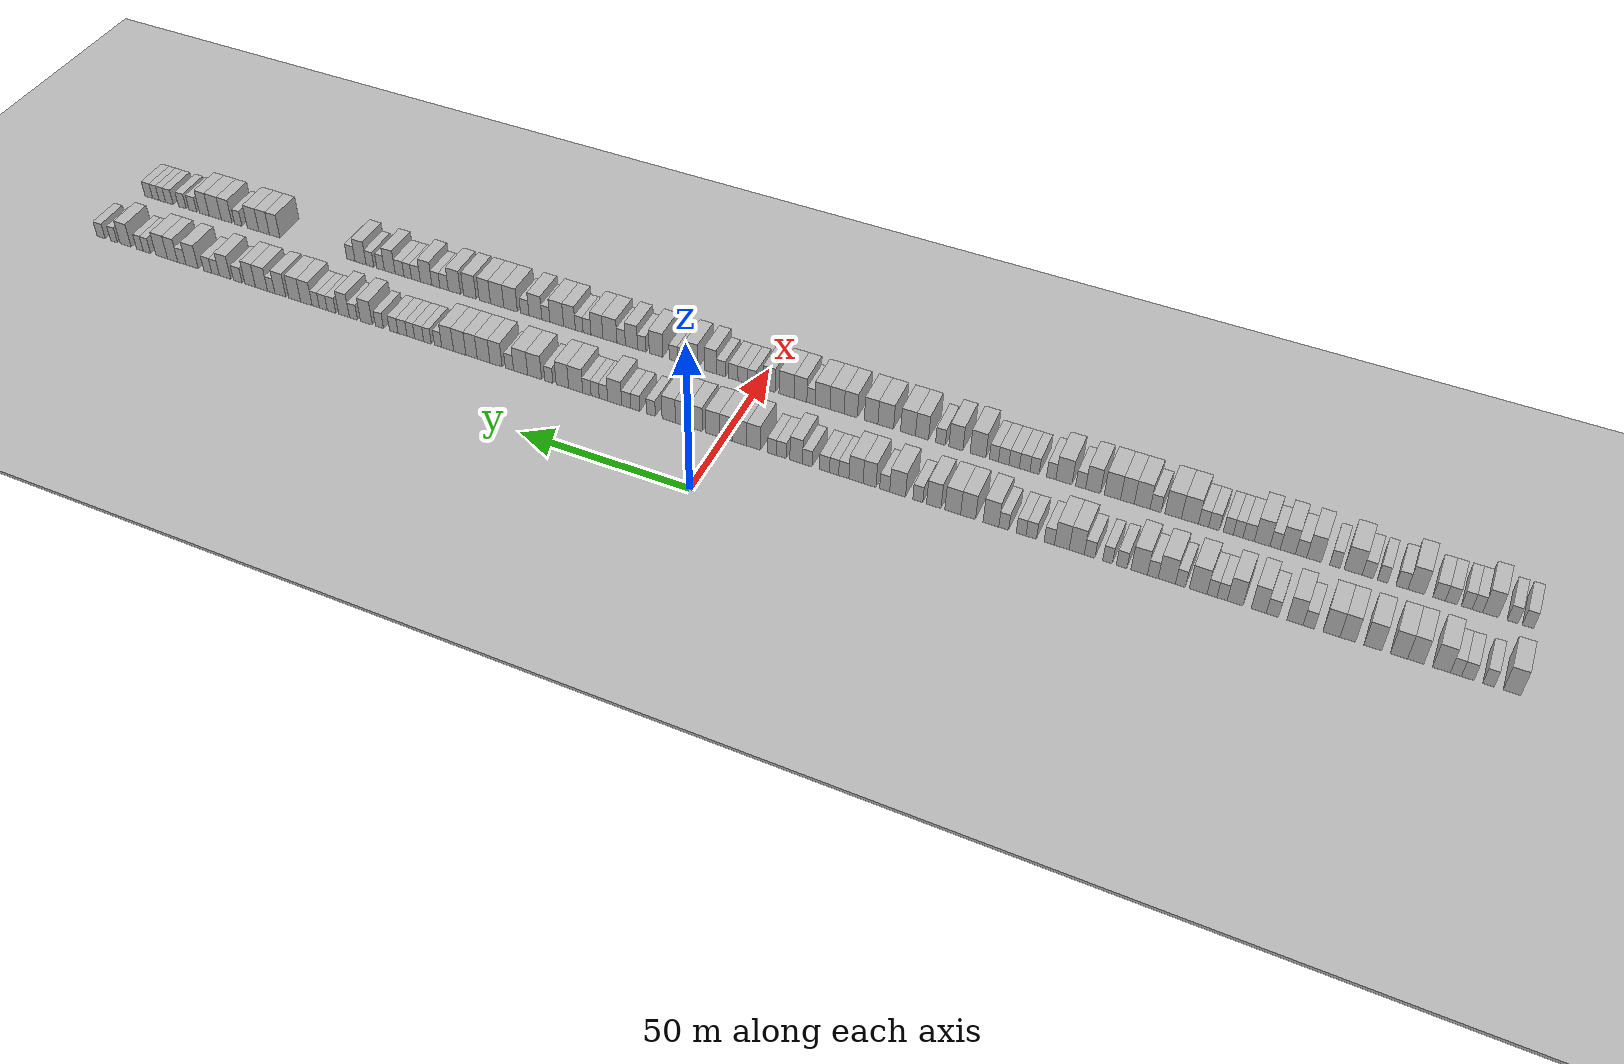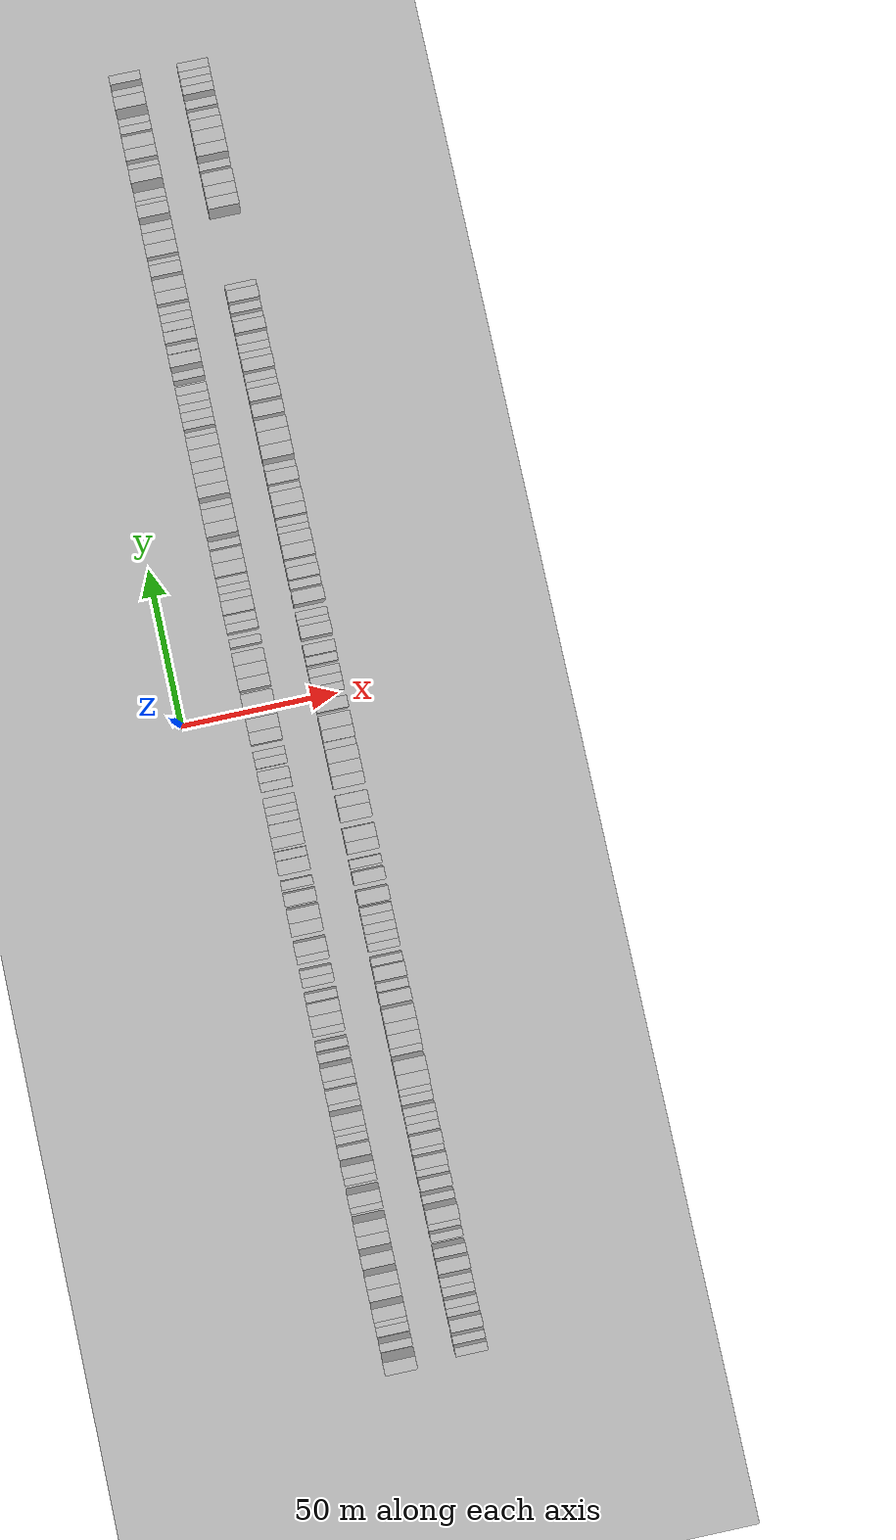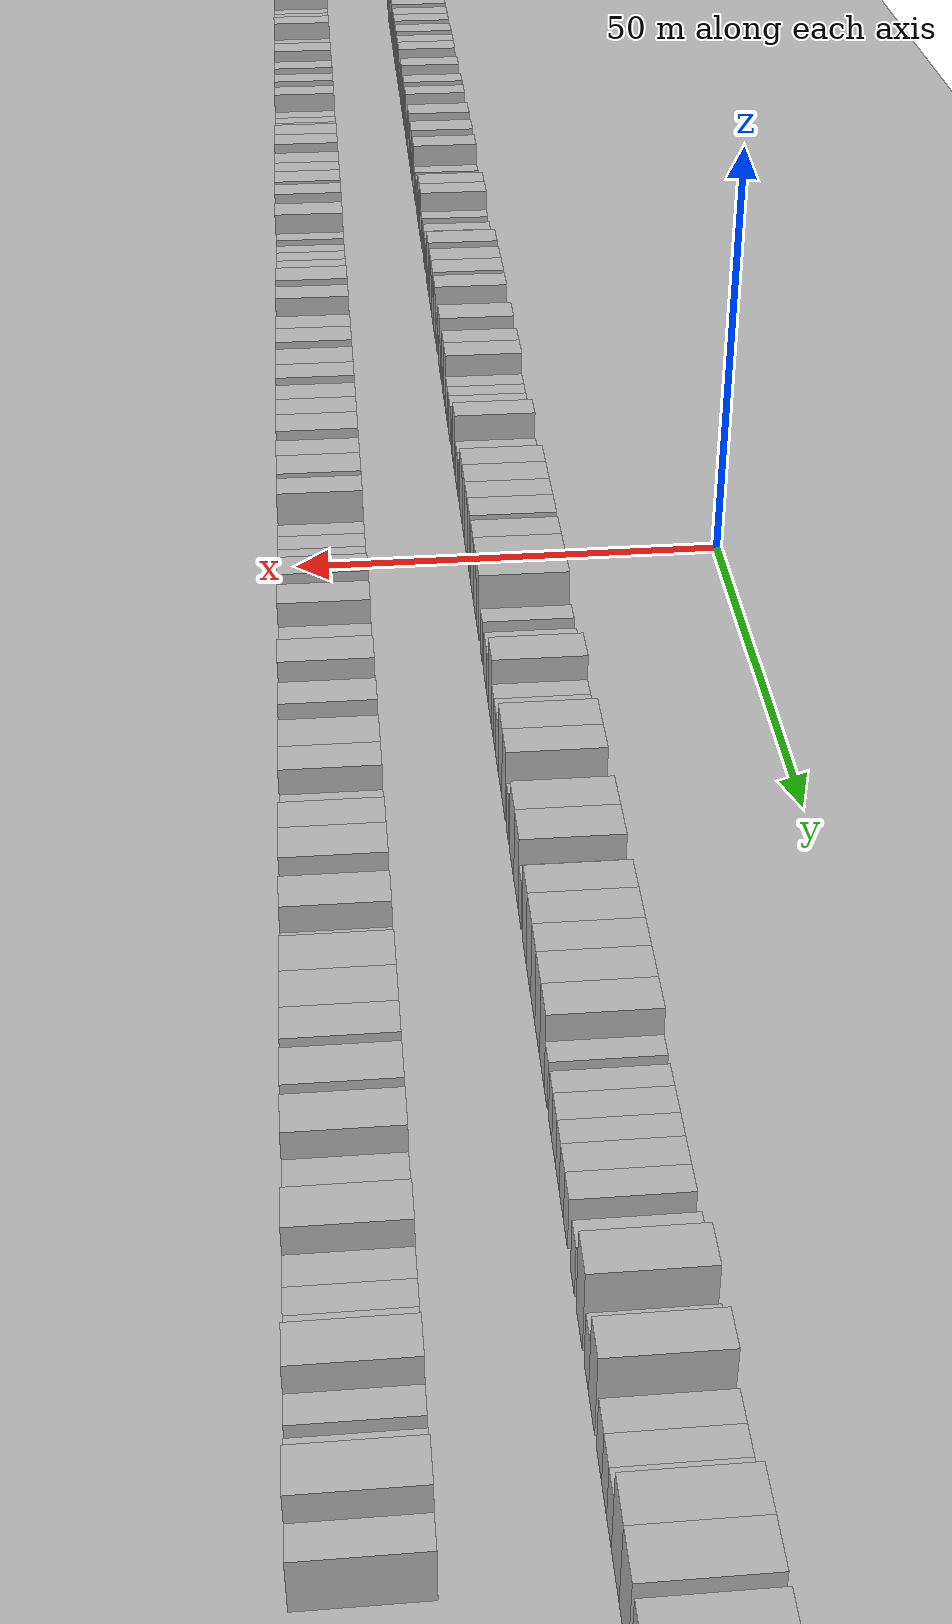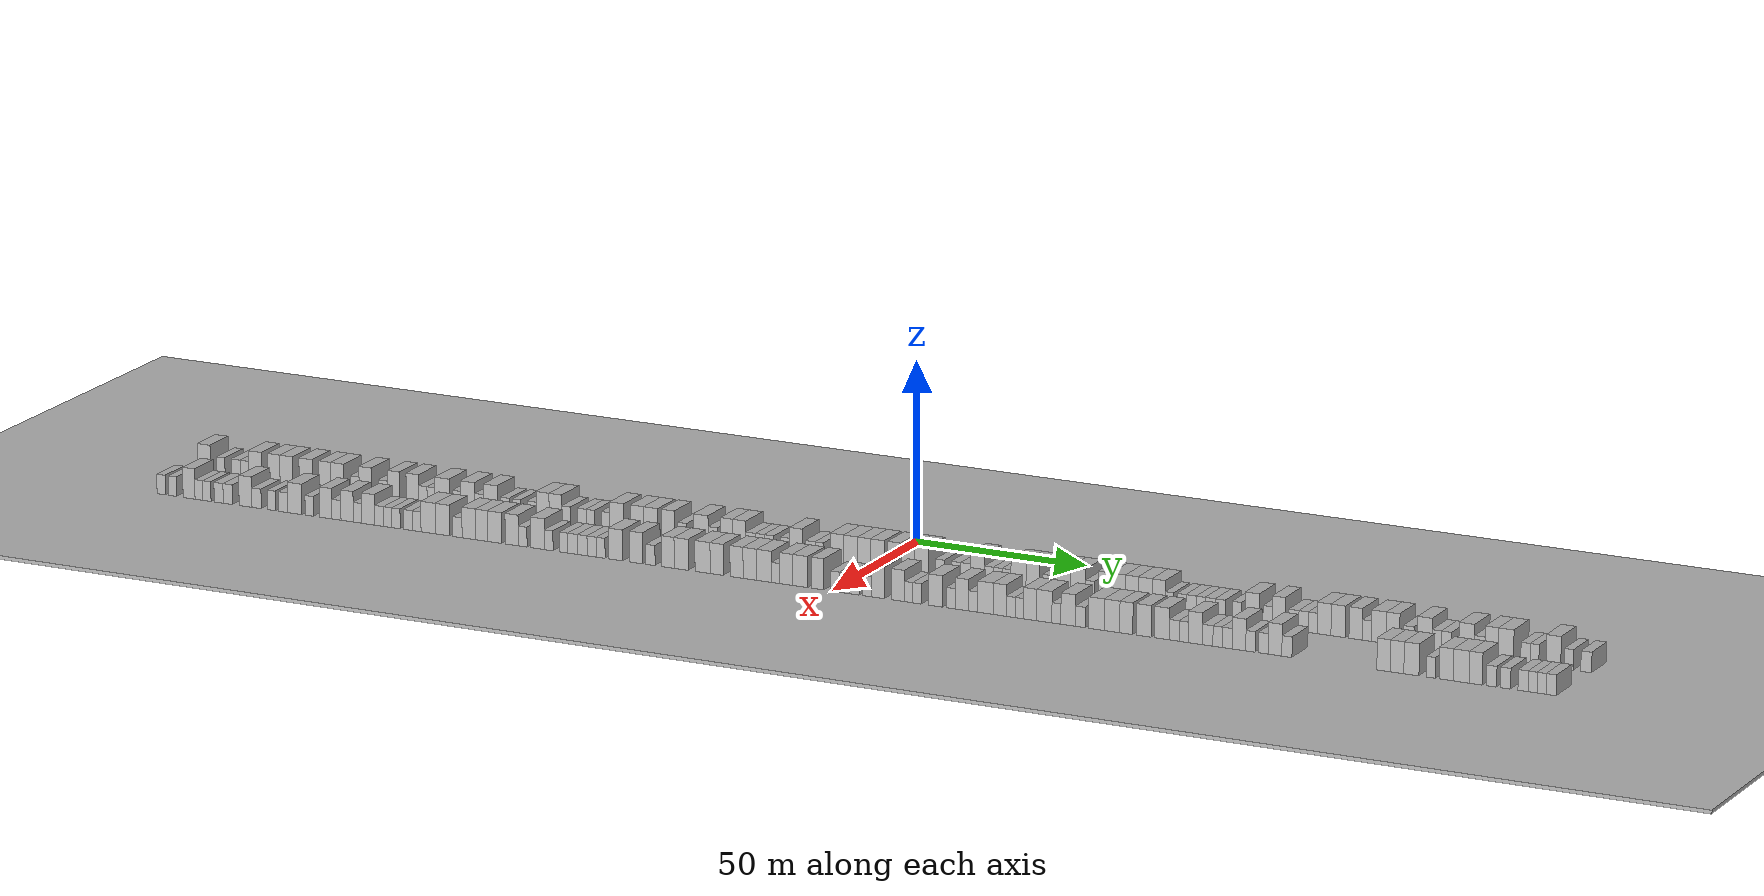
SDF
<?xml version="1.0" encoding="utf-8"?>

<sdf version="1.6">

   <world name="default">

      <gui fullscreen="0">

         <camera name="user_camera">

            <pose>-15 0 4.57585 0 0 0</pose>

            <view_controller>orbit</view_controller>

         </camera>

      </gui>

      <scene>

         <sky>

           <clouds>

             <speed>12</speed>

           </clouds>

         </sky>

         <ambient>0.4 0.4 0.4 1</ambient>

         <background>0.7 0.7 0.7 1</background>

         <shadows>1</shadows>

      </scene>

      <gravity>0 0 -9.8066</gravity>

      <magnetic_field>6e-06 2.3e-05 -4.2e-05</magnetic_field>

      <physics default="0" name="default_physics" type="ode">

         <ode>

            <solver>

               <type>quick</type>

               <iters>10</iters>

               <sor>1.0</sor>

               <use_dynamic_moi_rescaling>0</use_dynamic_moi_rescaling>

            </solver>

            <constraints>

               <cfm>0</cfm>

               <erp>0.2</erp>

               <contact_max_correcting_vel>100</contact_max_correcting_vel>

               <contact_surface_layer>0.001</contact_surface_layer>

            </constraints>

         </ode>

         <max_step_size>0.004</max_step_size>

         <real_time_factor>1</real_time_factor>

         <real_time_update_rate>250</real_time_update_rate>

      </physics>

      <light name="sun" type="directional">

         <cast_shadows>1</cast_shadows>

         <pose>0 0 10 0 0 0</pose>

         <diffuse>0.8 0.8 0.8 1</diffuse>

         <specular>0.2 0.2 0.2 1</specular>

         <attenuation>

            <range>1000</range>

            <constant>0.9</constant>

            <linear>0.01</linear>

            <quadratic>0.001</quadratic>

         </attenuation>

         <direction>-0.5 0.1 -0.9</direction>

      </light>

      <include>

         <name>ground_plane_1</name>

         <uri>model://HANNAS_ground_plane</uri>

         <pose>0 0 0  0 0 0</pose>

      </include>

      <include>

         <name>ground_plane_2</name>

         <uri>model://HANNAS_ground_plane</uri>

         <pose>100 0 0  0 0 0</pose>

      </include>

      <model name="building_1">

         <static>1</static>

         <pose frame="">25.0000 -202.0195 0 0.000000 0.000000 0.000000</pose>

         <link name="link">

            <pose frame="">0 0 4.50 0 0 0</pose>

            <collision name="collision">

               <geometry>

                  <box>

                     <size>10.0000 3.9611 9.0000</size>

                  </box>

               </geometry>

               <max_contacts>10</max_contacts>

               <surface>

                  <contact>

                     <ode/>

                  </contact>

                  <bounce/>

                  <friction>

                     <torsional>

                        <ode/>

                     </torsional>

                     <ode/>

                  </friction>

               </surface>

            </collision>

            <visual name="visual">

               <cast_shadows>0</cast_shadows>

               <geometry>

                  <box>

                     <size>10.0000 3.9611 9.0000</size>

                  </box>

               </geometry>

               <material>

                  <script>

                     <uri>model://HANNAS_wall/materials/scripts</uri>

                     <uri>model://HANNAS_wall/materials/textures</uri>

                     <name>vrc/HANNAS_wall</name>

                  </script>

               </material>

            </visual>

            <self_collide>0</self_collide>

            <enable_wind>0</enable_wind>

            <kinematic>0</kinematic>

         </link>

      </model>

      <model name="building_2">

         <static>1</static>

         <pose frame="">25.0000 -196.7426 0 0.000000 0.000000 0.000000</pose>

         <link name="link">

            <pose frame="">0 0 3.00 0 0 0</pose>

            <collision name="collision">

               <geometry>

                  <box>

                     <size>10.0000 2.5925 6.0000</size>

                  </box>

               </geometry>

               <max_contacts>10</max_contacts>

               <surface>

                  <contact>

                     <ode/>

                  </contact>

                  <bounce/>

                  <friction>

                     <torsional>

                        <ode/>

                     </torsional>

                     <ode/>

                  </friction>

               </surface>

            </collision>

            <visual name="visual">

               <cast_shadows>0</cast_shadows>

               <geometry>

                  <box>

                     <size>10.0000 2.5925 6.0000</size>

                  </box>

               </geometry>

               <material>

                  <script>

                     <uri>model://HANNAS_wall/materials/scripts</uri>

                     <uri>model://HANNAS_wall/materials/textures</uri>

                     <name>vrc/HANNAS_wall</name>

                  </script>

               </material>

            </visual>

            <self_collide>0</self_collide>

            <enable_wind>0</enable_wind>

            <kinematic>0</kinematic>

         </link>

      </model>

      <model name="building_3">

         <static>1</static>

         <pose frame="">25.0000 -192.0172 0 0.000000 0.000000 0.000000</pose>

         <link name="link">

            <pose frame="">0 0 3.00 0 0 0</pose>

            <collision name="collision">

               <geometry>

                  <box>

                     <size>10.0000 2.8583 6.0000</size>

                  </box>

               </geometry>

               <max_contacts>10</max_contacts>

               <surface>

                  <contact>

                     <ode/>

                  </contact>

                  <bounce/>

                  <friction>

                     <torsional>

                        <ode/>

                     </torsional>

                     <ode/>

                  </friction>

               </surface>

            </collision>

            <visual name="visual">

               <cast_shadows>0</cast_shadows>

               <geometry>

                  <box>

                     <size>10.0000 2.8583 6.0000</size>

                  </box>

               </geometry>

               <material>

                  <script>

                     <uri>model://HANNAS_wall/materials/scripts</uri>

                     <uri>model://HANNAS_wall/materials/textures</uri>

                     <name>vrc/HANNAS_wall</name>

                  </script>

               </material>

            </visual>

            <self_collide>0</self_collide>

            <enable_wind>0</enable_wind>

            <kinematic>0</kinematic>

         </link>

      </model>

      <model name="building_4">

         <static>1</static>

         <pose frame="">25.0000 -189.3305 0 0.000000 0.000000 0.000000</pose>

         <link name="link">

            <pose frame="">0 0 3.00 0 0 0</pose>

            <collision name="collision">

               <geometry>

                  <box>

                     <size>10.0000 2.5152 6.0000</size>

                  </box>

               </geometry>

               <max_contacts>10</max_contacts>

               <surface>

                  <contact>

                     <ode/>

                  </contact>

                  <bounce/>

                  <friction>

                     <torsional>

                        <ode/>

                     </torsional>

                     <ode/>

                  </friction>

               </surface>

            </collision>

            <visual name="visual">

               <cast_shadows>0</cast_shadows>

               <geometry>

                  <box>

                     <size>10.0000 2.5152 6.0000</size>

                  </box>

               </geometry>

               <material>

                  <script>

                     <uri>model://HANNAS_wall/materials/scripts</uri>

                     <uri>model://HANNAS_wall/materials/textures</uri>

                     <name>vrc/HANNAS_wall</name>

                  </script>

               </material>

            </visual>

            <self_collide>0</self_collide>

            <enable_wind>0</enable_wind>

            <kinematic>0</kinematic>

         </link>

      </model>

      <model name="building_5">

         <static>1</static>

         <pose frame="">25.0000 -186.0190 0 0.000000 0.000000 0.000000</pose>

         <link name="link">

            <pose frame="">0 0 4.50 0 0 0</pose>

            <collision name="collision">

               <geometry>

                  <box>

                     <size>10.0000 4.1077 9.0000</size>

                  </box>

               </geometry>

               <max_contacts>10</max_contacts>

               <surface>

                  <contact>

                     <ode/>

                  </contact>

                  <bounce/>

                  <friction>

                     <torsional>

                        <ode/>

                     </torsional>

                     <ode/>

                  </friction>

               </surface>

            </collision>

            <visual name="visual">

               <cast_shadows>0</cast_shadows>

               <geometry>

                  <box>

                     <size>10.0000 4.1077 9.0000</size>

                  </box>

               </geometry>

               <material>

                  <script>

                     <uri>model://HANNAS_wall/materials/scripts</uri>

                     <uri>model://HANNAS_wall/materials/textures</uri>

                     <name>vrc/HANNAS_wall</name>

                  </script>

               </material>

            </visual>

            <self_collide>0</self_collide>

            <enable_wind>0</enable_wind>

            <kinematic>0</kinematic>

         </link>

      </model>

      <model name="building_6">

         <static>1</static>

         <pose frame="">25.0000 -180.0882 0 0.000000 0.000000 0.000000</pose>

         <link name="link">

            <pose frame="">0 0 4.50 0 0 0</pose>

            <collision name="collision">

               <geometry>

                  <box>

                     <size>10.0000 3.7539 9.0000</size>

                  </box>

               </geometry>

               <max_contacts>10</max_contacts>

               <surface>

                  <contact>

                     <ode/>

                  </contact>

                  <bounce/>

                  <friction>

                     <torsional>

                        <ode/>

                     </torsional>

                     <ode/>

                  </friction>

               </surface>

            </collision>

            <visual name="visual">

               <cast_shadows>0</cast_shadows>

               <geometry>

                  <box>

                     <size>10.0000 3.7539 9.0000</size>

                  </box>

               </geometry>

               <material>

                  <script>

                     <uri>model://HANNAS_wall/materials/scripts</uri>

                     <uri>model://HANNAS_wall/materials/textures</uri>

                     <name>vrc/HANNAS_wall</name>

                  </script>

               </material>

            </visual>

            <self_collide>0</self_collide>

            <enable_wind>0</enable_wind>

            <kinematic>0</kinematic>

         </link>

      </model>

      <model name="building_7">

         <static>1</static>

         <pose frame="">25.0000 -176.2114 0 0.000000 0.000000 0.000000</pose>

         <link name="link">

            <pose frame="">0 0 4.50 0 0 0</pose>

            <collision name="collision">

               <geometry>

                  <box>

                     <size>10.0000 3.9996 9.0000</size>

                  </box>

               </geometry>

               <max_contacts>10</max_contacts>

               <surface>

                  <contact>

                     <ode/>

                  </contact>

                  <bounce/>

                  <friction>

                     <torsional>

                        <ode/>

                     </torsional>

                     <ode/>

                  </friction>

               </surface>

            </collision>

            <visual name="visual">

               <cast_shadows>0</cast_shadows>

               <geometry>

                  <box>

                     <size>10.0000 3.9996 9.0000</size>

                  </box>

               </geometry>

               <material>

                  <script>

                     <uri>model://HANNAS_wall/materials/scripts</uri>

                     <uri>model://HANNAS_wall/materials/textures</uri>

                     <name>vrc/HANNAS_wall</name>

                  </script>

               </material>

            </visual>

            <self_collide>0</self_collide>

            <enable_wind>0</enable_wind>

            <kinematic>0</kinematic>

         </link>

      </model>

      <model name="building_8">

         <static>1</static>

         <pose frame="">25.0000 -170.1187 0 0.000000 0.000000 0.000000</pose>

         <link name="link">

            <pose frame="">0 0 4.50 0 0 0</pose>

            <collision name="collision">

               <geometry>

                  <box>

                     <size>10.0000 4.1858 9.0000</size>

                  </box>

               </geometry>

               <max_contacts>10</max_contacts>

               <surface>

                  <contact>

                     <ode/>

                  </contact>

                  <bounce/>

                  <friction>

                     <torsional>

                        <ode/>

                     </torsional>

                     <ode/>

                  </friction>

               </surface>

            </collision>

            <visual name="visual">

               <cast_shadows>0</cast_shadows>

               <geometry>

                  <box>

                     <size>10.0000 4.1858 9.0000</size>

                  </box>

               </geometry>

               <material>

                  <script>

                     <uri>model://HANNAS_wall/materials/scripts</uri>

                     <uri>model://HANNAS_wall/materials/textures</uri>

                     <name>vrc/HANNAS_wall</name>

                  </script>

               </material>

            </visual>

            <self_collide>0</self_collide>

            <enable_wind>0</enable_wind>

            <kinematic>0</kinematic>

         </link>

      </model>

      <model name="building_9">

         <static>1</static>

         <pose frame="">25.0000 -164.1834 0 0.000000 0.000000 0.000000</pose>

         <link name="link">

            <pose frame="">0 0 4.50 0 0 0</pose>

            <collision name="collision">

               <geometry>

                  <box>

                     <size>10.0000 3.6849 9.0000</size>

                  </box>

               </geometry>

               <max_contacts>10</max_contacts>

               <surface>

                  <contact>

                     <ode/>

                  </contact>

                  <bounce/>

                  <friction>

                     <torsional>

                        <ode/>

                     </torsional>

                     <ode/>

                  </friction>

               </surface>

            </collision>

            <visual name="visual">

               <cast_shadows>0</cast_shadows>

               <geometry>

                  <box>

                     <size>10.0000 3.6849 9.0000</size>

                  </box>

               </geometry>

               <material>

                  <script>

                     <uri>model://HANNAS_wall/materials/scripts</uri>

                     <uri>model://HANNAS_wall/materials/textures</uri>

                     <name>vrc/HANNAS_wall</name>

                  </script>

               </material>

            </visual>

            <self_collide>0</self_collide>

            <enable_wind>0</enable_wind>

            <kinematic>0</kinematic>

         </link>

      </model>

      <model name="building_10">

         <static>1</static>

         <pose frame="">25.0000 -160.3141 0 0.000000 0.000000 0.000000</pose>

         <link name="link">

            <pose frame="">0 0 4.50 0 0 0</pose>

            <collision name="collision">

               <geometry>

                  <box>

                     <size>10.0000 4.0536 9.0000</size>

                  </box>

               </geometry>

               <max_contacts>10</max_contacts>

               <surface>

                  <contact>

                     <ode/>

                  </contact>

                  <bounce/>

                  <friction>

                     <torsional>

                        <ode/>

                     </torsional>

                     <ode/>

                  </friction>

               </surface>

            </collision>

            <visual name="visual">

               <cast_shadows>0</cast_shadows>

               <geometry>

                  <box>

                     <size>10.0000 4.0536 9.0000</size>

                  </box>

               </geometry>

               <material>

                  <script>

                     <uri>model://HANNAS_wall/materials/scripts</uri>

                     <uri>model://HANNAS_wall/materials/textures</uri>

                     <name>vrc/HANNAS_wall</name>

                  </script>

               </material>

            </visual>

            <self_collide>0</self_collide>

            <enable_wind>0</enable_wind>

            <kinematic>0</kinematic>

         </link>

      </model>

      <model name="building_11">

         <static>1</static>

         <pose frame="">25.0000 -154.9303 0 0.000000 0.000000 0.000000</pose>

         <link name="link">

            <pose frame="">0 0 3.00 0 0 0</pose>

            <collision name="collision">

               <geometry>

                  <box>

                     <size>10.0000 2.7140 6.0000</size>

                  </box>

               </geometry>

               <max_contacts>10</max_contacts>

               <surface>

                  <contact>

                     <ode/>

                  </contact>

                  <bounce/>

                  <friction>

                     <torsional>

                        <ode/>

                     </torsional>

                     <ode/>

                  </friction>

               </surface>

            </collision>

            <visual name="visual">

               <cast_shadows>0</cast_shadows>

               <geometry>

                  <box>

                     <size>10.0000 2.7140 6.0000</size>

                  </box>

               </geometry>

               <material>

                  <script>

                     <uri>model://HANNAS_wall/materials/scripts</uri>

                     <uri>model://HANNAS_wall/materials/textures</uri>

                     <name>vrc/HANNAS_wall</name>

                  </script>

               </material>

            </visual>

            <self_collide>0</self_collide>

            <enable_wind>0</enable_wind>

            <kinematic>0</kinematic>

         </link>

      </model>

      <model name="building_12">

         <static>1</static>

         <pose frame="">25.0000 -151.6047 0 0.000000 0.000000 0.000000</pose>

         <link name="link">

            <pose frame="">0 0 4.50 0 0 0</pose>

            <collision name="collision">

               <geometry>

                  <box>

                     <size>10.0000 3.9372 9.0000</size>

                  </box>

               </geometry>

               <max_contacts>10</max_contacts>

               <surface>

                  <contact>

                     <ode/>

                  </contact>

                  <bounce/>

                  <friction>

                     <torsional>

                        <ode/>

                     </torsional>

                     <ode/>

                  </friction>

               </surface>

            </collision>

            <visual name="visual">

               <cast_shadows>0</cast_shadows>

               <geometry>

                  <box>

                     <size>10.0000 3.9372 9.0000</size>

                  </box>

               </geometry>

               <material>

                  <script>

                     <uri>model://HANNAS_wall/materials/scripts</uri>

                     <uri>model://HANNAS_wall/materials/textures</uri>

                     <name>vrc/HANNAS_wall</name>

                  </script>

               </material>

            </visual>

            <self_collide>0</self_collide>

            <enable_wind>0</enable_wind>

            <kinematic>0</kinematic>

         </link>

      </model>

      <model name="building_13">

         <static>1</static>

         <pose frame="">25.0000 -146.1533 0 0.000000 0.000000 0.000000</pose>

         <link name="link">

            <pose frame="">0 0 3.00 0 0 0</pose>

            <collision name="collision">

               <geometry>

                  <box>

                     <size>10.0000 2.9655 6.0000</size>

                  </box>

               </geometry>

               <max_contacts>10</max_contacts>

               <surface>

                  <contact>

                     <ode/>

                  </contact>

                  <bounce/>

                  <friction>

                     <torsional>

                        <ode/>

                     </torsional>

                     <ode/>

                  </friction>

               </surface>

            </collision>

            <visual name="visual">

               <cast_shadows>0</cast_shadows>

               <geometry>

                  <box>

                     <size>10.0000 2.9655 6.0000</size>

                  </box>

               </geometry>

               <material>

                  <script>

                     <uri>model://HANNAS_wall/materials/scripts</uri>

                     <uri>model://HANNAS_wall/materials/textures</uri>

                     <name>vrc/HANNAS_wall</name>

                  </script>

               </material>

            </visual>

            <self_collide>0</self_collide>

            <enable_wind>0</enable_wind>

            <kinematic>0</kinematic>

         </link>

      </model>

      <model name="building_14">

         <static>1</static>

         <pose frame="">25.0000 -142.8404 0 0.000000 0.000000 0.000000</pose>

         <link name="link">

            <pose frame="">0 0 4.50 0 0 0</pose>

            <collision name="collision">

               <geometry>

                  <box>

                     <size>10.0000 3.6602 9.0000</size>

                  </box>

               </geometry>

               <max_contacts>10</max_contacts>

               <surface>

                  <contact>

                     <ode/>

                  </contact>

                  <bounce/>

                  <friction>

                     <torsional>

                        <ode/>

                     </torsional>

                     <ode/>

                  </friction>

               </surface>

            </collision>

            <visual name="visual">

               <cast_shadows>0</cast_shadows>

               <geometry>

                  <box>

                     <size>10.0000 3.6602 9.0000</size>

                  </box>

               </geometry>

               <material>

                  <script>

                     <uri>model://HANNAS_wall/materials/scripts</uri>

                     <uri>model://HANNAS_wall/materials/textures</uri>

                     <name>vrc/HANNAS_wall</name>

                  </script>

               </material>

            </visual>

            <self_collide>0</self_collide>

            <enable_wind>0</enable_wind>

            <kinematic>0</kinematic>

         </link>

      </model>

      <model name="building_15">

         <static>1</static>

         <pose frame="">25.0000 -137.0735 0 0.000000 0.000000 0.000000</pose>

         <link name="link">

            <pose frame="">0 0 4.50 0 0 0</pose>

            <collision name="collision">

               <geometry>

                  <box>

                     <size>10.0000 3.8736 9.0000</size>

                  </box>

               </geometry>

               <max_contacts>10</max_contacts>

               <surface>

                  <contact>

                     <ode/>

                  </contact>

                  <bounce/>

                  <friction>

                     <torsional>

                        <ode/>

                     </torsional>

                     <ode/>

                  </friction>

               </surface>

            </collision>

            <visual name="visual">

               <cast_shadows>0</cast_shadows>

               <geometry>

                  <box>

                     <size>10.0000 3.8736 9.0000</size>

                  </box>

               </geometry>

               <material>

                  <script>

                     <uri>model://HANNAS_wall/materials/scripts</uri>

                     <uri>model://HANNAS_wall/materials/textures</uri>

                     <name>vrc/HANNAS_wall</name>

                  </script>

               </material>

            </visual>

            <self_collide>0</self_collide>

            <enable_wind>0</enable_wind>

            <kinematic>0</kinematic>

         </link>

      </model>

      <model name="building_16">

         <static>1</static>

         <pose frame="">25.0000 -133.8605 0 0.000000 0.000000 0.000000</pose>

         <link name="link">

            <pose frame="">0 0 3.00 0 0 0</pose>

            <collision name="collision">

               <geometry>

                  <box>

                     <size>10.0000 2.5524 6.0000</size>

                  </box>

               </geometry>

               <max_contacts>10</max_contacts>

               <surface>

                  <contact>

                     <ode/>

                  </contact>

                  <bounce/>

                  <friction>

                     <torsional>

                        <ode/>

                     </torsional>

                     <ode/>

                  </friction>

               </surface>

            </collision>

            <visual name="visual">

               <cast_shadows>0</cast_shadows>

               <geometry>

                  <box>

                     <size>10.0000 2.5524 6.0000</size>

                  </box>

               </geometry>

               <material>

                  <script>

                     <uri>model://HANNAS_wall/materials/scripts</uri>

                     <uri>model://HANNAS_wall/materials/textures</uri>

                     <name>vrc/HANNAS_wall</name>

                  </script>

               </material>

            </visual>

            <self_collide>0</self_collide>

            <enable_wind>0</enable_wind>

            <kinematic>0</kinematic>

         </link>

      </model>

      <model name="building_17">

         <static>1</static>

         <pose frame="">25.0000 -131.3739 0 0.000000 0.000000 0.000000</pose>

         <link name="link">

            <pose frame="">0 0 3.00 0 0 0</pose>

            <collision name="collision">

               <geometry>

                  <box>

                     <size>10.0000 2.4209 6.0000</size>

                  </box>

               </geometry>

               <max_contacts>10</max_contacts>

               <surface>

                  <contact>

                     <ode/>

                  </contact>

                  <bounce/>

                  <friction>

                     <torsional>

                        <ode/>

                     </torsional>

                     <ode/>

                  </friction>

               </surface>

            </collision>

            <visual name="visual">

               <cast_shadows>0</cast_shadows>

               <geometry>

                  <box>

                     <size>10.0000 2.4209 6.0000</size>

                  </box>

               </geometry>

               <material>

                  <script>

                     <uri>model://HANNAS_wall/materials/scripts</uri>

                     <uri>model://HANNAS_wall/materials/textures</uri>

                     <name>vrc/HANNAS_wall</name>

                  </script>

               </material>

            </visual>

            <self_collide>0</self_collide>

            <enable_wind>0</enable_wind>

            <kinematic>0</kinematic>

         </link>

      </model>

      <model name="building_18">

         <static>1</static>

         <pose frame="">25.0000 -127.9563 0 0.000000 0.000000 0.000000</pose>

         <link name="link">

            <pose frame="">0 0 4.50 0 0 0</pose>

            <collision name="collision">

               <geometry>

                  <box>

                     <size>10.0000 4.4143 9.0000</size>

                  </box>

               </geometry>

               <max_contacts>10</max_contacts>

               <surface>

                  <contact>

                     <ode/>

                  </contact>

                  <bounce/>

                  <friction>

                     <torsional>

                        <ode/>

                     </torsional>

                     <ode/>

                  </friction>

               </surface>

            </collision>

            <visual name="visual">

               <cast_shadows>0</cast_shadows>

               <geometry>

                  <box>

                     <size>10.0000 4.4143 9.0000</size>

                  </box>

               </geometry>

               <material>

                  <script>

                     <uri>model://HANNAS_wall/materials/scripts</uri>

                     <uri>model://HANNAS_wall/materials/textures</uri>

                     <name>vrc/HANNAS_wall</name>

                  </script>

               </material>

            </visual>

            <self_collide>0</self_collide>

            <enable_wind>0</enable_wind>

            <kinematic>0</kinematic>

         </link>

      </model>

      <model name="building_19">

         <static>1</static>

         <pose frame="">25.0000 -123.5291 0 0.000000 0.000000 0.000000</pose>

         <link name="link">

            <pose frame="">0 0 3.00 0 0 0</pose>

            <collision name="collision">

               <geometry>

                  <box>

                     <size>10.0000 2.4401 6.0000</size>

                  </box>

               </geometry>

               <max_contacts>10</max_contacts>

               <surface>

                  <contact>

                     <ode/>

                  </contact>

                  <bounce/>

                  <friction>

                     <torsional>

                        <ode/>

                     </torsional>

                     <ode/>

                  </friction>

               </surface>

            </collision>

            <visual name="visual">

               <cast_shadows>0</cast_shadows>

               <geometry>

                  <box>

                     <size>10.0000 2.4401 6.0000</size>

                  </box>

               </geometry>

               <material>

                  <script>

                     <uri>model://HANNAS_wall/materials/scripts</uri>

                     <uri>model://HANNAS_wall/materials/textures</uri>

                     <name>vrc/HANNAS_wall</name>

                  </script>

               </material>

            </visual>

            <self_collide>0</self_collide>

            <enable_wind>0</enable_wind>

            <kinematic>0</kinematic>

         </link>

      </model>

      <model name="building_20">

         <static>1</static>

         <pose frame="">25.0000 -120.1236 0 0.000000 0.000000 0.000000</pose>

         <link name="link">

            <pose frame="">0 0 4.50 0 0 0</pose>

            <collision name="collision">

               <geometry>

                  <box>

                     <size>10.0000 4.3709 9.0000</size>

                  </box>

               </geometry>

               <max_contacts>10</max_contacts>

               <surface>

                  <contact>

                     <ode/>

                  </contact>

                  <bounce/>

                  <friction>

                     <torsional>

                        <ode/>

                     </torsional>

                     <ode/>

                  </friction>

               </surface>

            </collision>

            <visual name="visual">

               <cast_shadows>0</cast_shadows>

               <geometry>

                  <box>

                     <size>10.0000 4.3709 9.0000</size>

                  </box>

               </geometry>

               <material>

                  <script>

                     <uri>model://HANNAS_wall/materials/scripts</uri>

                     <uri>model://HANNAS_wall/materials/textures</uri>

                     <name>vrc/HANNAS_wall</name>

                  </script>

               </material>

            </visual>

            <self_collide>0</self_collide>

            <enable_wind>0</enable_wind>

            <kinematic>0</kinematic>

         </link>

      </model>

      <model name="building_21">

         <static>1</static>

         <pose frame="">25.0000 -116.5990 0 0.000000 0.000000 0.000000</pose>

         <link name="link">

            <pose frame="">0 0 3.00 0 0 0</pose>

            <collision name="collision">

               <geometry>

                  <box>

                     <size>10.0000 2.6783 6.0000</size>

                  </box>

               </geometry>

               <max_contacts>10</max_contacts>

               <surface>

                  <contact>

                     <ode/>

                  </contact>

                  <bounce/>

                  <friction>

                     <torsional>

                        <ode/>

                     </torsional>

                     <ode/>

                  </friction>

               </surface>

            </collision>

            <visual name="visual">

               <cast_shadows>0</cast_shadows>

               <geometry>

                  <box>

                     <size>10.0000 2.6783 6.0000</size>

                  </box>

               </geometry>

               <material>

                  <script>

                     <uri>model://HANNAS_wall/materials/scripts</uri>

                     <uri>model://HANNAS_wall/materials/textures</uri>

                     <name>vrc/HANNAS_wall</name>

                  </script>

               </material>

            </visual>

            <self_collide>0</self_collide>

            <enable_wind>0</enable_wind>

            <kinematic>0</kinematic>

         </link>

      </model>

      <model name="building_22">

         <static>1</static>

         <pose frame="">25.0000 -113.1571 0 0.000000 0.000000 0.000000</pose>

         <link name="link">

            <pose frame="">0 0 4.50 0 0 0</pose>

            <collision name="collision">

               <geometry>

                  <box>

                     <size>10.0000 4.2056 9.0000</size>

                  </box>

               </geometry>

               <max_contacts>10</max_contacts>

               <surface>

                  <contact>

                     <ode/>

                  </contact>

                  <bounce/>

                  <friction>

                     <torsional>

                        <ode/>

                     </torsional>

                     <ode/>

                  </friction>

               </surface>

            </collision>

            <visual name="visual">

               <cast_shadows>0</cast_shadows>

               <geometry>

                  <box>

                     <size>10.0000 4.2056 9.0000</size>

                  </box>

               </geometry>

               <material>

                  <script>

                     <uri>model://HANNAS_wall/materials/scripts</uri>

                     <uri>model://HANNAS_wall/materials/textures</uri>

                     <name>vrc/HANNAS_wall</name>

                  </script>

               </material>

            </visual>

            <self_collide>0</self_collide>

            <enable_wind>0</enable_wind>

            <kinematic>0</kinematic>

         </link>

      </model>

      <model name="building_23">

         <static>1</static>

         <pose frame="">25.0000 -108.7004 0 0.000000 0.000000 0.000000</pose>

         <link name="link">

            <pose frame="">0 0 3.00 0 0 0</pose>

            <collision name="collision">

               <geometry>

                  <box>

                     <size>10.0000 2.7079 6.0000</size>

                  </box>

               </geometry>

               <max_contacts>10</max_contacts>

               <surface>

                  <contact>

                     <ode/>

                  </contact>

                  <bounce/>

                  <friction>

                     <torsional>

                        <ode/>

                     </torsional>

                     <ode/>

                  </friction>

               </surface>

            </collision>

            <visual name="visual">

               <cast_shadows>0</cast_shadows>

               <geometry>

                  <box>

                     <size>10.0000 2.7079 6.0000</size>

                  </box>

               </geometry>

               <material>

                  <script>

                     <uri>model://HANNAS_wall/materials/scripts</uri>

                     <uri>model://HANNAS_wall/materials/textures</uri>

                     <name>vrc/HANNAS_wall</name>

                  </script>

               </material>

            </visual>

            <self_collide>0</self_collide>

            <enable_wind>0</enable_wind>

            <kinematic>0</kinematic>

         </link>

      </model>

      <model name="building_24">

         <static>1</static>

         <pose frame="">25.0000 -105.1096 0 0.000000 0.000000 0.000000</pose>

         <link name="link">

            <pose frame="">0 0 3.00 0 0 0</pose>

            <collision name="collision">

               <geometry>

                  <box>

                     <size>10.0000 2.4737 6.0000</size>

                  </box>

               </geometry>

               <max_contacts>10</max_contacts>

               <surface>

                  <contact>

                     <ode/>

                  </contact>

                  <bounce/>

                  <friction>

                     <torsional>

                        <ode/>

                     </torsional>

                     <ode/>

                  </friction>

               </surface>

            </collision>

            <visual name="visual">

               <cast_shadows>0</cast_shadows>

               <geometry>

                  <box>

                     <size>10.0000 2.4737 6.0000</size>

                  </box>

               </geometry>

               <material>

                  <script>

                     <uri>model://HANNAS_wall/materials/scripts</uri>

                     <uri>model://HANNAS_wall/materials/textures</uri>

                     <name>vrc/HANNAS_wall</name>

                  </script>

               </material>

            </visual>

            <self_collide>0</self_collide>

            <enable_wind>0</enable_wind>

            <kinematic>0</kinematic>

         </link>

      </model>

      <model name="building_25">

         <static>1</static>

         <pose frame="">25.0000 -100.5047 0 0.000000 0.000000 0.000000</pose>

         <link name="link">

            <pose frame="">0 0 3.00 0 0 0</pose>

            <collision name="collision">

               <geometry>

                  <box>

                     <size>10.0000 2.7361 6.0000</size>

                  </box>

               </geometry>

               <max_contacts>10</max_contacts>

               <surface>

                  <contact>

                     <ode/>

                  </contact>

                  <bounce/>

                  <friction>

                     <torsional>

                        <ode/>

                     </torsional>

                     <ode/>

                  </friction>

               </surface>

            </collision>

            <visual name="visual">

               <cast_shadows>0</cast_shadows>

               <geometry>

                  <box>

                     <size>10.0000 2.7361 6.0000</size>

                  </box>

               </geometry>

               <material>

                  <script>

                     <uri>model://HANNAS_wall/materials/scripts</uri>

                     <uri>model://HANNAS_wall/materials/textures</uri>

                     <name>vrc/HANNAS_wall</name>

                  </script>

               </material>

            </visual>

            <self_collide>0</self_collide>

            <enable_wind>0</enable_wind>

            <kinematic>0</kinematic>

         </link>

      </model>

      <model name="building_26">

         <static>1</static>

         <pose frame="">25.0000 -97.1842 0 0.000000 0.000000 0.000000</pose>

         <link name="link">

            <pose frame="">0 0 4.50 0 0 0</pose>

            <collision name="collision">

               <geometry>

                  <box>

                     <size>10.0000 3.9048 9.0000</size>

                  </box>

               </geometry>

               <max_contacts>10</max_contacts>

               <surface>

                  <contact>

                     <ode/>

                  </contact>

                  <bounce/>

                  <friction>

                     <torsional>

                        <ode/>

                     </torsional>

                     <ode/>

                  </friction>

               </surface>

            </collision>

            <visual name="visual">

               <cast_shadows>0</cast_shadows>

               <geometry>

                  <box>

                     <size>10.0000 3.9048 9.0000</size>

                  </box>

               </geometry>

               <material>

                  <script>

                     <uri>model://HANNAS_wall/materials/scripts</uri>

                     <uri>model://HANNAS_wall/materials/textures</uri>

                     <name>vrc/HANNAS_wall</name>

                  </script>

               </material>

            </visual>

            <self_collide>0</self_collide>

            <enable_wind>0</enable_wind>

            <kinematic>0</kinematic>

         </link>

      </model>

      <model name="building_27">

         <static>1</static>

         <pose frame="">25.0000 -93.3163 0 0.000000 0.000000 0.000000</pose>

         <link name="link">

            <pose frame="">0 0 4.50 0 0 0</pose>

            <collision name="collision">

               <geometry>

                  <box>

                     <size>10.0000 3.8311 9.0000</size>

                  </box>

               </geometry>

               <max_contacts>10</max_contacts>

               <surface>

                  <contact>

                     <ode/>

                  </contact>

                  <bounce/>

                  <friction>

                     <torsional>

                        <ode/>

                     </torsional>

                     <ode/>

                  </friction>

               </surface>

            </collision>

            <visual name="visual">

               <cast_shadows>0</cast_shadows>

               <geometry>

                  <box>

                     <size>10.0000 3.8311 9.0000</size>

                  </box>

               </geometry>

               <material>

                  <script>

                     <uri>model://HANNAS_wall/materials/scripts</uri>

                     <uri>model://HANNAS_wall/materials/textures</uri>

                     <name>vrc/HANNAS_wall</name>

                  </script>

               </material>

            </visual>

            <self_collide>0</self_collide>

            <enable_wind>0</enable_wind>

            <kinematic>0</kinematic>

         </link>

      </model>

      <model name="building_28">

         <static>1</static>

         <pose frame="">25.0000 -90.0524 0 0.000000 0.000000 0.000000</pose>

         <link name="link">

            <pose frame="">0 0 3.00 0 0 0</pose>

            <collision name="collision">

               <geometry>

                  <box>

                     <size>10.0000 2.6967 6.0000</size>

                  </box>

               </geometry>

               <max_contacts>10</max_contacts>

               <surface>

                  <contact>

                     <ode/>

                  </contact>

                  <bounce/>

                  <friction>

                     <torsional>

                        <ode/>

                     </torsional>

                     <ode/>

                  </friction>

               </surface>

            </collision>

            <visual name="visual">

               <cast_shadows>0</cast_shadows>

               <geometry>

                  <box>

                     <size>10.0000 2.6967 6.0000</size>

                  </box>

               </geometry>

               <material>

                  <script>

                     <uri>model://HANNAS_wall/materials/scripts</uri>

                     <uri>model://HANNAS_wall/materials/textures</uri>

                     <name>vrc/HANNAS_wall</name>

                  </script>

               </material>

            </visual>

            <self_collide>0</self_collide>

            <enable_wind>0</enable_wind>

            <kinematic>0</kinematic>

         </link>

      </model>

      <model name="building_29">

         <static>1</static>

         <pose frame="">25.0000 -85.3369 0 0.000000 0.000000 0.000000</pose>

         <link name="link">

            <pose frame="">0 0 3.00 0 0 0</pose>

            <collision name="collision">

               <geometry>

                  <box>

                     <size>10.0000 2.7343 6.0000</size>

                  </box>

               </geometry>

               <max_contacts>10</max_contacts>

               <surface>

                  <contact>

                     <ode/>

                  </contact>

                  <bounce/>

                  <friction>

                     <torsional>

                        <ode/>

                     </torsional>

                     <ode/>

                  </friction>

               </surface>

            </collision>

            <visual name="visual">

               <cast_shadows>0</cast_shadows>

               <geometry>

                  <box>

                     <size>10.0000 2.7343 6.0000</size>

                  </box>

               </geometry>

               <material>

                  <script>

                     <uri>model://HANNAS_wall/materials/scripts</uri>

                     <uri>model://HANNAS_wall/materials/textures</uri>

                     <name>vrc/HANNAS_wall</name>

                  </script>

               </material>

            </visual>

            <self_collide>0</self_collide>

            <enable_wind>0</enable_wind>

            <kinematic>0</kinematic>

         </link>

      </model>

      <model name="building_30">

         <static>1</static>

         <pose frame="">25.0000 -82.6835 0 0.000000 0.000000 0.000000</pose>

         <link name="link">

            <pose frame="">0 0 3.00 0 0 0</pose>

            <collision name="collision">

               <geometry>

                  <box>

                     <size>10.0000 2.5724 6.0000</size>

                  </box>

               </geometry>

               <max_contacts>10</max_contacts>

               <surface>

                  <contact>

                     <ode/>

                  </contact>

                  <bounce/>

                  <friction>

                     <torsional>

                        <ode/>

                     </torsional>

                     <ode/>

                  </friction>

               </surface>

            </collision>

            <visual name="visual">

               <cast_shadows>0</cast_shadows>

               <geometry>

                  <box>

                     <size>10.0000 2.5724 6.0000</size>

                  </box>

               </geometry>

               <material>

                  <script>

                     <uri>model://HANNAS_wall/materials/scripts</uri>

                     <uri>model://HANNAS_wall/materials/textures</uri>

                     <name>vrc/HANNAS_wall</name>

                  </script>

               </material>

            </visual>

            <self_collide>0</self_collide>

            <enable_wind>0</enable_wind>

            <kinematic>0</kinematic>

         </link>

      </model>

      <model name="building_31">

         <static>1</static>

         <pose frame="">25.0000 -78.0929 0 0.000000 0.000000 0.000000</pose>

         <link name="link">

            <pose frame="">0 0 3.00 0 0 0</pose>

            <collision name="collision">

               <geometry>

                  <box>

                     <size>10.0000 2.6089 6.0000</size>

                  </box>

               </geometry>

               <max_contacts>10</max_contacts>

               <surface>

                  <contact>

                     <ode/>

                  </contact>

                  <bounce/>

                  <friction>

                     <torsional>

                        <ode/>

                     </torsional>

                     <ode/>

                  </friction>

               </surface>

            </collision>

            <visual name="visual">

               <cast_shadows>0</cast_shadows>

               <geometry>

                  <box>

                     <size>10.0000 2.6089 6.0000</size>

                  </box>

               </geometry>

               <material>

                  <script>

                     <uri>model://HANNAS_wall/materials/scripts</uri>

                     <uri>model://HANNAS_wall/materials/textures</uri>

                     <name>vrc/HANNAS_wall</name>

                  </script>

               </material>

            </visual>

            <self_collide>0</self_collide>

            <enable_wind>0</enable_wind>

            <kinematic>0</kinematic>

         </link>

      </model>

      <model name="building_32">

         <static>1</static>

         <pose frame="">25.0000 -74.6809 0 0.000000 0.000000 0.000000</pose>

         <link name="link">

            <pose frame="">0 0 4.50 0 0 0</pose>

            <collision name="collision">

               <geometry>

                  <box>

                     <size>10.0000 4.2151 9.0000</size>

                  </box>

               </geometry>

               <max_contacts>10</max_contacts>

               <surface>

                  <contact>

                     <ode/>

                  </contact>

                  <bounce/>

                  <friction>

                     <torsional>

                        <ode/>

                     </torsional>

                     <ode/>

                  </friction>

               </surface>

            </collision>

            <visual name="visual">

               <cast_shadows>0</cast_shadows>

               <geometry>

                  <box>

                     <size>10.0000 4.2151 9.0000</size>

                  </box>

               </geometry>

               <material>

                  <script>

                     <uri>model://HANNAS_wall/materials/scripts</uri>

                     <uri>model://HANNAS_wall/materials/textures</uri>

                     <name>vrc/HANNAS_wall</name>

                  </script>

               </material>

            </visual>

            <self_collide>0</self_collide>

            <enable_wind>0</enable_wind>

            <kinematic>0</kinematic>

         </link>

      </model>

      <model name="building_33">

         <static>1</static>

         <pose frame="">25.0000 -68.5717 0 0.000000 0.000000 0.000000</pose>

         <link name="link">

            <pose frame="">0 0 4.50 0 0 0</pose>

            <collision name="collision">

               <geometry>

                  <box>

                     <size>10.0000 4.0033 9.0000</size>

                  </box>

               </geometry>

               <max_contacts>10</max_contacts>

               <surface>

                  <contact>

                     <ode/>

                  </contact>

                  <bounce/>

                  <friction>

                     <torsional>

                        <ode/>

                     </torsional>

                     <ode/>

                  </friction>

               </surface>

            </collision>

            <visual name="visual">

               <cast_shadows>0</cast_shadows>

               <geometry>

                  <box>

                     <size>10.0000 4.0033 9.0000</size>

                  </box>

               </geometry>

               <material>

                  <script>

                     <uri>model://HANNAS_wall/materials/scripts</uri>

                     <uri>model://HANNAS_wall/materials/textures</uri>

                     <name>vrc/HANNAS_wall</name>

                  </script>

               </material>

            </visual>

            <self_collide>0</self_collide>

            <enable_wind>0</enable_wind>

            <kinematic>0</kinematic>

         </link>

      </model>

      <model name="building_34">

         <static>1</static>

         <pose frame="">25.0000 -64.4402 0 0.000000 0.000000 0.000000</pose>

         <link name="link">

            <pose frame="">0 0 4.50 0 0 0</pose>

            <collision name="collision">

               <geometry>

                  <box>

                     <size>10.0000 4.2598 9.0000</size>

                  </box>

               </geometry>

               <max_contacts>10</max_contacts>

               <surface>

                  <contact>

                     <ode/>

                  </contact>

                  <bounce/>

                  <friction>

                     <torsional>

                        <ode/>

                     </torsional>

                     <ode/>

                  </friction>

               </surface>

            </collision>

            <visual name="visual">

               <cast_shadows>0</cast_shadows>

               <geometry>

                  <box>

                     <size>10.0000 4.2598 9.0000</size>

                  </box>

               </geometry>

               <material>

                  <script>

                     <uri>model://HANNAS_wall/materials/scripts</uri>

                     <uri>model://HANNAS_wall/materials/textures</uri>

                     <name>vrc/HANNAS_wall</name>

                  </script>

               </material>

            </visual>

            <self_collide>0</self_collide>

            <enable_wind>0</enable_wind>

            <kinematic>0</kinematic>

         </link>

      </model>

      <model name="building_35">

         <static>1</static>

         <pose frame="">25.0000 -59.3258 0 0.000000 0.000000 0.000000</pose>

         <link name="link">

            <pose frame="">0 0 4.50 0 0 0</pose>

            <collision name="collision">

               <geometry>

                  <box>

                     <size>10.0000 3.9689 9.0000</size>

                  </box>

               </geometry>

               <max_contacts>10</max_contacts>

               <surface>

                  <contact>

                     <ode/>

                  </contact>

                  <bounce/>

                  <friction>

                     <torsional>

                        <ode/>

                     </torsional>

                     <ode/>

                  </friction>

               </surface>

            </collision>

            <visual name="visual">

               <cast_shadows>0</cast_shadows>

               <geometry>

                  <box>

                     <size>10.0000 3.9689 9.0000</size>

                  </box>

               </geometry>

               <material>

                  <script>

                     <uri>model://HANNAS_wall/materials/scripts</uri>

                     <uri>model://HANNAS_wall/materials/textures</uri>

                     <name>vrc/HANNAS_wall</name>

                  </script>

               </material>

            </visual>

            <self_collide>0</self_collide>

            <enable_wind>0</enable_wind>

            <kinematic>0</kinematic>

         </link>

      </model>

      <model name="building_36">

         <static>1</static>

         <pose frame="">25.0000 -54.9732 0 0.000000 0.000000 0.000000</pose>

         <link name="link">

            <pose frame="">0 0 3.00 0 0 0</pose>

            <collision name="collision">

               <geometry>

                  <box>

                     <size>10.0000 2.7362 6.0000</size>

                  </box>

               </geometry>

               <max_contacts>10</max_contacts>

               <surface>

                  <contact>

                     <ode/>

                  </contact>

                  <bounce/>

                  <friction>

                     <torsional>

                        <ode/>

                     </torsional>

                     <ode/>

                  </friction>

               </surface>

            </collision>

            <visual name="visual">

               <cast_shadows>0</cast_shadows>

               <geometry>

                  <box>

                     <size>10.0000 2.7362 6.0000</size>

                  </box>

               </geometry>

               <material>

                  <script>

                     <uri>model://HANNAS_wall/materials/scripts</uri>

                     <uri>model://HANNAS_wall/materials/textures</uri>

                     <name>vrc/HANNAS_wall</name>

                  </script>

               </material>

            </visual>

            <self_collide>0</self_collide>

            <enable_wind>0</enable_wind>

            <kinematic>0</kinematic>

         </link>

      </model>

      <model name="building_37">

         <static>1</static>

         <pose frame="">25.0000 -49.4260 0 0.000000 0.000000 0.000000</pose>

         <link name="link">

            <pose frame="">0 0 4.50 0 0 0</pose>

            <collision name="collision">

               <geometry>

                  <box>

                     <size>10.0000 4.3583 9.0000</size>

                  </box>

               </geometry>

               <max_contacts>10</max_contacts>

               <surface>

                  <contact>

                     <ode/>

                  </contact>

                  <bounce/>

                  <friction>

                     <torsional>

                        <ode/>

                     </torsional>

                     <ode/>

                  </friction>

               </surface>

            </collision>

            <visual name="visual">

               <cast_shadows>0</cast_shadows>

               <geometry>

                  <box>

                     <size>10.0000 4.3583 9.0000</size>

                  </box>

               </geometry>

               <material>

                  <script>

                     <uri>model://HANNAS_wall/materials/scripts</uri>

                     <uri>model://HANNAS_wall/materials/textures</uri>

                     <name>vrc/HANNAS_wall</name>

                  </script>

               </material>

            </visual>

            <self_collide>0</self_collide>

            <enable_wind>0</enable_wind>

            <kinematic>0</kinematic>

         </link>

      </model>

      <model name="building_38">

         <static>1</static>

         <pose frame="">25.0000 -45.8665 0 0.000000 0.000000 0.000000</pose>

         <link name="link">

            <pose frame="">0 0 3.00 0 0 0</pose>

            <collision name="collision">

               <geometry>

                  <box>

                     <size>10.0000 2.7607 6.0000</size>

                  </box>

               </geometry>

               <max_contacts>10</max_contacts>

               <surface>

                  <contact>

                     <ode/>

                  </contact>

                  <bounce/>

                  <friction>

                     <torsional>

                        <ode/>

                     </torsional>

                     <ode/>

                  </friction>

               </surface>

            </collision>

            <visual name="visual">

               <cast_shadows>0</cast_shadows>

               <geometry>

                  <box>

                     <size>10.0000 2.7607 6.0000</size>

                  </box>

               </geometry>

               <material>

                  <script>

                     <uri>model://HANNAS_wall/materials/scripts</uri>

                     <uri>model://HANNAS_wall/materials/textures</uri>

                     <name>vrc/HANNAS_wall</name>

                  </script>

               </material>

            </visual>

            <self_collide>0</self_collide>

            <enable_wind>0</enable_wind>

            <kinematic>0</kinematic>

         </link>

      </model>

      <model name="building_39">

         <static>1</static>

         <pose frame="">25.0000 -41.6844 0 0.000000 0.000000 0.000000</pose>

         <link name="link">

            <pose frame="">0 0 4.50 0 0 0</pose>

            <collision name="collision">

               <geometry>

                  <box>

                     <size>10.0000 3.6036 9.0000</size>

                  </box>

               </geometry>

               <max_contacts>10</max_contacts>

               <surface>

                  <contact>

                     <ode/>

                  </contact>

                  <bounce/>

                  <friction>

                     <torsional>

                        <ode/>

                     </torsional>

                     <ode/>

                  </friction>

               </surface>

            </collision>

            <visual name="visual">

               <cast_shadows>0</cast_shadows>

               <geometry>

                  <box>

                     <size>10.0000 3.6036 9.0000</size>

                  </box>

               </geometry>

               <material>

                  <script>

                     <uri>model://HANNAS_wall/materials/scripts</uri>

                     <uri>model://HANNAS_wall/materials/textures</uri>

                     <name>vrc/HANNAS_wall</name>

                  </script>

               </material>

            </visual>

            <self_collide>0</self_collide>

            <enable_wind>0</enable_wind>

            <kinematic>0</kinematic>

         </link>

      </model>

      <model name="building_40">

         <static>1</static>

         <pose frame="">25.0000 -37.9024 0 0.000000 0.000000 0.000000</pose>

         <link name="link">

            <pose frame="">0 0 4.50 0 0 0</pose>

            <collision name="collision">

               <geometry>

                  <box>

                     <size>10.0000 3.9604 9.0000</size>

                  </box>

               </geometry>

               <max_contacts>10</max_contacts>

               <surface>

                  <contact>

                     <ode/>

                  </contact>

                  <bounce/>

                  <friction>

                     <torsional>

                        <ode/>

                     </torsional>

                     <ode/>

                  </friction>

               </surface>

            </collision>

            <visual name="visual">

               <cast_shadows>0</cast_shadows>

               <geometry>

                  <box>

                     <size>10.0000 3.9604 9.0000</size>

                  </box>

               </geometry>

               <material>

                  <script>

                     <uri>model://HANNAS_wall/materials/scripts</uri>

                     <uri>model://HANNAS_wall/materials/textures</uri>

                     <name>vrc/HANNAS_wall</name>

                  </script>

               </material>

            </visual>

            <self_collide>0</self_collide>

            <enable_wind>0</enable_wind>

            <kinematic>0</kinematic>

         </link>

      </model>

      <model name="building_41">

         <static>1</static>

         <pose frame="">25.0000 -34.4834 0 0.000000 0.000000 0.000000</pose>

         <link name="link">

            <pose frame="">0 0 3.00 0 0 0</pose>

            <collision name="collision">

               <geometry>

                  <box>

                     <size>10.0000 2.8776 6.0000</size>

                  </box>

               </geometry>

               <max_contacts>10</max_contacts>

               <surface>

                  <contact>

                     <ode/>

                  </contact>

                  <bounce/>

                  <friction>

                     <torsional>

                        <ode/>

                     </torsional>

                     <ode/>

                  </friction>

               </surface>

            </collision>

            <visual name="visual">

               <cast_shadows>0</cast_shadows>

               <geometry>

                  <box>

                     <size>10.0000 2.8776 6.0000</size>

                  </box>

               </geometry>

               <material>

                  <script>

                     <uri>model://HANNAS_wall/materials/scripts</uri>

                     <uri>model://HANNAS_wall/materials/textures</uri>

                     <name>vrc/HANNAS_wall</name>

                  </script>

               </material>

            </visual>

            <self_collide>0</self_collide>

            <enable_wind>0</enable_wind>

            <kinematic>0</kinematic>

         </link>

      </model>

      <model name="building_42">

         <static>1</static>

         <pose frame="">25.0000 -31.7618 0 0.000000 0.000000 0.000000</pose>

         <link name="link">

            <pose frame="">0 0 3.00 0 0 0</pose>

            <collision name="collision">

               <geometry>

                  <box>

                     <size>10.0000 2.5654 6.0000</size>

                  </box>

               </geometry>

               <max_contacts>10</max_contacts>

               <surface>

                  <contact>

                     <ode/>

                  </contact>

                  <bounce/>

                  <friction>

                     <torsional>

                        <ode/>

                     </torsional>

                     <ode/>

                  </friction>

               </surface>

            </collision>

            <visual name="visual">

               <cast_shadows>0</cast_shadows>

               <geometry>

                  <box>

                     <size>10.0000 2.5654 6.0000</size>

                  </box>

               </geometry>

               <material>

                  <script>

                     <uri>model://HANNAS_wall/materials/scripts</uri>

                     <uri>model://HANNAS_wall/materials/textures</uri>

                     <name>vrc/HANNAS_wall</name>

                  </script>

               </material>

            </visual>

            <self_collide>0</self_collide>

            <enable_wind>0</enable_wind>

            <kinematic>0</kinematic>

         </link>

      </model>

      <model name="building_43">

         <static>1</static>

         <pose frame="">25.0000 -29.0326 0 0.000000 0.000000 0.000000</pose>

         <link name="link">

            <pose frame="">0 0 3.00 0 0 0</pose>

            <collision name="collision">

               <geometry>

                  <box>

                     <size>10.0000 2.8930 6.0000</size>

                  </box>

               </geometry>

               <max_contacts>10</max_contacts>

               <surface>

                  <contact>

                     <ode/>

                  </contact>

                  <bounce/>

                  <friction>

                     <torsional>

                        <ode/>

                     </torsional>

                     <ode/>

                  </friction>

               </surface>

            </collision>

            <visual name="visual">

               <cast_shadows>0</cast_shadows>

               <geometry>

                  <box>

                     <size>10.0000 2.8930 6.0000</size>

                  </box>

               </geometry>

               <material>

                  <script>

                     <uri>model://HANNAS_wall/materials/scripts</uri>

                     <uri>model://HANNAS_wall/materials/textures</uri>

                     <name>vrc/HANNAS_wall</name>

                  </script>

               </material>

            </visual>

            <self_collide>0</self_collide>

            <enable_wind>0</enable_wind>

            <kinematic>0</kinematic>

         </link>

      </model>

      <model name="building_44">

         <static>1</static>

         <pose frame="">25.0000 -24.2162 0 0.000000 0.000000 0.000000</pose>

         <link name="link">

            <pose frame="">0 0 3.00 0 0 0</pose>

            <collision name="collision">

               <geometry>

                  <box>

                     <size>10.0000 2.7399 6.0000</size>

                  </box>

               </geometry>

               <max_contacts>10</max_contacts>

               <surface>

                  <contact>

                     <ode/>

                  </contact>

                  <bounce/>

                  <friction>

                     <torsional>

                        <ode/>

                     </torsional>

                     <ode/>

                  </friction>

               </surface>

            </collision>

            <visual name="visual">

               <cast_shadows>0</cast_shadows>

               <geometry>

                  <box>

                     <size>10.0000 2.7399 6.0000</size>

                  </box>

               </geometry>

               <material>

                  <script>

                     <uri>model://HANNAS_wall/materials/scripts</uri>

                     <uri>model://HANNAS_wall/materials/textures</uri>

                     <name>vrc/HANNAS_wall</name>

                  </script>

               </material>

            </visual>

            <self_collide>0</self_collide>

            <enable_wind>0</enable_wind>

            <kinematic>0</kinematic>

         </link>

      </model>

      <model name="building_45">

         <static>1</static>

         <pose frame="">25.0000 -21.0369 0 0.000000 0.000000 0.000000</pose>

         <link name="link">

            <pose frame="">0 0 4.50 0 0 0</pose>

            <collision name="collision">

               <geometry>

                  <box>

                     <size>10.0000 3.6186 9.0000</size>

                  </box>

               </geometry>

               <max_contacts>10</max_contacts>

               <surface>

                  <contact>

                     <ode/>

                  </contact>

                  <bounce/>

                  <friction>

                     <torsional>

                        <ode/>

                     </torsional>

                     <ode/>

                  </friction>

               </surface>

            </collision>

            <visual name="visual">

               <cast_shadows>0</cast_shadows>

               <geometry>

                  <box>

                     <size>10.0000 3.6186 9.0000</size>

                  </box>

               </geometry>

               <material>

                  <script>

                     <uri>model://HANNAS_wall/materials/scripts</uri>

                     <uri>model://HANNAS_wall/materials/textures</uri>

                     <name>vrc/HANNAS_wall</name>

                  </script>

               </material>

            </visual>

            <self_collide>0</self_collide>

            <enable_wind>0</enable_wind>

            <kinematic>0</kinematic>

         </link>

      </model>

      <model name="building_46">

         <static>1</static>

         <pose frame="">25.0000 -16.7770 0 0.000000 0.000000 0.000000</pose>

         <link name="link">

            <pose frame="">0 0 3.00 0 0 0</pose>

            <collision name="collision">

               <geometry>

                  <box>

                     <size>10.0000 2.9012 6.0000</size>

                  </box>

               </geometry>

               <max_contacts>10</max_contacts>

               <surface>

                  <contact>

                     <ode/>

                  </contact>

                  <bounce/>

                  <friction>

                     <torsional>

                        <ode/>

                     </torsional>

                     <ode/>

                  </friction>

               </surface>

            </collision>

            <visual name="visual">

               <cast_shadows>0</cast_shadows>

               <geometry>

                  <box>

                     <size>10.0000 2.9012 6.0000</size>

                  </box>

               </geometry>

               <material>

                  <script>

                     <uri>model://HANNAS_wall/materials/scripts</uri>

                     <uri>model://HANNAS_wall/materials/textures</uri>

                     <name>vrc/HANNAS_wall</name>

                  </script>

               </material>

            </visual>

            <self_collide>0</self_collide>

            <enable_wind>0</enable_wind>

            <kinematic>0</kinematic>

         </link>

      </model>

      <model name="building_47">

         <static>1</static>

         <pose frame="">25.0000 -14.0936 0 0.000000 0.000000 0.000000</pose>

         <link name="link">

            <pose frame="">0 0 3.00 0 0 0</pose>

            <collision name="collision">

               <geometry>

                  <box>

                     <size>10.0000 2.4657 6.0000</size>

                  </box>

               </geometry>

               <max_contacts>10</max_contacts>

               <surface>

                  <contact>

                     <ode/>

                  </contact>

                  <bounce/>

                  <friction>

                     <torsional>

                        <ode/>

                     </torsional>

                     <ode/>

                  </friction>

               </surface>

            </collision>

            <visual name="visual">

               <cast_shadows>0</cast_shadows>

               <geometry>

                  <box>

                     <size>10.0000 2.4657 6.0000</size>

                  </box>

               </geometry>

               <material>

                  <script>

                     <uri>model://HANNAS_wall/materials/scripts</uri>

                     <uri>model://HANNAS_wall/materials/textures</uri>

                     <name>vrc/HANNAS_wall</name>

                  </script>

               </material>

            </visual>

            <self_collide>0</self_collide>

            <enable_wind>0</enable_wind>

            <kinematic>0</kinematic>

         </link>

      </model>

      <model name="building_48">

         <static>1</static>

         <pose frame="">25.0000 -8.8720 0 0.000000 0.000000 0.000000</pose>

         <link name="link">

            <pose frame="">0 0 4.50 0 0 0</pose>

            <collision name="collision">

               <geometry>

                  <box>

                     <size>10.0000 3.9774 9.0000</size>

                  </box>

               </geometry>

               <max_contacts>10</max_contacts>

               <surface>

                  <contact>

                     <ode/>

                  </contact>

                  <bounce/>

                  <friction>

                     <torsional>

                        <ode/>

                     </torsional>

                     <ode/>

                  </friction>

               </surface>

            </collision>

            <visual name="visual">

               <cast_shadows>0</cast_shadows>

               <geometry>

                  <box>

                     <size>10.0000 3.9774 9.0000</size>

                  </box>

               </geometry>

               <material>

                  <script>

                     <uri>model://HANNAS_wall/materials/scripts</uri>

                     <uri>model://HANNAS_wall/materials/textures</uri>

                     <name>vrc/HANNAS_wall</name>

                  </script>

               </material>

            </visual>

            <self_collide>0</self_collide>

            <enable_wind>0</enable_wind>

            <kinematic>0</kinematic>

         </link>

      </model>

      <model name="building_49">

         <static>1</static>

         <pose frame="">25.0000 -4.7981 0 0.000000 0.000000 0.000000</pose>

         <link name="link">

            <pose frame="">0 0 4.50 0 0 0</pose>

            <collision name="collision">

               <geometry>

                  <box>

                     <size>10.0000 4.1706 9.0000</size>

                  </box>

               </geometry>

               <max_contacts>10</max_contacts>

               <surface>

                  <contact>

                     <ode/>

                  </contact>

                  <bounce/>

                  <friction>

                     <torsional>

                        <ode/>

                     </torsional>

                     <ode/>

                  </friction>

               </surface>

            </collision>

            <visual name="visual">

               <cast_shadows>0</cast_shadows>

               <geometry>

                  <box>

                     <size>10.0000 4.1706 9.0000</size>

                  </box>

               </geometry>

               <material>

                  <script>

                     <uri>model://HANNAS_wall/materials/scripts</uri>

                     <uri>model://HANNAS_wall/materials/textures</uri>

                     <name>vrc/HANNAS_wall</name>

                  </script>

               </material>

            </visual>

            <self_collide>0</self_collide>

            <enable_wind>0</enable_wind>

            <kinematic>0</kinematic>

         </link>

      </model>

      <model name="building_50">

         <static>1</static>

         <pose frame="">25.0000 -0.8397 0 0.000000 0.000000 0.000000</pose>

         <link name="link">

            <pose frame="">0 0 4.50 0 0 0</pose>

            <collision name="collision">

               <geometry>

                  <box>

                     <size>10.0000 3.7461 9.0000</size>

                  </box>

               </geometry>

               <max_contacts>10</max_contacts>

               <surface>

                  <contact>

                     <ode/>

                  </contact>

                  <bounce/>

                  <friction>

                     <torsional>

                        <ode/>

                     </torsional>

                     <ode/>

                  </friction>

               </surface>

            </collision>

            <visual name="visual">

               <cast_shadows>0</cast_shadows>

               <geometry>

                  <box>

                     <size>10.0000 3.7461 9.0000</size>

                  </box>

               </geometry>

               <material>

                  <script>

                     <uri>model://HANNAS_wall/materials/scripts</uri>

                     <uri>model://HANNAS_wall/materials/textures</uri>

                     <name>vrc/HANNAS_wall</name>

                  </script>

               </material>

            </visual>

            <self_collide>0</self_collide>

            <enable_wind>0</enable_wind>

            <kinematic>0</kinematic>

         </link>

      </model>

      <model name="building_51">

         <static>1</static>

         <pose frame="">25.0000 3.0756 0 0.000000 0.000000 0.000000</pose>

         <link name="link">

            <pose frame="">0 0 4.50 0 0 0</pose>

            <collision name="collision">

               <geometry>

                  <box>

                     <size>10.0000 4.0845 9.0000</size>

                  </box>

               </geometry>

               <max_contacts>10</max_contacts>

               <surface>

                  <contact>

                     <ode/>

                  </contact>

                  <bounce/>

                  <friction>

                     <torsional>

                        <ode/>

                     </torsional>

                     <ode/>

                  </friction>

               </surface>

            </collision>

            <visual name="visual">

               <cast_shadows>0</cast_shadows>

               <geometry>

                  <box>

                     <size>10.0000 4.0845 9.0000</size>

                  </box>

               </geometry>

               <material>

                  <script>

                     <uri>model://HANNAS_wall/materials/scripts</uri>

                     <uri>model://HANNAS_wall/materials/textures</uri>

                     <name>vrc/HANNAS_wall</name>

                  </script>

               </material>

            </visual>

            <self_collide>0</self_collide>

            <enable_wind>0</enable_wind>

            <kinematic>0</kinematic>

         </link>

      </model>

      <model name="building_52">

         <static>1</static>

         <pose frame="">25.0000 8.0231 0 0.000000 0.000000 0.000000</pose>

         <link name="link">

            <pose frame="">0 0 4.50 0 0 0</pose>

            <collision name="collision">

               <geometry>

                  <box>

                     <size>10.0000 3.8103 9.0000</size>

                  </box>

               </geometry>

               <max_contacts>10</max_contacts>

               <surface>

                  <contact>

                     <ode/>

                  </contact>

                  <bounce/>

                  <friction>

                     <torsional>

                        <ode/>

                     </torsional>

                     <ode/>

                  </friction>

               </surface>

            </collision>

            <visual name="visual">

               <cast_shadows>0</cast_shadows>

               <geometry>

                  <box>

                     <size>10.0000 3.8103 9.0000</size>

                  </box>

               </geometry>

               <material>

                  <script>

                     <uri>model://HANNAS_wall/materials/scripts</uri>

                     <uri>model://HANNAS_wall/materials/textures</uri>

                     <name>vrc/HANNAS_wall</name>

                  </script>

               </material>

            </visual>

            <self_collide>0</self_collide>

            <enable_wind>0</enable_wind>

            <kinematic>0</kinematic>

         </link>

      </model>

      <model name="building_53">

         <static>1</static>

         <pose frame="">25.0000 12.0070 0 0.000000 0.000000 0.000000</pose>

         <link name="link">

            <pose frame="">0 0 4.50 0 0 0</pose>

            <collision name="collision">

               <geometry>

                  <box>

                     <size>10.0000 4.1575 9.0000</size>

                  </box>

               </geometry>

               <max_contacts>10</max_contacts>

               <surface>

                  <contact>

                     <ode/>

                  </contact>

                  <bounce/>

                  <friction>

                     <torsional>

                        <ode/>

                     </torsional>

                     <ode/>

                  </friction>

               </surface>

            </collision>

            <visual name="visual">

               <cast_shadows>0</cast_shadows>

               <geometry>

                  <box>

                     <size>10.0000 4.1575 9.0000</size>

                  </box>

               </geometry>

               <material>

                  <script>

                     <uri>model://HANNAS_wall/materials/scripts</uri>

                     <uri>model://HANNAS_wall/materials/textures</uri>

                     <name>vrc/HANNAS_wall</name>

                  </script>

               </material>

            </visual>

            <self_collide>0</self_collide>

            <enable_wind>0</enable_wind>

            <kinematic>0</kinematic>

         </link>

      </model>

      <model name="building_54">

         <static>1</static>

         <pose frame="">25.0000 16.0909 0 0.000000 0.000000 0.000000</pose>

         <link name="link">

            <pose frame="">0 0 4.50 0 0 0</pose>

            <collision name="collision">

               <geometry>

                  <box>

                     <size>10.0000 4.0104 9.0000</size>

                  </box>

               </geometry>

               <max_contacts>10</max_contacts>

               <surface>

                  <contact>

                     <ode/>

                  </contact>

                  <bounce/>

                  <friction>

                     <torsional>

                        <ode/>

                     </torsional>

                     <ode/>

                  </friction>

               </surface>

            </collision>

            <visual name="visual">

               <cast_shadows>0</cast_shadows>

               <geometry>

                  <box>

                     <size>10.0000 4.0104 9.0000</size>

                  </box>

               </geometry>

               <material>

                  <script>

                     <uri>model://HANNAS_wall/materials/scripts</uri>

                     <uri>model://HANNAS_wall/materials/textures</uri>

                     <name>vrc/HANNAS_wall</name>

                  </script>

               </material>

            </visual>

            <self_collide>0</self_collide>

            <enable_wind>0</enable_wind>

            <kinematic>0</kinematic>

         </link>

      </model>

      <model name="building_55">

         <static>1</static>

         <pose frame="">25.0000 21.4236 0 0.000000 0.000000 0.000000</pose>

         <link name="link">

            <pose frame="">0 0 3.00 0 0 0</pose>

            <collision name="collision">

               <geometry>

                  <box>

                     <size>10.0000 2.6548 6.0000</size>

                  </box>

               </geometry>

               <max_contacts>10</max_contacts>

               <surface>

                  <contact>

                     <ode/>

                  </contact>

                  <bounce/>

                  <friction>

                     <torsional>

                        <ode/>

                     </torsional>

                     <ode/>

                  </friction>

               </surface>

            </collision>

            <visual name="visual">

               <cast_shadows>0</cast_shadows>

               <geometry>

                  <box>

                     <size>10.0000 2.6548 6.0000</size>

                  </box>

               </geometry>

               <material>

                  <script>

                     <uri>model://HANNAS_wall/materials/scripts</uri>

                     <uri>model://HANNAS_wall/materials/textures</uri>

                     <name>vrc/HANNAS_wall</name>

                  </script>

               </material>

            </visual>

            <self_collide>0</self_collide>

            <enable_wind>0</enable_wind>

            <kinematic>0</kinematic>

         </link>

      </model>

      <model name="building_56">

         <static>1</static>

         <pose frame="">25.0000 26.1383 0 0.000000 0.000000 0.000000</pose>

         <link name="link">

            <pose frame="">0 0 3.00 0 0 0</pose>

            <collision name="collision">

               <geometry>

                  <box>

                     <size>10.0000 2.7746 6.0000</size>

                  </box>

               </geometry>

               <max_contacts>10</max_contacts>

               <surface>

                  <contact>

                     <ode/>

                  </contact>

                  <bounce/>

                  <friction>

                     <torsional>

                        <ode/>

                     </torsional>

                     <ode/>

                  </friction>

               </surface>

            </collision>

            <visual name="visual">

               <cast_shadows>0</cast_shadows>

               <geometry>

                  <box>

                     <size>10.0000 2.7746 6.0000</size>

                  </box>

               </geometry>

               <material>

                  <script>

                     <uri>model://HANNAS_wall/materials/scripts</uri>

                     <uri>model://HANNAS_wall/materials/textures</uri>

                     <name>vrc/HANNAS_wall</name>

                  </script>

               </material>

            </visual>

            <self_collide>0</self_collide>

            <enable_wind>0</enable_wind>

            <kinematic>0</kinematic>

         </link>

      </model>

      <model name="building_57">

         <static>1</static>

         <pose frame="">25.0000 28.8759 0 0.000000 0.000000 0.000000</pose>

         <link name="link">

            <pose frame="">0 0 3.00 0 0 0</pose>

            <collision name="collision">

               <geometry>

                  <box>

                     <size>10.0000 2.7008 6.0000</size>

                  </box>

               </geometry>

               <max_contacts>10</max_contacts>

               <surface>

                  <contact>

                     <ode/>

                  </contact>

                  <bounce/>

                  <friction>

                     <torsional>

                        <ode/>

                     </torsional>

                     <ode/>

                  </friction>

               </surface>

            </collision>

            <visual name="visual">

               <cast_shadows>0</cast_shadows>

               <geometry>

                  <box>

                     <size>10.0000 2.7008 6.0000</size>

                  </box>

               </geometry>

               <material>

                  <script>

                     <uri>model://HANNAS_wall/materials/scripts</uri>

                     <uri>model://HANNAS_wall/materials/textures</uri>

                     <name>vrc/HANNAS_wall</name>

                  </script>

               </material>

            </visual>

            <self_collide>0</self_collide>

            <enable_wind>0</enable_wind>

            <kinematic>0</kinematic>

         </link>

      </model>

      <model name="building_58">

         <static>1</static>

         <pose frame="">25.0000 32.3667 0 0.000000 0.000000 0.000000</pose>

         <link name="link">

            <pose frame="">0 0 4.50 0 0 0</pose>

            <collision name="collision">

               <geometry>

                  <box>

                     <size>10.0000 4.2808 9.0000</size>

                  </box>

               </geometry>

               <max_contacts>10</max_contacts>

               <surface>

                  <contact>

                     <ode/>

                  </contact>

                  <bounce/>

                  <friction>

                     <torsional>

                        <ode/>

                     </torsional>

                     <ode/>

                  </friction>

               </surface>

            </collision>

            <visual name="visual">

               <cast_shadows>0</cast_shadows>

               <geometry>

                  <box>

                     <size>10.0000 4.2808 9.0000</size>

                  </box>

               </geometry>

               <material>

                  <script>

                     <uri>model://HANNAS_wall/materials/scripts</uri>

                     <uri>model://HANNAS_wall/materials/textures</uri>

                     <name>vrc/HANNAS_wall</name>

                  </script>

               </material>

            </visual>

            <self_collide>0</self_collide>

            <enable_wind>0</enable_wind>

            <kinematic>0</kinematic>

         </link>

      </model>

      <model name="building_59">

         <static>1</static>

         <pose frame="">25.0000 35.8172 0 0.000000 0.000000 0.000000</pose>

         <link name="link">

            <pose frame="">0 0 3.00 0 0 0</pose>

            <collision name="collision">

               <geometry>

                  <box>

                     <size>10.0000 2.6202 6.0000</size>

                  </box>

               </geometry>

               <max_contacts>10</max_contacts>

               <surface>

                  <contact>

                     <ode/>

                  </contact>

                  <bounce/>

                  <friction>

                     <torsional>

                        <ode/>

                     </torsional>

                     <ode/>

                  </friction>

               </surface>

            </collision>

            <visual name="visual">

               <cast_shadows>0</cast_shadows>

               <geometry>

                  <box>

                     <size>10.0000 2.6202 6.0000</size>

                  </box>

               </geometry>

               <material>

                  <script>

                     <uri>model://HANNAS_wall/materials/scripts</uri>

                     <uri>model://HANNAS_wall/materials/textures</uri>

                     <name>vrc/HANNAS_wall</name>

                  </script>

               </material>

            </visual>

            <self_collide>0</self_collide>

            <enable_wind>0</enable_wind>

            <kinematic>0</kinematic>

         </link>

      </model>

      <model name="building_60">

         <static>1</static>

         <pose frame="">25.0000 38.3645 0 0.000000 0.000000 0.000000</pose>

         <link name="link">

            <pose frame="">0 0 3.00 0 0 0</pose>

            <collision name="collision">

               <geometry>

                  <box>

                     <size>10.0000 2.4744 6.0000</size>

                  </box>

               </geometry>

               <max_contacts>10</max_contacts>

               <surface>

                  <contact>

                     <ode/>

                  </contact>

                  <bounce/>

                  <friction>

                     <torsional>

                        <ode/>

                     </torsional>

                     <ode/>

                  </friction>

               </surface>

            </collision>

            <visual name="visual">

               <cast_shadows>0</cast_shadows>

               <geometry>

                  <box>

                     <size>10.0000 2.4744 6.0000</size>

                  </box>

               </geometry>

               <material>

                  <script>

                     <uri>model://HANNAS_wall/materials/scripts</uri>

                     <uri>model://HANNAS_wall/materials/textures</uri>

                     <name>vrc/HANNAS_wall</name>

                  </script>

               </material>

            </visual>

            <self_collide>0</self_collide>

            <enable_wind>0</enable_wind>

            <kinematic>0</kinematic>

         </link>

      </model>

      <model name="building_61">

         <static>1</static>

         <pose frame="">25.0000 40.8677 0 0.000000 0.000000 0.000000</pose>

         <link name="link">

            <pose frame="">0 0 3.00 0 0 0</pose>

            <collision name="collision">

               <geometry>

                  <box>

                     <size>10.0000 2.5318 6.0000</size>

                  </box>

               </geometry>

               <max_contacts>10</max_contacts>

               <surface>

                  <contact>

                     <ode/>

                  </contact>

                  <bounce/>

                  <friction>

                     <torsional>

                        <ode/>

                     </torsional>

                     <ode/>

                  </friction>

               </surface>

            </collision>

            <visual name="visual">

               <cast_shadows>0</cast_shadows>

               <geometry>

                  <box>

                     <size>10.0000 2.5318 6.0000</size>

                  </box>

               </geometry>

               <material>

                  <script>

                     <uri>model://HANNAS_wall/materials/scripts</uri>

                     <uri>model://HANNAS_wall/materials/textures</uri>

                     <name>vrc/HANNAS_wall</name>

                  </script>

               </material>

            </visual>

            <self_collide>0</self_collide>

            <enable_wind>0</enable_wind>

            <kinematic>0</kinematic>

         </link>

      </model>

      <model name="building_62">

         <static>1</static>

         <pose frame="">25.0000 44.3219 0 0.000000 0.000000 0.000000</pose>

         <link name="link">

            <pose frame="">0 0 4.50 0 0 0</pose>

            <collision name="collision">

               <geometry>

                  <box>

                     <size>10.0000 4.3766 9.0000</size>

                  </box>

               </geometry>

               <max_contacts>10</max_contacts>

               <surface>

                  <contact>

                     <ode/>

                  </contact>

                  <bounce/>

                  <friction>

                     <torsional>

                        <ode/>

                     </torsional>

                     <ode/>

                  </friction>

               </surface>

            </collision>

            <visual name="visual">

               <cast_shadows>0</cast_shadows>

               <geometry>

                  <box>

                     <size>10.0000 4.3766 9.0000</size>

                  </box>

               </geometry>

               <material>

                  <script>

                     <uri>model://HANNAS_wall/materials/scripts</uri>

                     <uri>model://HANNAS_wall/materials/textures</uri>

                     <name>vrc/HANNAS_wall</name>

                  </script>

               </material>

            </visual>

            <self_collide>0</self_collide>

            <enable_wind>0</enable_wind>

            <kinematic>0</kinematic>

         </link>

      </model>

      <model name="building_63">

         <static>1</static>

         <pose frame="">25.0000 48.4581 0 0.000000 0.000000 0.000000</pose>

         <link name="link">

            <pose frame="">0 0 4.50 0 0 0</pose>

            <collision name="collision">

               <geometry>

                  <box>

                     <size>10.0000 3.8957 9.0000</size>

                  </box>

               </geometry>

               <max_contacts>10</max_contacts>

               <surface>

                  <contact>

                     <ode/>

                  </contact>

                  <bounce/>

                  <friction>

                     <torsional>

                        <ode/>

                     </torsional>

                     <ode/>

                  </friction>

               </surface>

            </collision>

            <visual name="visual">

               <cast_shadows>0</cast_shadows>

               <geometry>

                  <box>

                     <size>10.0000 3.8957 9.0000</size>

                  </box>

               </geometry>

               <material>

                  <script>

                     <uri>model://HANNAS_wall/materials/scripts</uri>

                     <uri>model://HANNAS_wall/materials/textures</uri>

                     <name>vrc/HANNAS_wall</name>

                  </script>

               </material>

            </visual>

            <self_collide>0</self_collide>

            <enable_wind>0</enable_wind>

            <kinematic>0</kinematic>

         </link>

      </model>

      <model name="building_64">

         <static>1</static>

         <pose frame="">25.0000 52.6645 0 0.000000 0.000000 0.000000</pose>

         <link name="link">

            <pose frame="">0 0 3.00 0 0 0</pose>

            <collision name="collision">

               <geometry>

                  <box>

                     <size>10.0000 2.5172 6.0000</size>

                  </box>

               </geometry>

               <max_contacts>10</max_contacts>

               <surface>

                  <contact>

                     <ode/>

                  </contact>

                  <bounce/>

                  <friction>

                     <torsional>

                        <ode/>

                     </torsional>

                     <ode/>

                  </friction>

               </surface>

            </collision>

            <visual name="visual">

               <cast_shadows>0</cast_shadows>

               <geometry>

                  <box>

                     <size>10.0000 2.5172 6.0000</size>

                  </box>

               </geometry>

               <material>

                  <script>

                     <uri>model://HANNAS_wall/materials/scripts</uri>

                     <uri>model://HANNAS_wall/materials/textures</uri>

                     <name>vrc/HANNAS_wall</name>

                  </script>

               </material>

            </visual>

            <self_collide>0</self_collide>

            <enable_wind>0</enable_wind>

            <kinematic>0</kinematic>

         </link>

      </model>

      <model name="building_65">

         <static>1</static>

         <pose frame="">25.0000 57.1027 0 0.000000 0.000000 0.000000</pose>

         <link name="link">

            <pose frame="">0 0 4.50 0 0 0</pose>

            <collision name="collision">

               <geometry>

                  <box>

                     <size>10.0000 4.3592 9.0000</size>

                  </box>

               </geometry>

               <max_contacts>10</max_contacts>

               <surface>

                  <contact>

                     <ode/>

                  </contact>

                  <bounce/>

                  <friction>

                     <torsional>

                        <ode/>

                     </torsional>

                     <ode/>

                  </friction>

               </surface>

            </collision>

            <visual name="visual">

               <cast_shadows>0</cast_shadows>

               <geometry>

                  <box>

                     <size>10.0000 4.3592 9.0000</size>

                  </box>

               </geometry>

               <material>

                  <script>

                     <uri>model://HANNAS_wall/materials/scripts</uri>

                     <uri>model://HANNAS_wall/materials/textures</uri>

                     <name>vrc/HANNAS_wall</name>

                  </script>

               </material>

            </visual>

            <self_collide>0</self_collide>

            <enable_wind>0</enable_wind>

            <kinematic>0</kinematic>

         </link>

      </model>

      <model name="building_66">

         <static>1</static>

         <pose frame="">25.0000 61.5125 0 0.000000 0.000000 0.000000</pose>

         <link name="link">

            <pose frame="">0 0 4.50 0 0 0</pose>

            <collision name="collision">

               <geometry>

                  <box>

                     <size>10.0000 4.4603 9.0000</size>

                  </box>

               </geometry>

               <max_contacts>10</max_contacts>

               <surface>

                  <contact>

                     <ode/>

                  </contact>

                  <bounce/>

                  <friction>

                     <torsional>

                        <ode/>

                     </torsional>

                     <ode/>

                  </friction>

               </surface>

            </collision>

            <visual name="visual">

               <cast_shadows>0</cast_shadows>

               <geometry>

                  <box>

                     <size>10.0000 4.4603 9.0000</size>

                  </box>

               </geometry>

               <material>

                  <script>

                     <uri>model://HANNAS_wall/materials/scripts</uri>

                     <uri>model://HANNAS_wall/materials/textures</uri>

                     <name>vrc/HANNAS_wall</name>

                  </script>

               </material>

            </visual>

            <self_collide>0</self_collide>

            <enable_wind>0</enable_wind>

            <kinematic>0</kinematic>

         </link>

      </model>

      <model name="building_67">

         <static>1</static>

         <pose frame="">25.0000 65.0585 0 0.000000 0.000000 0.000000</pose>

         <link name="link">

            <pose frame="">0 0 3.00 0 0 0</pose>

            <collision name="collision">

               <geometry>

                  <box>

                     <size>10.0000 2.6317 6.0000</size>

                  </box>

               </geometry>

               <max_contacts>10</max_contacts>

               <surface>

                  <contact>

                     <ode/>

                  </contact>

                  <bounce/>

                  <friction>

                     <torsional>

                        <ode/>

                     </torsional>

                     <ode/>

                  </friction>

               </surface>

            </collision>

            <visual name="visual">

               <cast_shadows>0</cast_shadows>

               <geometry>

                  <box>

                     <size>10.0000 2.6317 6.0000</size>

                  </box>

               </geometry>

               <material>

                  <script>

                     <uri>model://HANNAS_wall/materials/scripts</uri>

                     <uri>model://HANNAS_wall/materials/textures</uri>

                     <name>vrc/HANNAS_wall</name>

                  </script>

               </material>

            </visual>

            <self_collide>0</self_collide>

            <enable_wind>0</enable_wind>

            <kinematic>0</kinematic>

         </link>

      </model>

      <model name="building_68">

         <static>1</static>

         <pose frame="">25.0000 69.3000 0 0.000000 0.000000 0.000000</pose>

         <link name="link">

            <pose frame="">0 0 4.50 0 0 0</pose>

            <collision name="collision">

               <geometry>

                  <box>

                     <size>10.0000 3.8514 9.0000</size>

                  </box>

               </geometry>

               <max_contacts>10</max_contacts>

               <surface>

                  <contact>

                     <ode/>

                  </contact>

                  <bounce/>

                  <friction>

                     <torsional>

                        <ode/>

                     </torsional>

                     <ode/>

                  </friction>

               </surface>

            </collision>

            <visual name="visual">

               <cast_shadows>0</cast_shadows>

               <geometry>

                  <box>

                     <size>10.0000 3.8514 9.0000</size>

                  </box>

               </geometry>

               <material>

                  <script>

                     <uri>model://HANNAS_wall/materials/scripts</uri>

                     <uri>model://HANNAS_wall/materials/textures</uri>

                     <name>vrc/HANNAS_wall</name>

                  </script>

               </material>

            </visual>

            <self_collide>0</self_collide>

            <enable_wind>0</enable_wind>

            <kinematic>0</kinematic>

         </link>

      </model>

      <model name="building_69">

         <static>1</static>

         <pose frame="">25.0000 73.2681 0 0.000000 0.000000 0.000000</pose>

         <link name="link">

            <pose frame="">0 0 4.50 0 0 0</pose>

            <collision name="collision">

               <geometry>

                  <box>

                     <size>10.0000 4.0848 9.0000</size>

                  </box>

               </geometry>

               <max_contacts>10</max_contacts>

               <surface>

                  <contact>

                     <ode/>

                  </contact>

                  <bounce/>

                  <friction>

                     <torsional>

                        <ode/>

                     </torsional>

                     <ode/>

                  </friction>

               </surface>

            </collision>

            <visual name="visual">

               <cast_shadows>0</cast_shadows>

               <geometry>

                  <box>

                     <size>10.0000 4.0848 9.0000</size>

                  </box>

               </geometry>

               <material>

                  <script>

                     <uri>model://HANNAS_wall/materials/scripts</uri>

                     <uri>model://HANNAS_wall/materials/textures</uri>

                     <name>vrc/HANNAS_wall</name>

                  </script>

               </material>

            </visual>

            <self_collide>0</self_collide>

            <enable_wind>0</enable_wind>

            <kinematic>0</kinematic>

         </link>

      </model>

      <model name="building_70">

         <static>1</static>

         <pose frame="">25.0000 77.1204 0 0.000000 0.000000 0.000000</pose>

         <link name="link">

            <pose frame="">0 0 4.50 0 0 0</pose>

            <collision name="collision">

               <geometry>

                  <box>

                     <size>10.0000 3.6198 9.0000</size>

                  </box>

               </geometry>

               <max_contacts>10</max_contacts>

               <surface>

                  <contact>

                     <ode/>

                  </contact>

                  <bounce/>

                  <friction>

                     <torsional>

                        <ode/>

                     </torsional>

                     <ode/>

                  </friction>

               </surface>

            </collision>

            <visual name="visual">

               <cast_shadows>0</cast_shadows>

               <geometry>

                  <box>

                     <size>10.0000 3.6198 9.0000</size>

                  </box>

               </geometry>

               <material>

                  <script>

                     <uri>model://HANNAS_wall/materials/scripts</uri>

                     <uri>model://HANNAS_wall/materials/textures</uri>

                     <name>vrc/HANNAS_wall</name>

                  </script>

               </material>

            </visual>

            <self_collide>0</self_collide>

            <enable_wind>0</enable_wind>

            <kinematic>0</kinematic>

         </link>

      </model>

      <model name="building_71">

         <static>1</static>

         <pose frame="">25.0000 80.9103 0 0.000000 0.000000 0.000000</pose>

         <link name="link">

            <pose frame="">0 0 4.50 0 0 0</pose>

            <collision name="collision">

               <geometry>

                  <box>

                     <size>10.0000 3.9601 9.0000</size>

                  </box>

               </geometry>

               <max_contacts>10</max_contacts>

               <surface>

                  <contact>

                     <ode/>

                  </contact>

                  <bounce/>

                  <friction>

                     <torsional>

                        <ode/>

                     </torsional>

                     <ode/>

                  </friction>

               </surface>

            </collision>

            <visual name="visual">

               <cast_shadows>0</cast_shadows>

               <geometry>

                  <box>

                     <size>10.0000 3.9601 9.0000</size>

                  </box>

               </geometry>

               <material>

                  <script>

                     <uri>model://HANNAS_wall/materials/scripts</uri>

                     <uri>model://HANNAS_wall/materials/textures</uri>

                     <name>vrc/HANNAS_wall</name>

                  </script>

               </material>

            </visual>

            <self_collide>0</self_collide>

            <enable_wind>0</enable_wind>

            <kinematic>0</kinematic>

         </link>

      </model>

      <model name="building_72">

         <static>1</static>

         <pose frame="">25.0000 84.8086 0 0.000000 0.000000 0.000000</pose>

         <link name="link">

            <pose frame="">0 0 4.50 0 0 0</pose>

            <collision name="collision">

               <geometry>

                  <box>

                     <size>10.0000 3.8365 9.0000</size>

                  </box>

               </geometry>

               <max_contacts>10</max_contacts>

               <surface>

                  <contact>

                     <ode/>

                  </contact>

                  <bounce/>

                  <friction>

                     <torsional>

                        <ode/>

                     </torsional>

                     <ode/>

                  </friction>

               </surface>

            </collision>

            <visual name="visual">

               <cast_shadows>0</cast_shadows>

               <geometry>

                  <box>

                     <size>10.0000 3.8365 9.0000</size>

                  </box>

               </geometry>

               <material>

                  <script>

                     <uri>model://HANNAS_wall/materials/scripts</uri>

                     <uri>model://HANNAS_wall/materials/textures</uri>

                     <name>vrc/HANNAS_wall</name>

                  </script>

               </material>

            </visual>

            <self_collide>0</self_collide>

            <enable_wind>0</enable_wind>

            <kinematic>0</kinematic>

         </link>

      </model>

      <model name="building_73">

         <static>1</static>

         <pose frame="">25.0000 87.9325 0 0.000000 0.000000 0.000000</pose>

         <link name="link">

            <pose frame="">0 0 3.00 0 0 0</pose>

            <collision name="collision">

               <geometry>

                  <box>

                     <size>10.0000 2.4113 6.0000</size>

                  </box>

               </geometry>

               <max_contacts>10</max_contacts>

               <surface>

                  <contact>

                     <ode/>

                  </contact>

                  <bounce/>

                  <friction>

                     <torsional>

                        <ode/>

                     </torsional>

                     <ode/>

                  </friction>

               </surface>

            </collision>

            <visual name="visual">

               <cast_shadows>0</cast_shadows>

               <geometry>

                  <box>

                     <size>10.0000 2.4113 6.0000</size>

                  </box>

               </geometry>

               <material>

                  <script>

                     <uri>model://HANNAS_wall/materials/scripts</uri>

                     <uri>model://HANNAS_wall/materials/textures</uri>

                     <name>vrc/HANNAS_wall</name>

                  </script>

               </material>

            </visual>

            <self_collide>0</self_collide>

            <enable_wind>0</enable_wind>

            <kinematic>0</kinematic>

         </link>

      </model>

      <model name="building_74">

         <static>1</static>

         <pose frame="">25.0000 91.3737 0 0.000000 0.000000 0.000000</pose>

         <link name="link">

            <pose frame="">0 0 3.00 0 0 0</pose>

            <collision name="collision">

               <geometry>

                  <box>

                     <size>10.0000 2.4710 6.0000</size>

                  </box>

               </geometry>

               <max_contacts>10</max_contacts>

               <surface>

                  <contact>

                     <ode/>

                  </contact>

                  <bounce/>

                  <friction>

                     <torsional>

                        <ode/>

                     </torsional>

                     <ode/>

                  </friction>

               </surface>

            </collision>

            <visual name="visual">

               <cast_shadows>0</cast_shadows>

               <geometry>

                  <box>

                     <size>10.0000 2.4710 6.0000</size>

                  </box>

               </geometry>

               <material>

                  <script>

                     <uri>model://HANNAS_wall/materials/scripts</uri>

                     <uri>model://HANNAS_wall/materials/textures</uri>

                     <name>vrc/HANNAS_wall</name>

                  </script>

               </material>

            </visual>

            <self_collide>0</self_collide>

            <enable_wind>0</enable_wind>

            <kinematic>0</kinematic>

         </link>

      </model>

      <model name="building_75">

         <static>1</static>

         <pose frame="">25.0000 94.0916 0 0.000000 0.000000 0.000000</pose>

         <link name="link">

            <pose frame="">0 0 3.00 0 0 0</pose>

            <collision name="collision">

               <geometry>

                  <box>

                     <size>10.0000 2.9649 6.0000</size>

                  </box>

               </geometry>

               <max_contacts>10</max_contacts>

               <surface>

                  <contact>

                     <ode/>

                  </contact>

                  <bounce/>

                  <friction>

                     <torsional>

                        <ode/>

                     </torsional>

                     <ode/>

                  </friction>

               </surface>

            </collision>

            <visual name="visual">

               <cast_shadows>0</cast_shadows>

               <geometry>

                  <box>

                     <size>10.0000 2.9649 6.0000</size>

                  </box>

               </geometry>

               <material>

                  <script>

                     <uri>model://HANNAS_wall/materials/scripts</uri>

                     <uri>model://HANNAS_wall/materials/textures</uri>

                     <name>vrc/HANNAS_wall</name>

                  </script>

               </material>

            </visual>

            <self_collide>0</self_collide>

            <enable_wind>0</enable_wind>

            <kinematic>0</kinematic>

         </link>

      </model>

      <model name="building_76">

         <static>1</static>

         <pose frame="">25.0000 96.8340 0 0.000000 0.000000 0.000000</pose>

         <link name="link">

            <pose frame="">0 0 3.00 0 0 0</pose>

            <collision name="collision">

               <geometry>

                  <box>

                     <size>10.0000 2.5198 6.0000</size>

                  </box>

               </geometry>

               <max_contacts>10</max_contacts>

               <surface>

                  <contact>

                     <ode/>

                  </contact>

                  <bounce/>

                  <friction>

                     <torsional>

                        <ode/>

                     </torsional>

                     <ode/>

                  </friction>

               </surface>

            </collision>

            <visual name="visual">

               <cast_shadows>0</cast_shadows>

               <geometry>

                  <box>

                     <size>10.0000 2.5198 6.0000</size>

                  </box>

               </geometry>

               <material>

                  <script>

                     <uri>model://HANNAS_wall/materials/scripts</uri>

                     <uri>model://HANNAS_wall/materials/textures</uri>

                     <name>vrc/HANNAS_wall</name>

                  </script>

               </material>

            </visual>

            <self_collide>0</self_collide>

            <enable_wind>0</enable_wind>

            <kinematic>0</kinematic>

         </link>

      </model>

      <model name="building_77">

         <static>1</static>

         <pose frame="">25.0000 99.5716 0 0.000000 0.000000 0.000000</pose>

         <link name="link">

            <pose frame="">0 0 3.00 0 0 0</pose>

            <collision name="collision">

               <geometry>

                  <box>

                     <size>10.0000 2.9555 6.0000</size>

                  </box>

               </geometry>

               <max_contacts>10</max_contacts>

               <surface>

                  <contact>

                     <ode/>

                  </contact>

                  <bounce/>

                  <friction>

                     <torsional>

                        <ode/>

                     </torsional>

                     <ode/>

                  </friction>

               </surface>

            </collision>

            <visual name="visual">

               <cast_shadows>0</cast_shadows>

               <geometry>

                  <box>

                     <size>10.0000 2.9555 6.0000</size>

                  </box>

               </geometry>

               <material>

                  <script>

                     <uri>model://HANNAS_wall/materials/scripts</uri>

                     <uri>model://HANNAS_wall/materials/textures</uri>

                     <name>vrc/HANNAS_wall</name>

                  </script>

               </material>

            </visual>

            <self_collide>0</self_collide>

            <enable_wind>0</enable_wind>

            <kinematic>0</kinematic>

         </link>

      </model>

      <model name="building_78">

         <static>1</static>

         <pose frame="">25.0000 102.4579 0 0.000000 0.000000 0.000000</pose>

         <link name="link">

            <pose frame="">0 0 3.00 0 0 0</pose>

            <collision name="collision">

               <geometry>

                  <box>

                     <size>10.0000 2.8170 6.0000</size>

                  </box>

               </geometry>

               <max_contacts>10</max_contacts>

               <surface>

                  <contact>

                     <ode/>

                  </contact>

                  <bounce/>

                  <friction>

                     <torsional>

                        <ode/>

                     </torsional>

                     <ode/>

                  </friction>

               </surface>

            </collision>

            <visual name="visual">

               <cast_shadows>0</cast_shadows>

               <geometry>

                  <box>

                     <size>10.0000 2.8170 6.0000</size>

                  </box>

               </geometry>

               <material>

                  <script>

                     <uri>model://HANNAS_wall/materials/scripts</uri>

                     <uri>model://HANNAS_wall/materials/textures</uri>

                     <name>vrc/HANNAS_wall</name>

                  </script>

               </material>

            </visual>

            <self_collide>0</self_collide>

            <enable_wind>0</enable_wind>

            <kinematic>0</kinematic>

         </link>

      </model>

      <model name="building_79">

         <static>1</static>

         <pose frame="">25.0000 107.1990 0 0.000000 0.000000 0.000000</pose>

         <link name="link">

            <pose frame="">0 0 3.00 0 0 0</pose>

            <collision name="collision">

               <geometry>

                  <box>

                     <size>10.0000 2.6654 6.0000</size>

                  </box>

               </geometry>

               <max_contacts>10</max_contacts>

               <surface>

                  <contact>

                     <ode/>

                  </contact>

                  <bounce/>

                  <friction>

                     <torsional>

                        <ode/>

                     </torsional>

                     <ode/>

                  </friction>

               </surface>

            </collision>

            <visual name="visual">

               <cast_shadows>0</cast_shadows>

               <geometry>

                  <box>

                     <size>10.0000 2.6654 6.0000</size>

                  </box>

               </geometry>

               <material>

                  <script>

                     <uri>model://HANNAS_wall/materials/scripts</uri>

                     <uri>model://HANNAS_wall/materials/textures</uri>

                     <name>vrc/HANNAS_wall</name>

                  </script>

               </material>

            </visual>

            <self_collide>0</self_collide>

            <enable_wind>0</enable_wind>

            <kinematic>0</kinematic>

         </link>

      </model>

      <model name="building_80">

         <static>1</static>

         <pose frame="">25.0000 111.5384 0 0.000000 0.000000 0.000000</pose>

         <link name="link">

            <pose frame="">0 0 4.50 0 0 0</pose>

            <collision name="collision">

               <geometry>

                  <box>

                     <size>10.0000 4.0134 9.0000</size>

                  </box>

               </geometry>

               <max_contacts>10</max_contacts>

               <surface>

                  <contact>

                     <ode/>

                  </contact>

                  <bounce/>

                  <friction>

                     <torsional>

                        <ode/>

                     </torsional>

                     <ode/>

                  </friction>

               </surface>

            </collision>

            <visual name="visual">

               <cast_shadows>0</cast_shadows>

               <geometry>

                  <box>

                     <size>10.0000 4.0134 9.0000</size>

                  </box>

               </geometry>

               <material>

                  <script>

                     <uri>model://HANNAS_wall/materials/scripts</uri>

                     <uri>model://HANNAS_wall/materials/textures</uri>

                     <name>vrc/HANNAS_wall</name>

                  </script>

               </material>

            </visual>

            <self_collide>0</self_collide>

            <enable_wind>0</enable_wind>

            <kinematic>0</kinematic>

         </link>

      </model>

      <model name="building_81">

         <static>1</static>

         <pose frame="">25.0000 115.9004 0 0.000000 0.000000 0.000000</pose>

         <link name="link">

            <pose frame="">0 0 3.00 0 0 0</pose>

            <collision name="collision">

               <geometry>

                  <box>

                     <size>10.0000 2.7104 6.0000</size>

                  </box>

               </geometry>

               <max_contacts>10</max_contacts>

               <surface>

                  <contact>

                     <ode/>

                  </contact>

                  <bounce/>

                  <friction>

                     <torsional>

                        <ode/>

                     </torsional>

                     <ode/>

                  </friction>

               </surface>

            </collision>

            <visual name="visual">

               <cast_shadows>0</cast_shadows>

               <geometry>

                  <box>

                     <size>10.0000 2.7104 6.0000</size>

                  </box>

               </geometry>

               <material>

                  <script>

                     <uri>model://HANNAS_wall/materials/scripts</uri>

                     <uri>model://HANNAS_wall/materials/textures</uri>

                     <name>vrc/HANNAS_wall</name>

                  </script>

               </material>

            </visual>

            <self_collide>0</self_collide>

            <enable_wind>0</enable_wind>

            <kinematic>0</kinematic>

         </link>

      </model>

      <model name="building_82">

         <static>1</static>

         <pose frame="">25.0000 119.0612 0 0.000000 0.000000 0.000000</pose>

         <link name="link">

            <pose frame="">0 0 4.50 0 0 0</pose>

            <collision name="collision">

               <geometry>

                  <box>

                     <size>10.0000 3.6113 9.0000</size>

                  </box>

               </geometry>

               <max_contacts>10</max_contacts>

               <surface>

                  <contact>

                     <ode/>

                  </contact>

                  <bounce/>

                  <friction>

                     <torsional>

                        <ode/>

                     </torsional>

                     <ode/>

                  </friction>

               </surface>

            </collision>

            <visual name="visual">

               <cast_shadows>0</cast_shadows>

               <geometry>

                  <box>

                     <size>10.0000 3.6113 9.0000</size>

                  </box>

               </geometry>

               <material>

                  <script>

                     <uri>model://HANNAS_wall/materials/scripts</uri>

                     <uri>model://HANNAS_wall/materials/textures</uri>

                     <name>vrc/HANNAS_wall</name>

                  </script>

               </material>

            </visual>

            <self_collide>0</self_collide>

            <enable_wind>0</enable_wind>

            <kinematic>0</kinematic>

         </link>

      </model>

      <model name="building_83">

         <static>1</static>

         <pose frame="">25.0000 123.2950 0 0.000000 0.000000 0.000000</pose>

         <link name="link">

            <pose frame="">0 0 3.00 0 0 0</pose>

            <collision name="collision">

               <geometry>

                  <box>

                     <size>10.0000 2.8564 6.0000</size>

                  </box>

               </geometry>

               <max_contacts>10</max_contacts>

               <surface>

                  <contact>

                     <ode/>

                  </contact>

                  <bounce/>

                  <friction>

                     <torsional>

                        <ode/>

                     </torsional>

                     <ode/>

                  </friction>

               </surface>

            </collision>

            <visual name="visual">

               <cast_shadows>0</cast_shadows>

               <geometry>

                  <box>

                     <size>10.0000 2.8564 6.0000</size>

                  </box>

               </geometry>

               <material>

                  <script>

                     <uri>model://HANNAS_wall/materials/scripts</uri>

                     <uri>model://HANNAS_wall/materials/textures</uri>

                     <name>vrc/HANNAS_wall</name>

                  </script>

               </material>

            </visual>

            <self_collide>0</self_collide>

            <enable_wind>0</enable_wind>

            <kinematic>0</kinematic>

         </link>

      </model>

      <model name="building_84">

         <static>1</static>

         <pose frame="">25.0000 126.0651 0 0.000000 0.000000 0.000000</pose>

         <link name="link">

            <pose frame="">0 0 3.00 0 0 0</pose>

            <collision name="collision">

               <geometry>

                  <box>

                     <size>10.0000 2.6837 6.0000</size>

                  </box>

               </geometry>

               <max_contacts>10</max_contacts>

               <surface>

                  <contact>

                     <ode/>

                  </contact>

                  <bounce/>

                  <friction>

                     <torsional>

                        <ode/>

                     </torsional>

                     <ode/>

                  </friction>

               </surface>

            </collision>

            <visual name="visual">

               <cast_shadows>0</cast_shadows>

               <geometry>

                  <box>

                     <size>10.0000 2.6837 6.0000</size>

                  </box>

               </geometry>

               <material>

                  <script>

                     <uri>model://HANNAS_wall/materials/scripts</uri>

                     <uri>model://HANNAS_wall/materials/textures</uri>

                     <name>vrc/HANNAS_wall</name>

                  </script>

               </material>

            </visual>

            <self_collide>0</self_collide>

            <enable_wind>0</enable_wind>

            <kinematic>0</kinematic>

         </link>

      </model>

      <model name="building_85">

         <static>1</static>

         <pose frame="">25.0000 128.6454 0 0.000000 0.000000 0.000000</pose>

         <link name="link">

            <pose frame="">0 0 3.00 0 0 0</pose>

            <collision name="collision">

               <geometry>

                  <box>

                     <size>10.0000 2.4769 6.0000</size>

                  </box>

               </geometry>

               <max_contacts>10</max_contacts>

               <surface>

                  <contact>

                     <ode/>

                  </contact>

                  <bounce/>

                  <friction>

                     <torsional>

                        <ode/>

                     </torsional>

                     <ode/>

                  </friction>

               </surface>

            </collision>

            <visual name="visual">

               <cast_shadows>0</cast_shadows>

               <geometry>

                  <box>

                     <size>10.0000 2.4769 6.0000</size>

                  </box>

               </geometry>

               <material>

                  <script>

                     <uri>model://HANNAS_wall/materials/scripts</uri>

                     <uri>model://HANNAS_wall/materials/textures</uri>

                     <name>vrc/HANNAS_wall</name>

                  </script>

               </material>

            </visual>

            <self_collide>0</self_collide>

            <enable_wind>0</enable_wind>

            <kinematic>0</kinematic>

         </link>

      </model>

      <model name="building_86">

         <static>1</static>

         <pose frame="">25.0000 131.8472 0 0.000000 0.000000 0.000000</pose>

         <link name="link">

            <pose frame="">0 0 4.50 0 0 0</pose>

            <collision name="collision">

               <geometry>

                  <box>

                     <size>10.0000 3.9269 9.0000</size>

                  </box>

               </geometry>

               <max_contacts>10</max_contacts>

               <surface>

                  <contact>

                     <ode/>

                  </contact>

                  <bounce/>

                  <friction>

                     <torsional>

                        <ode/>

                     </torsional>

                     <ode/>

                  </friction>

               </surface>

            </collision>

            <visual name="visual">

               <cast_shadows>0</cast_shadows>

               <geometry>

                  <box>

                     <size>10.0000 3.9269 9.0000</size>

                  </box>

               </geometry>

               <material>

                  <script>

                     <uri>model://HANNAS_wall/materials/scripts</uri>

                     <uri>model://HANNAS_wall/materials/textures</uri>

                     <name>vrc/HANNAS_wall</name>

                  </script>

               </material>

            </visual>

            <self_collide>0</self_collide>

            <enable_wind>0</enable_wind>

            <kinematic>0</kinematic>

         </link>

      </model>

      <model name="building_87">

         <static>1</static>

         <pose frame="">25.0000 135.8523 0 0.000000 0.000000 0.000000</pose>

         <link name="link">

            <pose frame="">0 0 4.50 0 0 0</pose>

            <collision name="collision">

               <geometry>

                  <box>

                     <size>10.0000 4.0834 9.0000</size>

                  </box>

               </geometry>

               <max_contacts>10</max_contacts>

               <surface>

                  <contact>

                     <ode/>

                  </contact>

                  <bounce/>

                  <friction>

                     <torsional>

                        <ode/>

                     </torsional>

                     <ode/>

                  </friction>

               </surface>

            </collision>

            <visual name="visual">

               <cast_shadows>0</cast_shadows>

               <geometry>

                  <box>

                     <size>10.0000 4.0834 9.0000</size>

                  </box>

               </geometry>

               <material>

                  <script>

                     <uri>model://HANNAS_wall/materials/scripts</uri>

                     <uri>model://HANNAS_wall/materials/textures</uri>

                     <name>vrc/HANNAS_wall</name>

                  </script>

               </material>

            </visual>

            <self_collide>0</self_collide>

            <enable_wind>0</enable_wind>

            <kinematic>0</kinematic>

         </link>

      </model>

      <model name="building_88">

         <static>1</static>

         <pose frame="">25.0000 140.7905 0 0.000000 0.000000 0.000000</pose>

         <link name="link">

            <pose frame="">0 0 4.50 0 0 0</pose>

            <collision name="collision">

               <geometry>

                  <box>

                     <size>10.0000 3.7930 9.0000</size>

                  </box>

               </geometry>

               <max_contacts>10</max_contacts>

               <surface>

                  <contact>

                     <ode/>

                  </contact>

                  <bounce/>

                  <friction>

                     <torsional>

                        <ode/>

                     </torsional>

                     <ode/>

                  </friction>

               </surface>

            </collision>

            <visual name="visual">

               <cast_shadows>0</cast_shadows>

               <geometry>

                  <box>

                     <size>10.0000 3.7930 9.0000</size>

                  </box>

               </geometry>

               <material>

                  <script>

                     <uri>model://HANNAS_wall/materials/scripts</uri>

                     <uri>model://HANNAS_wall/materials/textures</uri>

                     <name>vrc/HANNAS_wall</name>

                  </script>

               </material>

            </visual>

            <self_collide>0</self_collide>

            <enable_wind>0</enable_wind>

            <kinematic>0</kinematic>

         </link>

      </model>

      <model name="building_89">

         <static>1</static>

         <pose frame="">25.0000 143.9623 0 0.000000 0.000000 0.000000</pose>

         <link name="link">

            <pose frame="">0 0 3.00 0 0 0</pose>

            <collision name="collision">

               <geometry>

                  <box>

                     <size>10.0000 2.5504 6.0000</size>

                  </box>

               </geometry>

               <max_contacts>10</max_contacts>

               <surface>

                  <contact>

                     <ode/>

                  </contact>

                  <bounce/>

                  <friction>

                     <torsional>

                        <ode/>

                     </torsional>

                     <ode/>

                  </friction>

               </surface>

            </collision>

            <visual name="visual">

               <cast_shadows>0</cast_shadows>

               <geometry>

                  <box>

                     <size>10.0000 2.5504 6.0000</size>

                  </box>

               </geometry>

               <material>

                  <script>

                     <uri>model://HANNAS_wall/materials/scripts</uri>

                     <uri>model://HANNAS_wall/materials/textures</uri>

                     <name>vrc/HANNAS_wall</name>

                  </script>

               </material>

            </visual>

            <self_collide>0</self_collide>

            <enable_wind>0</enable_wind>

            <kinematic>0</kinematic>

         </link>

      </model>

      <model name="building_90">

         <static>1</static>

         <pose frame="">25.0000 147.3286 0 0.000000 0.000000 0.000000</pose>

         <link name="link">

            <pose frame="">0 0 4.50 0 0 0</pose>

            <collision name="collision">

               <geometry>

                  <box>

                     <size>10.0000 4.1822 9.0000</size>

                  </box>

               </geometry>

               <max_contacts>10</max_contacts>

               <surface>

                  <contact>

                     <ode/>

                  </contact>

                  <bounce/>

                  <friction>

                     <torsional>

                        <ode/>

                     </torsional>

                     <ode/>

                  </friction>

               </surface>

            </collision>

            <visual name="visual">

               <cast_shadows>0</cast_shadows>

               <geometry>

                  <box>

                     <size>10.0000 4.1822 9.0000</size>

                  </box>

               </geometry>

               <material>

                  <script>

                     <uri>model://HANNAS_wall/materials/scripts</uri>

                     <uri>model://HANNAS_wall/materials/textures</uri>

                     <name>vrc/HANNAS_wall</name>

                  </script>

               </material>

            </visual>

            <self_collide>0</self_collide>

            <enable_wind>0</enable_wind>

            <kinematic>0</kinematic>

         </link>

      </model>

      <model name="building_91">

         <static>1</static>

         <pose frame="">25.0000 151.2643 0 0.000000 0.000000 0.000000</pose>

         <link name="link">

            <pose frame="">0 0 4.50 0 0 0</pose>

            <collision name="collision">

               <geometry>

                  <box>

                     <size>10.0000 3.6893 9.0000</size>

                  </box>

               </geometry>

               <max_contacts>10</max_contacts>

               <surface>

                  <contact>

                     <ode/>

                  </contact>

                  <bounce/>

                  <friction>

                     <torsional>

                        <ode/>

                     </torsional>

                     <ode/>

                  </friction>

               </surface>

            </collision>

            <visual name="visual">

               <cast_shadows>0</cast_shadows>

               <geometry>

                  <box>

                     <size>10.0000 3.6893 9.0000</size>

                  </box>

               </geometry>

               <material>

                  <script>

                     <uri>model://HANNAS_wall/materials/scripts</uri>

                     <uri>model://HANNAS_wall/materials/textures</uri>

                     <name>vrc/HANNAS_wall</name>

                  </script>

               </material>

            </visual>

            <self_collide>0</self_collide>

            <enable_wind>0</enable_wind>

            <kinematic>0</kinematic>

         </link>

      </model>

      <model name="building_92">

         <static>1</static>

         <pose frame="">25.0000 155.6082 0 0.000000 0.000000 0.000000</pose>

         <link name="link">

            <pose frame="">0 0 3.00 0 0 0</pose>

            <collision name="collision">

               <geometry>

                  <box>

                     <size>10.0000 2.9984 6.0000</size>

                  </box>

               </geometry>

               <max_contacts>10</max_contacts>

               <surface>

                  <contact>

                     <ode/>

                  </contact>

                  <bounce/>

                  <friction>

                     <torsional>

                        <ode/>

                     </torsional>

                     <ode/>

                  </friction>

               </surface>

            </collision>

            <visual name="visual">

               <cast_shadows>0</cast_shadows>

               <geometry>

                  <box>

                     <size>10.0000 2.9984 6.0000</size>

                  </box>

               </geometry>

               <material>

                  <script>

                     <uri>model://HANNAS_wall/materials/scripts</uri>

                     <uri>model://HANNAS_wall/materials/textures</uri>

                     <name>vrc/HANNAS_wall</name>

                  </script>

               </material>

            </visual>

            <self_collide>0</self_collide>

            <enable_wind>0</enable_wind>

            <kinematic>0</kinematic>

         </link>

      </model>

      <model name="building_93">

         <static>1</static>

         <pose frame="">25.0000 160.1290 0 0.000000 0.000000 0.000000</pose>

         <link name="link">

            <pose frame="">0 0 4.50 0 0 0</pose>

            <collision name="collision">

               <geometry>

                  <box>

                     <size>10.0000 4.0433 9.0000</size>

                  </box>

               </geometry>

               <max_contacts>10</max_contacts>

               <surface>

                  <contact>

                     <ode/>

                  </contact>

                  <bounce/>

                  <friction>

                     <torsional>

                        <ode/>

                     </torsional>

                     <ode/>

                  </friction>

               </surface>

            </collision>

            <visual name="visual">

               <cast_shadows>0</cast_shadows>

               <geometry>

                  <box>

                     <size>10.0000 4.0433 9.0000</size>

                  </box>

               </geometry>

               <material>

                  <script>

                     <uri>model://HANNAS_wall/materials/scripts</uri>

                     <uri>model://HANNAS_wall/materials/textures</uri>

                     <name>vrc/HANNAS_wall</name>

                  </script>

               </material>

            </visual>

            <self_collide>0</self_collide>

            <enable_wind>0</enable_wind>

            <kinematic>0</kinematic>

         </link>

      </model>

      <model name="building_94">

         <static>1</static>

         <pose frame="">25.0000 163.4590 0 0.000000 0.000000 0.000000</pose>

         <link name="link">

            <pose frame="">0 0 3.00 0 0 0</pose>

            <collision name="collision">

               <geometry>

                  <box>

                     <size>10.0000 2.6165 6.0000</size>

                  </box>

               </geometry>

               <max_contacts>10</max_contacts>

               <surface>

                  <contact>

                     <ode/>

                  </contact>

                  <bounce/>

                  <friction>

                     <torsional>

                        <ode/>

                     </torsional>

                     <ode/>

                  </friction>

               </surface>

            </collision>

            <visual name="visual">

               <cast_shadows>0</cast_shadows>

               <geometry>

                  <box>

                     <size>10.0000 2.6165 6.0000</size>

                  </box>

               </geometry>

               <material>

                  <script>

                     <uri>model://HANNAS_wall/materials/scripts</uri>

                     <uri>model://HANNAS_wall/materials/textures</uri>

                     <name>vrc/HANNAS_wall</name>

                  </script>

               </material>

            </visual>

            <self_collide>0</self_collide>

            <enable_wind>0</enable_wind>

            <kinematic>0</kinematic>

         </link>

      </model>

      <model name="building_95">

         <static>1</static>

         <pose frame="">25.0000 166.2042 0 0.000000 0.000000 0.000000</pose>

         <link name="link">

            <pose frame="">0 0 3.00 0 0 0</pose>

            <collision name="collision">

               <geometry>

                  <box>

                     <size>10.0000 2.8740 6.0000</size>

                  </box>

               </geometry>

               <max_contacts>10</max_contacts>

               <surface>

                  <contact>

                     <ode/>

                  </contact>

                  <bounce/>

                  <friction>

                     <torsional>

                        <ode/>

                     </torsional>

                     <ode/>

                  </friction>

               </surface>

            </collision>

            <visual name="visual">

               <cast_shadows>0</cast_shadows>

               <geometry>

                  <box>

                     <size>10.0000 2.8740 6.0000</size>

                  </box>

               </geometry>

               <material>

                  <script>

                     <uri>model://HANNAS_wall/materials/scripts</uri>

                     <uri>model://HANNAS_wall/materials/textures</uri>

                     <name>vrc/HANNAS_wall</name>

                  </script>

               </material>

            </visual>

            <self_collide>0</self_collide>

            <enable_wind>0</enable_wind>

            <kinematic>0</kinematic>

         </link>

      </model>

      <model name="building_96">

         <static>1</static>

         <pose frame="">25.0000 171.8117 0 0.000000 0.000000 0.000000</pose>

         <link name="link">

            <pose frame="">0 0 4.50 0 0 0</pose>

            <collision name="collision">

               <geometry>

                  <box>

                     <size>10.0000 4.3411 9.0000</size>

                  </box>

               </geometry>

               <max_contacts>10</max_contacts>

               <surface>

                  <contact>

                     <ode/>

                  </contact>

                  <bounce/>

                  <friction>

                     <torsional>

                        <ode/>

                     </torsional>

                     <ode/>

                  </friction>

               </surface>

            </collision>

            <visual name="visual">

               <cast_shadows>0</cast_shadows>

               <geometry>

                  <box>

                     <size>10.0000 4.3411 9.0000</size>

                  </box>

               </geometry>

               <material>

                  <script>

                     <uri>model://HANNAS_wall/materials/scripts</uri>

                     <uri>model://HANNAS_wall/materials/textures</uri>

                     <name>vrc/HANNAS_wall</name>

                  </script>

               </material>

            </visual>

            <self_collide>0</self_collide>

            <enable_wind>0</enable_wind>

            <kinematic>0</kinematic>

         </link>

      </model>

      <model name="building_97">

         <static>1</static>

         <pose frame="">25.0000 175.4759 0 0.000000 0.000000 0.000000</pose>

         <link name="link">

            <pose frame="">0 0 3.00 0 0 0</pose>

            <collision name="collision">

               <geometry>

                  <box>

                     <size>10.0000 2.9872 6.0000</size>

                  </box>

               </geometry>

               <max_contacts>10</max_contacts>

               <surface>

                  <contact>

                     <ode/>

                  </contact>

                  <bounce/>

                  <friction>

                     <torsional>

                        <ode/>

                     </torsional>

                     <ode/>

                  </friction>

               </surface>

            </collision>

            <visual name="visual">

               <cast_shadows>0</cast_shadows>

               <geometry>

                  <box>

                     <size>10.0000 2.9872 6.0000</size>

                  </box>

               </geometry>

               <material>

                  <script>

                     <uri>model://HANNAS_wall/materials/scripts</uri>

                     <uri>model://HANNAS_wall/materials/textures</uri>

                     <name>vrc/HANNAS_wall</name>

                  </script>

               </material>

            </visual>

            <self_collide>0</self_collide>

            <enable_wind>0</enable_wind>

            <kinematic>0</kinematic>

         </link>

      </model>

      <model name="building_98">

         <static>1</static>

         <pose frame="">25.0000 178.8049 0 0.000000 0.000000 0.000000</pose>

         <link name="link">

            <pose frame="">0 0 4.50 0 0 0</pose>

            <collision name="collision">

               <geometry>

                  <box>

                     <size>10.0000 3.6708 9.0000</size>

                  </box>

               </geometry>

               <max_contacts>10</max_contacts>

               <surface>

                  <contact>

                     <ode/>

                  </contact>

                  <bounce/>

                  <friction>

                     <torsional>

                        <ode/>

                     </torsional>

                     <ode/>

                  </friction>

               </surface>

            </collision>

            <visual name="visual">

               <cast_shadows>0</cast_shadows>

               <geometry>

                  <box>

                     <size>10.0000 3.6708 9.0000</size>

                  </box>

               </geometry>

               <material>

                  <script>

                     <uri>model://HANNAS_wall/materials/scripts</uri>

                     <uri>model://HANNAS_wall/materials/textures</uri>

                     <name>vrc/HANNAS_wall</name>

                  </script>

               </material>

            </visual>

            <self_collide>0</self_collide>

            <enable_wind>0</enable_wind>

            <kinematic>0</kinematic>

         </link>

      </model>

      <model name="building_99">

         <static>1</static>

         <pose frame="">25.0000 182.7584 0 0.000000 0.000000 0.000000</pose>

         <link name="link">

            <pose frame="">0 0 4.50 0 0 0</pose>

            <collision name="collision">

               <geometry>

                  <box>

                     <size>10.0000 4.2362 9.0000</size>

                  </box>

               </geometry>

               <max_contacts>10</max_contacts>

               <surface>

                  <contact>

                     <ode/>

                  </contact>

                  <bounce/>

                  <friction>

                     <torsional>

                        <ode/>

                     </torsional>

                     <ode/>

                  </friction>

               </surface>

            </collision>

            <visual name="visual">

               <cast_shadows>0</cast_shadows>

               <geometry>

                  <box>

                     <size>10.0000 4.2362 9.0000</size>

                  </box>

               </geometry>

               <material>

                  <script>

                     <uri>model://HANNAS_wall/materials/scripts</uri>

                     <uri>model://HANNAS_wall/materials/textures</uri>

                     <name>vrc/HANNAS_wall</name>

                  </script>

               </material>

            </visual>

            <self_collide>0</self_collide>

            <enable_wind>0</enable_wind>

            <kinematic>0</kinematic>

         </link>

      </model>

      <model name="building_100">

         <static>1</static>

         <pose frame="">25.0000 188.1758 0 0.000000 0.000000 0.000000</pose>

         <link name="link">

            <pose frame="">0 0 3.00 0 0 0</pose>

            <collision name="collision">

               <geometry>

                  <box>

                     <size>10.0000 2.5985 6.0000</size>

                  </box>

               </geometry>

               <max_contacts>10</max_contacts>

               <surface>

                  <contact>

                     <ode/>

                  </contact>

                  <bounce/>

                  <friction>

                     <torsional>

                        <ode/>

                     </torsional>

                     <ode/>

                  </friction>

               </surface>

            </collision>

            <visual name="visual">

               <cast_shadows>0</cast_shadows>

               <geometry>

                  <box>

                     <size>10.0000 2.5985 6.0000</size>

                  </box>

               </geometry>

               <material>

                  <script>

                     <uri>model://HANNAS_wall/materials/scripts</uri>

                     <uri>model://HANNAS_wall/materials/textures</uri>

                     <name>vrc/HANNAS_wall</name>

                  </script>

               </material>

            </visual>

            <self_collide>0</self_collide>

            <enable_wind>0</enable_wind>

            <kinematic>0</kinematic>

         </link>

      </model>

      <model name="building_101">

         <static>1</static>

         <pose frame="">25.0000 190.6803 0 0.000000 0.000000 0.000000</pose>

         <link name="link">

            <pose frame="">0 0 3.00 0 0 0</pose>

            <collision name="collision">

               <geometry>

                  <box>

                     <size>10.0000 2.4106 6.0000</size>

                  </box>

               </geometry>

               <max_contacts>10</max_contacts>

               <surface>

                  <contact>

                     <ode/>

                  </contact>

                  <bounce/>

                  <friction>

                     <torsional>

                        <ode/>

                     </torsional>

                     <ode/>

                  </friction>

               </surface>

            </collision>

            <visual name="visual">

               <cast_shadows>0</cast_shadows>

               <geometry>

                  <box>

                     <size>10.0000 2.4106 6.0000</size>

                  </box>

               </geometry>

               <material>

                  <script>

                     <uri>model://HANNAS_wall/materials/scripts</uri>

                     <uri>model://HANNAS_wall/materials/textures</uri>

                     <name>vrc/HANNAS_wall</name>

                  </script>

               </material>

            </visual>

            <self_collide>0</self_collide>

            <enable_wind>0</enable_wind>

            <kinematic>0</kinematic>

         </link>

      </model>

      <model name="building_102">

         <static>1</static>

         <pose frame="">25.0000 195.9119 0 0.000000 0.000000 0.000000</pose>

         <link name="link">

            <pose frame="">0 0 4.50 0 0 0</pose>

            <collision name="collision">

               <geometry>

                  <box>

                     <size>10.0000 4.0526 9.0000</size>

                  </box>

               </geometry>

               <max_contacts>10</max_contacts>

               <surface>

                  <contact>

                     <ode/>

                  </contact>

                  <bounce/>

                  <friction>

                     <torsional>

                        <ode/>

                     </torsional>

                     <ode/>

                  </friction>

               </surface>

            </collision>

            <visual name="visual">

               <cast_shadows>0</cast_shadows>

               <geometry>

                  <box>

                     <size>10.0000 4.0526 9.0000</size>

                  </box>

               </geometry>

               <material>

                  <script>

                     <uri>model://HANNAS_wall/materials/scripts</uri>

                     <uri>model://HANNAS_wall/materials/textures</uri>

                     <name>vrc/HANNAS_wall</name>

                  </script>

               </material>

            </visual>

            <self_collide>0</self_collide>

            <enable_wind>0</enable_wind>

            <kinematic>0</kinematic>

         </link>

      </model>

      <model name="building_103">

         <static>1</static>

         <pose frame="">25.0000 200.2033 0 0.000000 0.000000 0.000000</pose>

         <link name="link">

            <pose frame="">0 0 3.00 0 0 0</pose>

            <collision name="collision">

               <geometry>

                  <box>

                     <size>10.0000 2.5302 6.0000</size>

                  </box>

               </geometry>

               <max_contacts>10</max_contacts>

               <surface>

                  <contact>

                     <ode/>

                  </contact>

                  <bounce/>

                  <friction>

                     <torsional>

                        <ode/>

                     </torsional>

                     <ode/>

                  </friction>

               </surface>

            </collision>

            <visual name="visual">

               <cast_shadows>0</cast_shadows>

               <geometry>

                  <box>

                     <size>10.0000 2.5302 6.0000</size>

                  </box>

               </geometry>

               <material>

                  <script>

                     <uri>model://HANNAS_wall/materials/scripts</uri>

                     <uri>model://HANNAS_wall/materials/textures</uri>

                     <name>vrc/HANNAS_wall</name>

                  </script>

               </material>

            </visual>

            <self_collide>0</self_collide>

            <enable_wind>0</enable_wind>

            <kinematic>0</kinematic>

         </link>

      </model>

      <model name="building_104">

         <static>1</static>

         <pose frame="">25.0000 204.9650 0 0.000000 0.000000 0.000000</pose>

         <link name="link">

            <pose frame="">0 0 3.00 0 0 0</pose>

            <collision name="collision">

               <geometry>

                  <box>

                     <size>10.0000 2.9931 6.0000</size>

                  </box>

               </geometry>

               <max_contacts>10</max_contacts>

               <surface>

                  <contact>

                     <ode/>

                  </contact>

                  <bounce/>

                  <friction>

                     <torsional>

                        <ode/>

                     </torsional>

                     <ode/>

                  </friction>

               </surface>

            </collision>

            <visual name="visual">

               <cast_shadows>0</cast_shadows>

               <geometry>

                  <box>

                     <size>10.0000 2.9931 6.0000</size>

                  </box>

               </geometry>

               <material>

                  <script>

                     <uri>model://HANNAS_wall/materials/scripts</uri>

                     <uri>model://HANNAS_wall/materials/textures</uri>

                     <name>vrc/HANNAS_wall</name>

                  </script>

               </material>

            </visual>

            <self_collide>0</self_collide>

            <enable_wind>0</enable_wind>

            <kinematic>0</kinematic>

         </link>

      </model>

      <model name="building_105">

         <static>1</static>

         <pose frame="">47.0000 -202.6898 0 0.000000 0.000000 0.000000</pose>

         <link name="link">

            <pose frame="">0 0 3.00 0 0 0</pose>

            <collision name="collision">

               <geometry>

                  <box>

                     <size>10.0000 2.6205 6.0000</size>

                  </box>

               </geometry>

               <max_contacts>10</max_contacts>

               <surface>

                  <contact>

                     <ode/>

                  </contact>

                  <bounce/>

                  <friction>

                     <torsional>

                        <ode/>

                     </torsional>

                     <ode/>

                  </friction>

               </surface>

            </collision>

            <visual name="visual">

               <cast_shadows>0</cast_shadows>

               <geometry>

                  <box>

                     <size>10.0000 2.6205 6.0000</size>

                  </box>

               </geometry>

               <material>

                  <script>

                     <uri>model://HANNAS_wall/materials/scripts</uri>

                     <uri>model://HANNAS_wall/materials/textures</uri>

                     <name>vrc/HANNAS_wall</name>

                  </script>

               </material>

            </visual>

            <self_collide>0</self_collide>

            <enable_wind>0</enable_wind>

            <kinematic>0</kinematic>

         </link>

      </model>

      <model name="building_106">

         <static>1</static>

         <pose frame="">47.0000 -199.1092 0 0.000000 0.000000 0.000000</pose>

         <link name="link">

            <pose frame="">0 0 3.00 0 0 0</pose>

            <collision name="collision">

               <geometry>

                  <box>

                     <size>10.0000 2.5406 6.0000</size>

                  </box>

               </geometry>

               <max_contacts>10</max_contacts>

               <surface>

                  <contact>

                     <ode/>

                  </contact>

                  <bounce/>

                  <friction>

                     <torsional>

                        <ode/>

                     </torsional>

                     <ode/>

                  </friction>

               </surface>

            </collision>

            <visual name="visual">

               <cast_shadows>0</cast_shadows>

               <geometry>

                  <box>

                     <size>10.0000 2.5406 6.0000</size>

                  </box>

               </geometry>

               <material>

                  <script>

                     <uri>model://HANNAS_wall/materials/scripts</uri>

                     <uri>model://HANNAS_wall/materials/textures</uri>

                     <name>vrc/HANNAS_wall</name>

                  </script>

               </material>

            </visual>

            <self_collide>0</self_collide>

            <enable_wind>0</enable_wind>

            <kinematic>0</kinematic>

         </link>

      </model>

      <model name="building_107">

         <static>1</static>

         <pose frame="">47.0000 -193.9786 0 0.000000 0.000000 0.000000</pose>

         <link name="link">

            <pose frame="">0 0 4.50 0 0 0</pose>

            <collision name="collision">

               <geometry>

                  <box>

                     <size>10.0000 3.7207 9.0000</size>

                  </box>

               </geometry>

               <max_contacts>10</max_contacts>

               <surface>

                  <contact>

                     <ode/>

                  </contact>

                  <bounce/>

                  <friction>

                     <torsional>

                        <ode/>

                     </torsional>

                     <ode/>

                  </friction>

               </surface>

            </collision>

            <visual name="visual">

               <cast_shadows>0</cast_shadows>

               <geometry>

                  <box>

                     <size>10.0000 3.7207 9.0000</size>

                  </box>

               </geometry>

               <material>

                  <script>

                     <uri>model://HANNAS_wall/materials/scripts</uri>

                     <uri>model://HANNAS_wall/materials/textures</uri>

                     <name>vrc/HANNAS_wall</name>

                  </script>

               </material>

            </visual>

            <self_collide>0</self_collide>

            <enable_wind>0</enable_wind>

            <kinematic>0</kinematic>

         </link>

      </model>

      <model name="building_108">

         <static>1</static>

         <pose frame="">47.0000 -190.8915 0 0.000000 0.000000 0.000000</pose>

         <link name="link">

            <pose frame="">0 0 3.00 0 0 0</pose>

            <collision name="collision">

               <geometry>

                  <box>

                     <size>10.0000 2.4534 6.0000</size>

                  </box>

               </geometry>

               <max_contacts>10</max_contacts>

               <surface>

                  <contact>

                     <ode/>

                  </contact>

                  <bounce/>

                  <friction>

                     <torsional>

                        <ode/>

                     </torsional>

                     <ode/>

                  </friction>

               </surface>

            </collision>

            <visual name="visual">

               <cast_shadows>0</cast_shadows>

               <geometry>

                  <box>

                     <size>10.0000 2.4534 6.0000</size>

                  </box>

               </geometry>

               <material>

                  <script>

                     <uri>model://HANNAS_wall/materials/scripts</uri>

                     <uri>model://HANNAS_wall/materials/textures</uri>

                     <name>vrc/HANNAS_wall</name>

                  </script>

               </material>

            </visual>

            <self_collide>0</self_collide>

            <enable_wind>0</enable_wind>

            <kinematic>0</kinematic>

         </link>

      </model>

      <model name="building_109">

         <static>1</static>

         <pose frame="">47.0000 -188.3953 0 0.000000 0.000000 0.000000</pose>

         <link name="link">

            <pose frame="">0 0 3.00 0 0 0</pose>

            <collision name="collision">

               <geometry>

                  <box>

                     <size>10.0000 2.5390 6.0000</size>

                  </box>

               </geometry>

               <max_contacts>10</max_contacts>

               <surface>

                  <contact>

                     <ode/>

                  </contact>

                  <bounce/>

                  <friction>

                     <torsional>

                        <ode/>

                     </torsional>

                     <ode/>

                  </friction>

               </surface>

            </collision>

            <visual name="visual">

               <cast_shadows>0</cast_shadows>

               <geometry>

                  <box>

                     <size>10.0000 2.5390 6.0000</size>

                  </box>

               </geometry>

               <material>

                  <script>

                     <uri>model://HANNAS_wall/materials/scripts</uri>

                     <uri>model://HANNAS_wall/materials/textures</uri>

                     <name>vrc/HANNAS_wall</name>

                  </script>

               </material>

            </visual>

            <self_collide>0</self_collide>

            <enable_wind>0</enable_wind>

            <kinematic>0</kinematic>

         </link>

      </model>

      <model name="building_110">

         <static>1</static>

         <pose frame="">47.0000 -184.7229 0 0.000000 0.000000 0.000000</pose>

         <link name="link">

            <pose frame="">0 0 3.00 0 0 0</pose>

            <collision name="collision">

               <geometry>

                  <box>

                     <size>10.0000 2.8058 6.0000</size>

                  </box>

               </geometry>

               <max_contacts>10</max_contacts>

               <surface>

                  <contact>

                     <ode/>

                  </contact>

                  <bounce/>

                  <friction>

                     <torsional>

                        <ode/>

                     </torsional>

                     <ode/>

                  </friction>

               </surface>

            </collision>

            <visual name="visual">

               <cast_shadows>0</cast_shadows>

               <geometry>

                  <box>

                     <size>10.0000 2.8058 6.0000</size>

                  </box>

               </geometry>

               <material>

                  <script>

                     <uri>model://HANNAS_wall/materials/scripts</uri>

                     <uri>model://HANNAS_wall/materials/textures</uri>

                     <name>vrc/HANNAS_wall</name>

                  </script>

               </material>

            </visual>

            <self_collide>0</self_collide>

            <enable_wind>0</enable_wind>

            <kinematic>0</kinematic>

         </link>

      </model>

      <model name="building_111">

         <static>1</static>

         <pose frame="">47.0000 -181.8430 0 0.000000 0.000000 0.000000</pose>

         <link name="link">

            <pose frame="">0 0 3.00 0 0 0</pose>

            <collision name="collision">

               <geometry>

                  <box>

                     <size>10.0000 2.9540 6.0000</size>

                  </box>

               </geometry>

               <max_contacts>10</max_contacts>

               <surface>

                  <contact>

                     <ode/>

                  </contact>

                  <bounce/>

                  <friction>

                     <torsional>

                        <ode/>

                     </torsional>

                     <ode/>

                  </friction>

               </surface>

            </collision>

            <visual name="visual">

               <cast_shadows>0</cast_shadows>

               <geometry>

                  <box>

                     <size>10.0000 2.9540 6.0000</size>

                  </box>

               </geometry>

               <material>

                  <script>

                     <uri>model://HANNAS_wall/materials/scripts</uri>

                     <uri>model://HANNAS_wall/materials/textures</uri>

                     <name>vrc/HANNAS_wall</name>

                  </script>

               </material>

            </visual>

            <self_collide>0</self_collide>

            <enable_wind>0</enable_wind>

            <kinematic>0</kinematic>

         </link>

      </model>

      <model name="building_112">

         <static>1</static>

         <pose frame="">47.0000 -176.3728 0 0.000000 0.000000 0.000000</pose>

         <link name="link">

            <pose frame="">0 0 4.50 0 0 0</pose>

            <collision name="collision">

               <geometry>

                  <box>

                     <size>10.0000 3.9865 9.0000</size>

                  </box>

               </geometry>

               <max_contacts>10</max_contacts>

               <surface>

                  <contact>

                     <ode/>

                  </contact>

                  <bounce/>

                  <friction>

                     <torsional>

                        <ode/>

                     </torsional>

                     <ode/>

                  </friction>

               </surface>

            </collision>

            <visual name="visual">

               <cast_shadows>0</cast_shadows>

               <geometry>

                  <box>

                     <size>10.0000 3.9865 9.0000</size>

                  </box>

               </geometry>

               <material>

                  <script>

                     <uri>model://HANNAS_wall/materials/scripts</uri>

                     <uri>model://HANNAS_wall/materials/textures</uri>

                     <name>vrc/HANNAS_wall</name>

                  </script>

               </material>

            </visual>

            <self_collide>0</self_collide>

            <enable_wind>0</enable_wind>

            <kinematic>0</kinematic>

         </link>

      </model>

      <model name="building_113">

         <static>1</static>

         <pose frame="">47.0000 -172.9415 0 0.000000 0.000000 0.000000</pose>

         <link name="link">

            <pose frame="">0 0 3.00 0 0 0</pose>

            <collision name="collision">

               <geometry>

                  <box>

                     <size>10.0000 2.8760 6.0000</size>

                  </box>

               </geometry>

               <max_contacts>10</max_contacts>

               <surface>

                  <contact>

                     <ode/>

                  </contact>

                  <bounce/>

                  <friction>

                     <torsional>

                        <ode/>

                     </torsional>

                     <ode/>

                  </friction>

               </surface>

            </collision>

            <visual name="visual">

               <cast_shadows>0</cast_shadows>

               <geometry>

                  <box>

                     <size>10.0000 2.8760 6.0000</size>

                  </box>

               </geometry>

               <material>

                  <script>

                     <uri>model://HANNAS_wall/materials/scripts</uri>

                     <uri>model://HANNAS_wall/materials/textures</uri>

                     <name>vrc/HANNAS_wall</name>

                  </script>

               </material>

            </visual>

            <self_collide>0</self_collide>

            <enable_wind>0</enable_wind>

            <kinematic>0</kinematic>

         </link>

      </model>

      <model name="building_114">

         <static>1</static>

         <pose frame="">47.0000 -168.2728 0 0.000000 0.000000 0.000000</pose>

         <link name="link">

            <pose frame="">0 0 3.00 0 0 0</pose>

            <collision name="collision">

               <geometry>

                  <box>

                     <size>10.0000 2.4615 6.0000</size>

                  </box>

               </geometry>

               <max_contacts>10</max_contacts>

               <surface>

                  <contact>

                     <ode/>

                  </contact>

                  <bounce/>

                  <friction>

                     <torsional>

                        <ode/>

                     </torsional>

                     <ode/>

                  </friction>

               </surface>

            </collision>

            <visual name="visual">

               <cast_shadows>0</cast_shadows>

               <geometry>

                  <box>

                     <size>10.0000 2.4615 6.0000</size>

                  </box>

               </geometry>

               <material>

                  <script>

                     <uri>model://HANNAS_wall/materials/scripts</uri>

                     <uri>model://HANNAS_wall/materials/textures</uri>

                     <name>vrc/HANNAS_wall</name>

                  </script>

               </material>

            </visual>

            <self_collide>0</self_collide>

            <enable_wind>0</enable_wind>

            <kinematic>0</kinematic>

         </link>

      </model>

      <model name="building_115">

         <static>1</static>

         <pose frame="">47.0000 -164.6778 0 0.000000 0.000000 0.000000</pose>

         <link name="link">

            <pose frame="">0 0 3.00 0 0 0</pose>

            <collision name="collision">

               <geometry>

                  <box>

                     <size>10.0000 2.7286 6.0000</size>

                  </box>

               </geometry>

               <max_contacts>10</max_contacts>

               <surface>

                  <contact>

                     <ode/>

                  </contact>

                  <bounce/>

                  <friction>

                     <torsional>

                        <ode/>

                     </torsional>

                     <ode/>

                  </friction>

               </surface>

            </collision>

            <visual name="visual">

               <cast_shadows>0</cast_shadows>

               <geometry>

                  <box>

                     <size>10.0000 2.7286 6.0000</size>

                  </box>

               </geometry>

               <material>

                  <script>

                     <uri>model://HANNAS_wall/materials/scripts</uri>

                     <uri>model://HANNAS_wall/materials/textures</uri>

                     <name>vrc/HANNAS_wall</name>

                  </script>

               </material>

            </visual>

            <self_collide>0</self_collide>

            <enable_wind>0</enable_wind>

            <kinematic>0</kinematic>

         </link>

      </model>

      <model name="building_116">

         <static>1</static>

         <pose frame="">47.0000 -161.1011 0 0.000000 0.000000 0.000000</pose>

         <link name="link">

            <pose frame="">0 0 4.50 0 0 0</pose>

            <collision name="collision">

               <geometry>

                  <box>

                     <size>10.0000 4.4248 9.0000</size>

                  </box>

               </geometry>

               <max_contacts>10</max_contacts>

               <surface>

                  <contact>

                     <ode/>

                  </contact>

                  <bounce/>

                  <friction>

                     <torsional>

                        <ode/>

                     </torsional>

                     <ode/>

                  </friction>

               </surface>

            </collision>

            <visual name="visual">

               <cast_shadows>0</cast_shadows>

               <geometry>

                  <box>

                     <size>10.0000 4.4248 9.0000</size>

                  </box>

               </geometry>

               <material>

                  <script>

                     <uri>model://HANNAS_wall/materials/scripts</uri>

                     <uri>model://HANNAS_wall/materials/textures</uri>

                     <name>vrc/HANNAS_wall</name>

                  </script>

               </material>

            </visual>

            <self_collide>0</self_collide>

            <enable_wind>0</enable_wind>

            <kinematic>0</kinematic>

         </link>

      </model>

      <model name="building_117">

         <static>1</static>

         <pose frame="">47.0000 -156.6109 0 0.000000 0.000000 0.000000</pose>

         <link name="link">

            <pose frame="">0 0 3.00 0 0 0</pose>

            <collision name="collision">

               <geometry>

                  <box>

                     <size>10.0000 2.5557 6.0000</size>

                  </box>

               </geometry>

               <max_contacts>10</max_contacts>

               <surface>

                  <contact>

                     <ode/>

                  </contact>

                  <bounce/>

                  <friction>

                     <torsional>

                        <ode/>

                     </torsional>

                     <ode/>

                  </friction>

               </surface>

            </collision>

            <visual name="visual">

               <cast_shadows>0</cast_shadows>

               <geometry>

                  <box>

                     <size>10.0000 2.5557 6.0000</size>

                  </box>

               </geometry>

               <material>

                  <script>

                     <uri>model://HANNAS_wall/materials/scripts</uri>

                     <uri>model://HANNAS_wall/materials/textures</uri>

                     <name>vrc/HANNAS_wall</name>

                  </script>

               </material>

            </visual>

            <self_collide>0</self_collide>

            <enable_wind>0</enable_wind>

            <kinematic>0</kinematic>

         </link>

      </model>

      <model name="building_118">

         <static>1</static>

         <pose frame="">47.0000 -151.5051 0 0.000000 0.000000 0.000000</pose>

         <link name="link">

            <pose frame="">0 0 4.50 0 0 0</pose>

            <collision name="collision">

               <geometry>

                  <box>

                     <size>10.0000 3.6558 9.0000</size>

                  </box>

               </geometry>

               <max_contacts>10</max_contacts>

               <surface>

                  <contact>

                     <ode/>

                  </contact>

                  <bounce/>

                  <friction>

                     <torsional>

                        <ode/>

                     </torsional>

                     <ode/>

                  </friction>

               </surface>

            </collision>

            <visual name="visual">

               <cast_shadows>0</cast_shadows>

               <geometry>

                  <box>

                     <size>10.0000 3.6558 9.0000</size>

                  </box>

               </geometry>

               <material>

                  <script>

                     <uri>model://HANNAS_wall/materials/scripts</uri>

                     <uri>model://HANNAS_wall/materials/textures</uri>

                     <name>vrc/HANNAS_wall</name>

                  </script>

               </material>

            </visual>

            <self_collide>0</self_collide>

            <enable_wind>0</enable_wind>

            <kinematic>0</kinematic>

         </link>

      </model>

      <model name="building_119">

         <static>1</static>

         <pose frame="">47.0000 -148.2666 0 0.000000 0.000000 0.000000</pose>

         <link name="link">

            <pose frame="">0 0 3.00 0 0 0</pose>

            <collision name="collision">

               <geometry>

                  <box>

                     <size>10.0000 2.8212 6.0000</size>

                  </box>

               </geometry>

               <max_contacts>10</max_contacts>

               <surface>

                  <contact>

                     <ode/>

                  </contact>

                  <bounce/>

                  <friction>

                     <torsional>

                        <ode/>

                     </torsional>

                     <ode/>

                  </friction>

               </surface>

            </collision>

            <visual name="visual">

               <cast_shadows>0</cast_shadows>

               <geometry>

                  <box>

                     <size>10.0000 2.8212 6.0000</size>

                  </box>

               </geometry>

               <material>

                  <script>

                     <uri>model://HANNAS_wall/materials/scripts</uri>

                     <uri>model://HANNAS_wall/materials/textures</uri>

                     <name>vrc/HANNAS_wall</name>

                  </script>

               </material>

            </visual>

            <self_collide>0</self_collide>

            <enable_wind>0</enable_wind>

            <kinematic>0</kinematic>

         </link>

      </model>

      <model name="building_120">

         <static>1</static>

         <pose frame="">47.0000 -144.9527 0 0.000000 0.000000 0.000000</pose>

         <link name="link">

            <pose frame="">0 0 4.50 0 0 0</pose>

            <collision name="collision">

               <geometry>

                  <box>

                     <size>10.0000 3.8066 9.0000</size>

                  </box>

               </geometry>

               <max_contacts>10</max_contacts>

               <surface>

                  <contact>

                     <ode/>

                  </contact>

                  <bounce/>

                  <friction>

                     <torsional>

                        <ode/>

                     </torsional>

                     <ode/>

                  </friction>

               </surface>

            </collision>

            <visual name="visual">

               <cast_shadows>0</cast_shadows>

               <geometry>

                  <box>

                     <size>10.0000 3.8066 9.0000</size>

                  </box>

               </geometry>

               <material>

                  <script>

                     <uri>model://HANNAS_wall/materials/scripts</uri>

                     <uri>model://HANNAS_wall/materials/textures</uri>

                     <name>vrc/HANNAS_wall</name>

                  </script>

               </material>

            </visual>

            <self_collide>0</self_collide>

            <enable_wind>0</enable_wind>

            <kinematic>0</kinematic>

         </link>

      </model>

      <model name="building_121">

         <static>1</static>

         <pose frame="">47.0000 -141.7789 0 0.000000 0.000000 0.000000</pose>

         <link name="link">

            <pose frame="">0 0 3.00 0 0 0</pose>

            <collision name="collision">

               <geometry>

                  <box>

                     <size>10.0000 2.5410 6.0000</size>

                  </box>

               </geometry>

               <max_contacts>10</max_contacts>

               <surface>

                  <contact>

                     <ode/>

                  </contact>

                  <bounce/>

                  <friction>

                     <torsional>

                        <ode/>

                     </torsional>

                     <ode/>

                  </friction>

               </surface>

            </collision>

            <visual name="visual">

               <cast_shadows>0</cast_shadows>

               <geometry>

                  <box>

                     <size>10.0000 2.5410 6.0000</size>

                  </box>

               </geometry>

               <material>

                  <script>

                     <uri>model://HANNAS_wall/materials/scripts</uri>

                     <uri>model://HANNAS_wall/materials/textures</uri>

                     <name>vrc/HANNAS_wall</name>

                  </script>

               </material>

            </visual>

            <self_collide>0</self_collide>

            <enable_wind>0</enable_wind>

            <kinematic>0</kinematic>

         </link>

      </model>

      <model name="building_122">

         <static>1</static>

         <pose frame="">47.0000 -138.5281 0 0.000000 0.000000 0.000000</pose>

         <link name="link">

            <pose frame="">0 0 4.50 0 0 0</pose>

            <collision name="collision">

               <geometry>

                  <box>

                     <size>10.0000 3.9607 9.0000</size>

                  </box>

               </geometry>

               <max_contacts>10</max_contacts>

               <surface>

                  <contact>

                     <ode/>

                  </contact>

                  <bounce/>

                  <friction>

                     <torsional>

                        <ode/>

                     </torsional>

                     <ode/>

                  </friction>

               </surface>

            </collision>

            <visual name="visual">

               <cast_shadows>0</cast_shadows>

               <geometry>

                  <box>

                     <size>10.0000 3.9607 9.0000</size>

                  </box>

               </geometry>

               <material>

                  <script>

                     <uri>model://HANNAS_wall/materials/scripts</uri>

                     <uri>model://HANNAS_wall/materials/textures</uri>

                     <name>vrc/HANNAS_wall</name>

                  </script>

               </material>

            </visual>

            <self_collide>0</self_collide>

            <enable_wind>0</enable_wind>

            <kinematic>0</kinematic>

         </link>

      </model>

      <model name="building_123">

         <static>1</static>

         <pose frame="">47.0000 -135.1188 0 0.000000 0.000000 0.000000</pose>

         <link name="link">

            <pose frame="">0 0 3.00 0 0 0</pose>

            <collision name="collision">

               <geometry>

                  <box>

                     <size>10.0000 2.8579 6.0000</size>

                  </box>

               </geometry>

               <max_contacts>10</max_contacts>

               <surface>

                  <contact>

                     <ode/>

                  </contact>

                  <bounce/>

                  <friction>

                     <torsional>

                        <ode/>

                     </torsional>

                     <ode/>

                  </friction>

               </surface>

            </collision>

            <visual name="visual">

               <cast_shadows>0</cast_shadows>

               <geometry>

                  <box>

                     <size>10.0000 2.8579 6.0000</size>

                  </box>

               </geometry>

               <material>

                  <script>

                     <uri>model://HANNAS_wall/materials/scripts</uri>

                     <uri>model://HANNAS_wall/materials/textures</uri>

                     <name>vrc/HANNAS_wall</name>

                  </script>

               </material>

            </visual>

            <self_collide>0</self_collide>

            <enable_wind>0</enable_wind>

            <kinematic>0</kinematic>

         </link>

      </model>

      <model name="building_124">

         <static>1</static>

         <pose frame="">47.0000 -132.4629 0 0.000000 0.000000 0.000000</pose>

         <link name="link">

            <pose frame="">0 0 3.00 0 0 0</pose>

            <collision name="collision">

               <geometry>

                  <box>

                     <size>10.0000 2.4540 6.0000</size>

                  </box>

               </geometry>

               <max_contacts>10</max_contacts>

               <surface>

                  <contact>

                     <ode/>

                  </contact>

                  <bounce/>

                  <friction>

                     <torsional>

                        <ode/>

                     </torsional>

                     <ode/>

                  </friction>

               </surface>

            </collision>

            <visual name="visual">

               <cast_shadows>0</cast_shadows>

               <geometry>

                  <box>

                     <size>10.0000 2.4540 6.0000</size>

                  </box>

               </geometry>

               <material>

                  <script>

                     <uri>model://HANNAS_wall/materials/scripts</uri>

                     <uri>model://HANNAS_wall/materials/textures</uri>

                     <name>vrc/HANNAS_wall</name>

                  </script>

               </material>

            </visual>

            <self_collide>0</self_collide>

            <enable_wind>0</enable_wind>

            <kinematic>0</kinematic>

         </link>

      </model>

      <model name="building_125">

         <static>1</static>

         <pose frame="">47.0000 -129.9616 0 0.000000 0.000000 0.000000</pose>

         <link name="link">

            <pose frame="">0 0 3.00 0 0 0</pose>

            <collision name="collision">

               <geometry>

                  <box>

                     <size>10.0000 2.5486 6.0000</size>

                  </box>

               </geometry>

               <max_contacts>10</max_contacts>

               <surface>

                  <contact>

                     <ode/>

                  </contact>

                  <bounce/>

                  <friction>

                     <torsional>

                        <ode/>

                     </torsional>

                     <ode/>

                  </friction>

               </surface>

            </collision>

            <visual name="visual">

               <cast_shadows>0</cast_shadows>

               <geometry>

                  <box>

                     <size>10.0000 2.5486 6.0000</size>

                  </box>

               </geometry>

               <material>

                  <script>

                     <uri>model://HANNAS_wall/materials/scripts</uri>

                     <uri>model://HANNAS_wall/materials/textures</uri>

                     <name>vrc/HANNAS_wall</name>

                  </script>

               </material>

            </visual>

            <self_collide>0</self_collide>

            <enable_wind>0</enable_wind>

            <kinematic>0</kinematic>

         </link>

      </model>

      <model name="building_126">

         <static>1</static>

         <pose frame="">47.0000 -126.3181 0 0.000000 0.000000 0.000000</pose>

         <link name="link">

            <pose frame="">0 0 3.00 0 0 0</pose>

            <collision name="collision">

               <geometry>

                  <box>

                     <size>10.0000 2.7384 6.0000</size>

                  </box>

               </geometry>

               <max_contacts>10</max_contacts>

               <surface>

                  <contact>

                     <ode/>

                  </contact>

                  <bounce/>

                  <friction>

                     <torsional>

                        <ode/>

                     </torsional>

                     <ode/>

                  </friction>

               </surface>

            </collision>

            <visual name="visual">

               <cast_shadows>0</cast_shadows>

               <geometry>

                  <box>

                     <size>10.0000 2.7384 6.0000</size>

                  </box>

               </geometry>

               <material>

                  <script>

                     <uri>model://HANNAS_wall/materials/scripts</uri>

                     <uri>model://HANNAS_wall/materials/textures</uri>

                     <name>vrc/HANNAS_wall</name>

                  </script>

               </material>

            </visual>

            <self_collide>0</self_collide>

            <enable_wind>0</enable_wind>

            <kinematic>0</kinematic>

         </link>

      </model>

      <model name="building_127">

         <static>1</static>

         <pose frame="">47.0000 -123.6319 0 0.000000 0.000000 0.000000</pose>

         <link name="link">

            <pose frame="">0 0 3.00 0 0 0</pose>

            <collision name="collision">

               <geometry>

                  <box>

                     <size>10.0000 2.6339 6.0000</size>

                  </box>

               </geometry>

               <max_contacts>10</max_contacts>

               <surface>

                  <contact>

                     <ode/>

                  </contact>

                  <bounce/>

                  <friction>

                     <torsional>

                        <ode/>

                     </torsional>

                     <ode/>

                  </friction>

               </surface>

            </collision>

            <visual name="visual">

               <cast_shadows>0</cast_shadows>

               <geometry>

                  <box>

                     <size>10.0000 2.6339 6.0000</size>

                  </box>

               </geometry>

               <material>

                  <script>

                     <uri>model://HANNAS_wall/materials/scripts</uri>

                     <uri>model://HANNAS_wall/materials/textures</uri>

                     <name>vrc/HANNAS_wall</name>

                  </script>

               </material>

            </visual>

            <self_collide>0</self_collide>

            <enable_wind>0</enable_wind>

            <kinematic>0</kinematic>

         </link>

      </model>

      <model name="building_128">

         <static>1</static>

         <pose frame="">47.0000 -120.1236 0 0.000000 0.000000 0.000000</pose>

         <link name="link">

            <pose frame="">0 0 4.50 0 0 0</pose>

            <collision name="collision">

               <geometry>

                  <box>

                     <size>10.0000 4.3827 9.0000</size>

                  </box>

               </geometry>

               <max_contacts>10</max_contacts>

               <surface>

                  <contact>

                     <ode/>

                  </contact>

                  <bounce/>

                  <friction>

                     <torsional>

                        <ode/>

                     </torsional>

                     <ode/>

                  </friction>

               </surface>

            </collision>

            <visual name="visual">

               <cast_shadows>0</cast_shadows>

               <geometry>

                  <box>

                     <size>10.0000 4.3827 9.0000</size>

                  </box>

               </geometry>

               <material>

                  <script>

                     <uri>model://HANNAS_wall/materials/scripts</uri>

                     <uri>model://HANNAS_wall/materials/textures</uri>

                     <name>vrc/HANNAS_wall</name>

                  </script>

               </material>

            </visual>

            <self_collide>0</self_collide>

            <enable_wind>0</enable_wind>

            <kinematic>0</kinematic>

         </link>

      </model>

      <model name="building_129">

         <static>1</static>

         <pose frame="">47.0000 -115.7824 0 0.000000 0.000000 0.000000</pose>

         <link name="link">

            <pose frame="">0 0 4.50 0 0 0</pose>

            <collision name="collision">

               <geometry>

                  <box>

                     <size>10.0000 4.2997 9.0000</size>

                  </box>

               </geometry>

               <max_contacts>10</max_contacts>

               <surface>

                  <contact>

                     <ode/>

                  </contact>

                  <bounce/>

                  <friction>

                     <torsional>

                        <ode/>

                     </torsional>

                     <ode/>

                  </friction>

               </surface>

            </collision>

            <visual name="visual">

               <cast_shadows>0</cast_shadows>

               <geometry>

                  <box>

                     <size>10.0000 4.2997 9.0000</size>

                  </box>

               </geometry>

               <material>

                  <script>

                     <uri>model://HANNAS_wall/materials/scripts</uri>

                     <uri>model://HANNAS_wall/materials/textures</uri>

                     <name>vrc/HANNAS_wall</name>

                  </script>

               </material>

            </visual>

            <self_collide>0</self_collide>

            <enable_wind>0</enable_wind>

            <kinematic>0</kinematic>

         </link>

      </model>

      <model name="building_130">

         <static>1</static>

         <pose frame="">47.0000 -111.2166 0 0.000000 0.000000 0.000000</pose>

         <link name="link">

            <pose frame="">0 0 3.00 0 0 0</pose>

            <collision name="collision">

               <geometry>

                  <box>

                     <size>10.0000 2.8319 6.0000</size>

                  </box>

               </geometry>

               <max_contacts>10</max_contacts>

               <surface>

                  <contact>

                     <ode/>

                  </contact>

                  <bounce/>

                  <friction>

                     <torsional>

                        <ode/>

                     </torsional>

                     <ode/>

                  </friction>

               </surface>

            </collision>

            <visual name="visual">

               <cast_shadows>0</cast_shadows>

               <geometry>

                  <box>

                     <size>10.0000 2.8319 6.0000</size>

                  </box>

               </geometry>

               <material>

                  <script>

                     <uri>model://HANNAS_wall/materials/scripts</uri>

                     <uri>model://HANNAS_wall/materials/textures</uri>

                     <name>vrc/HANNAS_wall</name>

                  </script>

               </material>

            </visual>

            <self_collide>0</self_collide>

            <enable_wind>0</enable_wind>

            <kinematic>0</kinematic>

         </link>

      </model>

      <model name="building_131">

         <static>1</static>

         <pose frame="">47.0000 -107.7161 0 0.000000 0.000000 0.000000</pose>

         <link name="link">

            <pose frame="">0 0 4.50 0 0 0</pose>

            <collision name="collision">

               <geometry>

                  <box>

                     <size>10.0000 4.1691 9.0000</size>

                  </box>

               </geometry>

               <max_contacts>10</max_contacts>

               <surface>

                  <contact>

                     <ode/>

                  </contact>

                  <bounce/>

                  <friction>

                     <torsional>

                        <ode/>

                     </torsional>

                     <ode/>

                  </friction>

               </surface>

            </collision>

            <visual name="visual">

               <cast_shadows>0</cast_shadows>

               <geometry>

                  <box>

                     <size>10.0000 4.1691 9.0000</size>

                  </box>

               </geometry>

               <material>

                  <script>

                     <uri>model://HANNAS_wall/materials/scripts</uri>

                     <uri>model://HANNAS_wall/materials/textures</uri>

                     <name>vrc/HANNAS_wall</name>

                  </script>

               </material>

            </visual>

            <self_collide>0</self_collide>

            <enable_wind>0</enable_wind>

            <kinematic>0</kinematic>

         </link>

      </model>

      <model name="building_132">

         <static>1</static>

         <pose frame="">47.0000 -103.8299 0 0.000000 0.000000 0.000000</pose>

         <link name="link">

            <pose frame="">0 0 4.50 0 0 0</pose>

            <collision name="collision">

               <geometry>

                  <box>

                     <size>10.0000 3.6032 9.0000</size>

                  </box>

               </geometry>

               <max_contacts>10</max_contacts>

               <surface>

                  <contact>

                     <ode/>

                  </contact>

                  <bounce/>

                  <friction>

                     <torsional>

                        <ode/>

                     </torsional>

                     <ode/>

                  </friction>

               </surface>

            </collision>

            <visual name="visual">

               <cast_shadows>0</cast_shadows>

               <geometry>

                  <box>

                     <size>10.0000 3.6032 9.0000</size>

                  </box>

               </geometry>

               <material>

                  <script>

                     <uri>model://HANNAS_wall/materials/scripts</uri>

                     <uri>model://HANNAS_wall/materials/textures</uri>

                     <name>vrc/HANNAS_wall</name>

                  </script>

               </material>

            </visual>

            <self_collide>0</self_collide>

            <enable_wind>0</enable_wind>

            <kinematic>0</kinematic>

         </link>

      </model>

      <model name="building_133">

         <static>1</static>

         <pose frame="">47.0000 -99.8673 0 0.000000 0.000000 0.000000</pose>

         <link name="link">

            <pose frame="">0 0 4.50 0 0 0</pose>

            <collision name="collision">

               <geometry>

                  <box>

                     <size>10.0000 4.3221 9.0000</size>

                  </box>

               </geometry>

               <max_contacts>10</max_contacts>

               <surface>

                  <contact>

                     <ode/>

                  </contact>

                  <bounce/>

                  <friction>

                     <torsional>

                        <ode/>

                     </torsional>

                     <ode/>

                  </friction>

               </surface>

            </collision>

            <visual name="visual">

               <cast_shadows>0</cast_shadows>

               <geometry>

                  <box>

                     <size>10.0000 4.3221 9.0000</size>

                  </box>

               </geometry>

               <material>

                  <script>

                     <uri>model://HANNAS_wall/materials/scripts</uri>

                     <uri>model://HANNAS_wall/materials/textures</uri>

                     <name>vrc/HANNAS_wall</name>

                  </script>

               </material>

            </visual>

            <self_collide>0</self_collide>

            <enable_wind>0</enable_wind>

            <kinematic>0</kinematic>

         </link>

      </model>

      <model name="building_134">

         <static>1</static>

         <pose frame="">47.0000 -94.7333 0 0.000000 0.000000 0.000000</pose>

         <link name="link">

            <pose frame="">0 0 4.50 0 0 0</pose>

            <collision name="collision">

               <geometry>

                  <box>

                     <size>10.0000 3.9458 9.0000</size>

                  </box>

               </geometry>

               <max_contacts>10</max_contacts>

               <surface>

                  <contact>

                     <ode/>

                  </contact>

                  <bounce/>

                  <friction>

                     <torsional>

                        <ode/>

                     </torsional>

                     <ode/>

                  </friction>

               </surface>

            </collision>

            <visual name="visual">

               <cast_shadows>0</cast_shadows>

               <geometry>

                  <box>

                     <size>10.0000 3.9458 9.0000</size>

                  </box>

               </geometry>

               <material>

                  <script>

                     <uri>model://HANNAS_wall/materials/scripts</uri>

                     <uri>model://HANNAS_wall/materials/textures</uri>

                     <name>vrc/HANNAS_wall</name>

                  </script>

               </material>

            </visual>

            <self_collide>0</self_collide>

            <enable_wind>0</enable_wind>

            <kinematic>0</kinematic>

         </link>

      </model>

      <model name="building_135">

         <static>1</static>

         <pose frame="">47.0000 -91.4319 0 0.000000 0.000000 0.000000</pose>

         <link name="link">

            <pose frame="">0 0 3.00 0 0 0</pose>

            <collision name="collision">

               <geometry>

                  <box>

                     <size>10.0000 2.6570 6.0000</size>

                  </box>

               </geometry>

               <max_contacts>10</max_contacts>

               <surface>

                  <contact>

                     <ode/>

                  </contact>

                  <bounce/>

                  <friction>

                     <torsional>

                        <ode/>

                     </torsional>

                     <ode/>

                  </friction>

               </surface>

            </collision>

            <visual name="visual">

               <cast_shadows>0</cast_shadows>

               <geometry>

                  <box>

                     <size>10.0000 2.6570 6.0000</size>

                  </box>

               </geometry>

               <material>

                  <script>

                     <uri>model://HANNAS_wall/materials/scripts</uri>

                     <uri>model://HANNAS_wall/materials/textures</uri>

                     <name>vrc/HANNAS_wall</name>

                  </script>

               </material>

            </visual>

            <self_collide>0</self_collide>

            <enable_wind>0</enable_wind>

            <kinematic>0</kinematic>

         </link>

      </model>

      <model name="building_136">

         <static>1</static>

         <pose frame="">47.0000 -86.9361 0 0.000000 0.000000 0.000000</pose>

         <link name="link">

            <pose frame="">0 0 4.50 0 0 0</pose>

            <collision name="collision">

               <geometry>

                  <box>

                     <size>10.0000 4.3346 9.0000</size>

                  </box>

               </geometry>

               <max_contacts>10</max_contacts>

               <surface>

                  <contact>

                     <ode/>

                  </contact>

                  <bounce/>

                  <friction>

                     <torsional>

                        <ode/>

                     </torsional>

                     <ode/>

                  </friction>

               </surface>

            </collision>

            <visual name="visual">

               <cast_shadows>0</cast_shadows>

               <geometry>

                  <box>

                     <size>10.0000 4.3346 9.0000</size>

                  </box>

               </geometry>

               <material>

                  <script>

                     <uri>model://HANNAS_wall/materials/scripts</uri>

                     <uri>model://HANNAS_wall/materials/textures</uri>

                     <name>vrc/HANNAS_wall</name>

                  </script>

               </material>

            </visual>

            <self_collide>0</self_collide>

            <enable_wind>0</enable_wind>

            <kinematic>0</kinematic>

         </link>

      </model>

      <model name="building_137">

         <static>1</static>

         <pose frame="">47.0000 -83.5118 0 0.000000 0.000000 0.000000</pose>

         <link name="link">

            <pose frame="">0 0 3.00 0 0 0</pose>

            <collision name="collision">

               <geometry>

                  <box>

                     <size>10.0000 2.5138 6.0000</size>

                  </box>

               </geometry>

               <max_contacts>10</max_contacts>

               <surface>

                  <contact>

                     <ode/>

                  </contact>

                  <bounce/>

                  <friction>

                     <torsional>

                        <ode/>

                     </torsional>

                     <ode/>

                  </friction>

               </surface>

            </collision>

            <visual name="visual">

               <cast_shadows>0</cast_shadows>

               <geometry>

                  <box>

                     <size>10.0000 2.5138 6.0000</size>

                  </box>

               </geometry>

               <material>

                  <script>

                     <uri>model://HANNAS_wall/materials/scripts</uri>

                     <uri>model://HANNAS_wall/materials/textures</uri>

                     <name>vrc/HANNAS_wall</name>

                  </script>

               </material>

            </visual>

            <self_collide>0</self_collide>

            <enable_wind>0</enable_wind>

            <kinematic>0</kinematic>

         </link>

      </model>

      <model name="building_138">

         <static>1</static>

         <pose frame="">47.0000 -79.0166 0 0.000000 0.000000 0.000000</pose>

         <link name="link">

            <pose frame="">0 0 3.00 0 0 0</pose>

            <collision name="collision">

               <geometry>

                  <box>

                     <size>10.0000 2.4766 6.0000</size>

                  </box>

               </geometry>

               <max_contacts>10</max_contacts>

               <surface>

                  <contact>

                     <ode/>

                  </contact>

                  <bounce/>

                  <friction>

                     <torsional>

                        <ode/>

                     </torsional>

                     <ode/>

                  </friction>

               </surface>

            </collision>

            <visual name="visual">

               <cast_shadows>0</cast_shadows>

               <geometry>

                  <box>

                     <size>10.0000 2.4766 6.0000</size>

                  </box>

               </geometry>

               <material>

                  <script>

                     <uri>model://HANNAS_wall/materials/scripts</uri>

                     <uri>model://HANNAS_wall/materials/textures</uri>

                     <name>vrc/HANNAS_wall</name>

                  </script>

               </material>

            </visual>

            <self_collide>0</self_collide>

            <enable_wind>0</enable_wind>

            <kinematic>0</kinematic>

         </link>

      </model>

      <model name="building_139">

         <static>1</static>

         <pose frame="">47.0000 -76.3201 0 0.000000 0.000000 0.000000</pose>

         <link name="link">

            <pose frame="">0 0 3.00 0 0 0</pose>

            <collision name="collision">

               <geometry>

                  <box>

                     <size>10.0000 2.9166 6.0000</size>

                  </box>

               </geometry>

               <max_contacts>10</max_contacts>

               <surface>

                  <contact>

                     <ode/>

                  </contact>

                  <bounce/>

                  <friction>

                     <torsional>

                        <ode/>

                     </torsional>

                     <ode/>

                  </friction>

               </surface>

            </collision>

            <visual name="visual">

               <cast_shadows>0</cast_shadows>

               <geometry>

                  <box>

                     <size>10.0000 2.9166 6.0000</size>

                  </box>

               </geometry>

               <material>

                  <script>

                     <uri>model://HANNAS_wall/materials/scripts</uri>

                     <uri>model://HANNAS_wall/materials/textures</uri>

                     <name>vrc/HANNAS_wall</name>

                  </script>

               </material>

            </visual>

            <self_collide>0</self_collide>

            <enable_wind>0</enable_wind>

            <kinematic>0</kinematic>

         </link>

      </model>

      <model name="building_140">

         <static>1</static>

         <pose frame="">47.0000 -73.4344 0 0.000000 0.000000 0.000000</pose>

         <link name="link">

            <pose frame="">0 0 3.00 0 0 0</pose>

            <collision name="collision">

               <geometry>

                  <box>

                     <size>10.0000 2.8548 6.0000</size>

                  </box>

               </geometry>

               <max_contacts>10</max_contacts>

               <surface>

                  <contact>

                     <ode/>

                  </contact>

                  <bounce/>

                  <friction>

                     <torsional>

                        <ode/>

                     </torsional>

                     <ode/>

                  </friction>

               </surface>

            </collision>

            <visual name="visual">

               <cast_shadows>0</cast_shadows>

               <geometry>

                  <box>

                     <size>10.0000 2.8548 6.0000</size>

                  </box>

               </geometry>

               <material>

                  <script>

                     <uri>model://HANNAS_wall/materials/scripts</uri>

                     <uri>model://HANNAS_wall/materials/textures</uri>

                     <name>vrc/HANNAS_wall</name>

                  </script>

               </material>

            </visual>

            <self_collide>0</self_collide>

            <enable_wind>0</enable_wind>

            <kinematic>0</kinematic>

         </link>

      </model>

      <model name="building_141">

         <static>1</static>

         <pose frame="">47.0000 -70.5750 0 0.000000 0.000000 0.000000</pose>

         <link name="link">

            <pose frame="">0 0 3.00 0 0 0</pose>

            <collision name="collision">

               <geometry>

                  <box>

                     <size>10.0000 2.8640 6.0000</size>

                  </box>

               </geometry>

               <max_contacts>10</max_contacts>

               <surface>

                  <contact>

                     <ode/>

                  </contact>

                  <bounce/>

                  <friction>

                     <torsional>

                        <ode/>

                     </torsional>

                     <ode/>

                  </friction>

               </surface>

            </collision>

            <visual name="visual">

               <cast_shadows>0</cast_shadows>

               <geometry>

                  <box>

                     <size>10.0000 2.8640 6.0000</size>

                  </box>

               </geometry>

               <material>

                  <script>

                     <uri>model://HANNAS_wall/materials/scripts</uri>

                     <uri>model://HANNAS_wall/materials/textures</uri>

                     <name>vrc/HANNAS_wall</name>

                  </script>

               </material>

            </visual>

            <self_collide>0</self_collide>

            <enable_wind>0</enable_wind>

            <kinematic>0</kinematic>

         </link>

      </model>

      <model name="building_142">

         <static>1</static>

         <pose frame="">47.0000 -67.8842 0 0.000000 0.000000 0.000000</pose>

         <link name="link">

            <pose frame="">0 0 3.00 0 0 0</pose>

            <collision name="collision">

               <geometry>

                  <box>

                     <size>10.0000 2.5177 6.0000</size>

                  </box>

               </geometry>

               <max_contacts>10</max_contacts>

               <surface>

                  <contact>

                     <ode/>

                  </contact>

                  <bounce/>

                  <friction>

                     <torsional>

                        <ode/>

                     </torsional>

                     <ode/>

                  </friction>

               </surface>

            </collision>

            <visual name="visual">

               <cast_shadows>0</cast_shadows>

               <geometry>

                  <box>

                     <size>10.0000 2.5177 6.0000</size>

                  </box>

               </geometry>

               <material>

                  <script>

                     <uri>model://HANNAS_wall/materials/scripts</uri>

                     <uri>model://HANNAS_wall/materials/textures</uri>

                     <name>vrc/HANNAS_wall</name>

                  </script>

               </material>

            </visual>

            <self_collide>0</self_collide>

            <enable_wind>0</enable_wind>

            <kinematic>0</kinematic>

         </link>

      </model>

      <model name="building_143">

         <static>1</static>

         <pose frame="">47.0000 -63.4637 0 0.000000 0.000000 0.000000</pose>

         <link name="link">

            <pose frame="">0 0 4.50 0 0 0</pose>

            <collision name="collision">

               <geometry>

                  <box>

                     <size>10.0000 4.3233 9.0000</size>

                  </box>

               </geometry>

               <max_contacts>10</max_contacts>

               <surface>

                  <contact>

                     <ode/>

                  </contact>

                  <bounce/>

                  <friction>

                     <torsional>

                        <ode/>

                     </torsional>

                     <ode/>

                  </friction>

               </surface>

            </collision>

            <visual name="visual">

               <cast_shadows>0</cast_shadows>

               <geometry>

                  <box>

                     <size>10.0000 4.3233 9.0000</size>

                  </box>

               </geometry>

               <material>

                  <script>

                     <uri>model://HANNAS_wall/materials/scripts</uri>

                     <uri>model://HANNAS_wall/materials/textures</uri>

                     <name>vrc/HANNAS_wall</name>

                  </script>

               </material>

            </visual>

            <self_collide>0</self_collide>

            <enable_wind>0</enable_wind>

            <kinematic>0</kinematic>

         </link>

      </model>

      <model name="building_144">

         <static>1</static>

         <pose frame="">47.0000 -57.3422 0 0.000000 0.000000 0.000000</pose>

         <link name="link">

            <pose frame="">0 0 4.50 0 0 0</pose>

            <collision name="collision">

               <geometry>

                  <box>

                     <size>10.0000 3.9196 9.0000</size>

                  </box>

               </geometry>

               <max_contacts>10</max_contacts>

               <surface>

                  <contact>

                     <ode/>

                  </contact>

                  <bounce/>

                  <friction>

                     <torsional>

                        <ode/>

                     </torsional>

                     <ode/>

                  </friction>

               </surface>

            </collision>

            <visual name="visual">

               <cast_shadows>0</cast_shadows>

               <geometry>

                  <box>

                     <size>10.0000 3.9196 9.0000</size>

                  </box>

               </geometry>

               <material>

                  <script>

                     <uri>model://HANNAS_wall/materials/scripts</uri>

                     <uri>model://HANNAS_wall/materials/textures</uri>

                     <name>vrc/HANNAS_wall</name>

                  </script>

               </material>

            </visual>

            <self_collide>0</self_collide>

            <enable_wind>0</enable_wind>

            <kinematic>0</kinematic>

         </link>

      </model>

      <model name="building_145">

         <static>1</static>

         <pose frame="">47.0000 -53.0267 0 0.000000 0.000000 0.000000</pose>

         <link name="link">

            <pose frame="">0 0 3.00 0 0 0</pose>

            <collision name="collision">

               <geometry>

                  <box>

                     <size>10.0000 2.7114 6.0000</size>

                  </box>

               </geometry>

               <max_contacts>10</max_contacts>

               <surface>

                  <contact>

                     <ode/>

                  </contact>

                  <bounce/>

                  <friction>

                     <torsional>

                        <ode/>

                     </torsional>

                     <ode/>

                  </friction>

               </surface>

            </collision>

            <visual name="visual">

               <cast_shadows>0</cast_shadows>

               <geometry>

                  <box>

                     <size>10.0000 2.7114 6.0000</size>

                  </box>

               </geometry>

               <material>

                  <script>

                     <uri>model://HANNAS_wall/materials/scripts</uri>

                     <uri>model://HANNAS_wall/materials/textures</uri>

                     <name>vrc/HANNAS_wall</name>

                  </script>

               </material>

            </visual>

            <self_collide>0</self_collide>

            <enable_wind>0</enable_wind>

            <kinematic>0</kinematic>

         </link>

      </model>

      <model name="building_146">

         <static>1</static>

         <pose frame="">47.0000 -47.8244 0 0.000000 0.000000 0.000000</pose>

         <link name="link">

            <pose frame="">0 0 4.50 0 0 0</pose>

            <collision name="collision">

               <geometry>

                  <box>

                     <size>10.0000 3.6933 9.0000</size>

                  </box>

               </geometry>

               <max_contacts>10</max_contacts>

               <surface>

                  <contact>

                     <ode/>

                  </contact>

                  <bounce/>

                  <friction>

                     <torsional>

                        <ode/>

                     </torsional>

                     <ode/>

                  </friction>

               </surface>

            </collision>

            <visual name="visual">

               <cast_shadows>0</cast_shadows>

               <geometry>

                  <box>

                     <size>10.0000 3.6933 9.0000</size>

                  </box>

               </geometry>

               <material>

                  <script>

                     <uri>model://HANNAS_wall/materials/scripts</uri>

                     <uri>model://HANNAS_wall/materials/textures</uri>

                     <name>vrc/HANNAS_wall</name>

                  </script>

               </material>

            </visual>

            <self_collide>0</self_collide>

            <enable_wind>0</enable_wind>

            <kinematic>0</kinematic>

         </link>

      </model>

      <model name="building_147">

         <static>1</static>

         <pose frame="">47.0000 -43.8699 0 0.000000 0.000000 0.000000</pose>

         <link name="link">

            <pose frame="">0 0 4.50 0 0 0</pose>

            <collision name="collision">

               <geometry>

                  <box>

                     <size>10.0000 4.2156 9.0000</size>

                  </box>

               </geometry>

               <max_contacts>10</max_contacts>

               <surface>

                  <contact>

                     <ode/>

                  </contact>

                  <bounce/>

                  <friction>

                     <torsional>

                        <ode/>

                     </torsional>

                     <ode/>

                  </friction>

               </surface>

            </collision>

            <visual name="visual">

               <cast_shadows>0</cast_shadows>

               <geometry>

                  <box>

                     <size>10.0000 4.2156 9.0000</size>

                  </box>

               </geometry>

               <material>

                  <script>

                     <uri>model://HANNAS_wall/materials/scripts</uri>

                     <uri>model://HANNAS_wall/materials/textures</uri>

                     <name>vrc/HANNAS_wall</name>

                  </script>

               </material>

            </visual>

            <self_collide>0</self_collide>

            <enable_wind>0</enable_wind>

            <kinematic>0</kinematic>

         </link>

      </model>

      <model name="building_148">

         <static>1</static>

         <pose frame="">47.0000 -37.5255 0 0.000000 0.000000 0.000000</pose>

         <link name="link">

            <pose frame="">0 0 4.50 0 0 0</pose>

            <collision name="collision">

               <geometry>

                  <box>

                     <size>10.0000 4.4732 9.0000</size>

                  </box>

               </geometry>

               <max_contacts>10</max_contacts>

               <surface>

                  <contact>

                     <ode/>

                  </contact>

                  <bounce/>

                  <friction>

                     <torsional>

                        <ode/>

                     </torsional>

                     <ode/>

                  </friction>

               </surface>

            </collision>

            <visual name="visual">

               <cast_shadows>0</cast_shadows>

               <geometry>

                  <box>

                     <size>10.0000 4.4732 9.0000</size>

                  </box>

               </geometry>

               <material>

                  <script>

                     <uri>model://HANNAS_wall/materials/scripts</uri>

                     <uri>model://HANNAS_wall/materials/textures</uri>

                     <name>vrc/HANNAS_wall</name>

                  </script>

               </material>

            </visual>

            <self_collide>0</self_collide>

            <enable_wind>0</enable_wind>

            <kinematic>0</kinematic>

         </link>

      </model>

      <model name="building_149">

         <static>1</static>

         <pose frame="">47.0000 -33.3310 0 0.000000 0.000000 0.000000</pose>

         <link name="link">

            <pose frame="">0 0 4.50 0 0 0</pose>

            <collision name="collision">

               <geometry>

                  <box>

                     <size>10.0000 3.9159 9.0000</size>

                  </box>

               </geometry>

               <max_contacts>10</max_contacts>

               <surface>

                  <contact>

                     <ode/>

                  </contact>

                  <bounce/>

                  <friction>

                     <torsional>

                        <ode/>

                     </torsional>

                     <ode/>

                  </friction>

               </surface>

            </collision>

            <visual name="visual">

               <cast_shadows>0</cast_shadows>

               <geometry>

                  <box>

                     <size>10.0000 3.9159 9.0000</size>

                  </box>

               </geometry>

               <material>

                  <script>

                     <uri>model://HANNAS_wall/materials/scripts</uri>

                     <uri>model://HANNAS_wall/materials/textures</uri>

                     <name>vrc/HANNAS_wall</name>

                  </script>

               </material>

            </visual>

            <self_collide>0</self_collide>

            <enable_wind>0</enable_wind>

            <kinematic>0</kinematic>

         </link>

      </model>

      <model name="building_150">

         <static>1</static>

         <pose frame="">47.0000 -27.4478 0 0.000000 0.000000 0.000000</pose>

         <link name="link">

            <pose frame="">0 0 4.50 0 0 0</pose>

            <collision name="collision">

               <geometry>

                  <box>

                     <size>10.0000 3.8503 9.0000</size>

                  </box>

               </geometry>

               <max_contacts>10</max_contacts>

               <surface>

                  <contact>

                     <ode/>

                  </contact>

                  <bounce/>

                  <friction>

                     <torsional>

                        <ode/>

                     </torsional>

                     <ode/>

                  </friction>

               </surface>

            </collision>

            <visual name="visual">

               <cast_shadows>0</cast_shadows>

               <geometry>

                  <box>

                     <size>10.0000 3.8503 9.0000</size>

                  </box>

               </geometry>

               <material>

                  <script>

                     <uri>model://HANNAS_wall/materials/scripts</uri>

                     <uri>model://HANNAS_wall/materials/textures</uri>

                     <name>vrc/HANNAS_wall</name>

                  </script>

               </material>

            </visual>

            <self_collide>0</self_collide>

            <enable_wind>0</enable_wind>

            <kinematic>0</kinematic>

         </link>

      </model>

      <model name="building_151">

         <static>1</static>

         <pose frame="">47.0000 -23.4774 0 0.000000 0.000000 0.000000</pose>

         <link name="link">

            <pose frame="">0 0 4.50 0 0 0</pose>

            <collision name="collision">

               <geometry>

                  <box>

                     <size>10.0000 4.0907 9.0000</size>

                  </box>

               </geometry>

               <max_contacts>10</max_contacts>

               <surface>

                  <contact>

                     <ode/>

                  </contact>

                  <bounce/>

                  <friction>

                     <torsional>

                        <ode/>

                     </torsional>

                     <ode/>

                  </friction>

               </surface>

            </collision>

            <visual name="visual">

               <cast_shadows>0</cast_shadows>

               <geometry>

                  <box>

                     <size>10.0000 4.0907 9.0000</size>

                  </box>

               </geometry>

               <material>

                  <script>

                     <uri>model://HANNAS_wall/materials/scripts</uri>

                     <uri>model://HANNAS_wall/materials/textures</uri>

                     <name>vrc/HANNAS_wall</name>

                  </script>

               </material>

            </visual>

            <self_collide>0</self_collide>

            <enable_wind>0</enable_wind>

            <kinematic>0</kinematic>

         </link>

      </model>

      <model name="building_152">

         <static>1</static>

         <pose frame="">47.0000 -19.2384 0 0.000000 0.000000 0.000000</pose>

         <link name="link">

            <pose frame="">0 0 4.50 0 0 0</pose>

            <collision name="collision">

               <geometry>

                  <box>

                     <size>10.0000 4.3873 9.0000</size>

                  </box>

               </geometry>

               <max_contacts>10</max_contacts>

               <surface>

                  <contact>

                     <ode/>

                  </contact>

                  <bounce/>

                  <friction>

                     <torsional>

                        <ode/>

                     </torsional>

                     <ode/>

                  </friction>

               </surface>

            </collision>

            <visual name="visual">

               <cast_shadows>0</cast_shadows>

               <geometry>

                  <box>

                     <size>10.0000 4.3873 9.0000</size>

                  </box>

               </geometry>

               <material>

                  <script>

                     <uri>model://HANNAS_wall/materials/scripts</uri>

                     <uri>model://HANNAS_wall/materials/textures</uri>

                     <name>vrc/HANNAS_wall</name>

                  </script>

               </material>

            </visual>

            <self_collide>0</self_collide>

            <enable_wind>0</enable_wind>

            <kinematic>0</kinematic>

         </link>

      </model>

      <model name="building_153">

         <static>1</static>

         <pose frame="">47.0000 -15.8443 0 0.000000 0.000000 0.000000</pose>

         <link name="link">

            <pose frame="">0 0 3.00 0 0 0</pose>

            <collision name="collision">

               <geometry>

                  <box>

                     <size>10.0000 2.4008 6.0000</size>

                  </box>

               </geometry>

               <max_contacts>10</max_contacts>

               <surface>

                  <contact>

                     <ode/>

                  </contact>

                  <bounce/>

                  <friction>

                     <torsional>

                        <ode/>

                     </torsional>

                     <ode/>

                  </friction>

               </surface>

            </collision>

            <visual name="visual">

               <cast_shadows>0</cast_shadows>

               <geometry>

                  <box>

                     <size>10.0000 2.4008 6.0000</size>

                  </box>

               </geometry>

               <material>

                  <script>

                     <uri>model://HANNAS_wall/materials/scripts</uri>

                     <uri>model://HANNAS_wall/materials/textures</uri>

                     <name>vrc/HANNAS_wall</name>

                  </script>

               </material>

            </visual>

            <self_collide>0</self_collide>

            <enable_wind>0</enable_wind>

            <kinematic>0</kinematic>

         </link>

      </model>

      <model name="building_154">

         <static>1</static>

         <pose frame="">47.0000 -12.7701 0 0.000000 0.000000 0.000000</pose>

         <link name="link">

            <pose frame="">0 0 4.50 0 0 0</pose>

            <collision name="collision">

               <geometry>

                  <box>

                     <size>10.0000 3.7477 9.0000</size>

                  </box>

               </geometry>

               <max_contacts>10</max_contacts>

               <surface>

                  <contact>

                     <ode/>

                  </contact>

                  <bounce/>

                  <friction>

                     <torsional>

                        <ode/>

                     </torsional>

                     <ode/>

                  </friction>

               </surface>

            </collision>

            <visual name="visual">

               <cast_shadows>0</cast_shadows>

               <geometry>

                  <box>

                     <size>10.0000 3.7477 9.0000</size>

                  </box>

               </geometry>

               <material>

                  <script>

                     <uri>model://HANNAS_wall/materials/scripts</uri>

                     <uri>model://HANNAS_wall/materials/textures</uri>

                     <name>vrc/HANNAS_wall</name>

                  </script>

               </material>

            </visual>

            <self_collide>0</self_collide>

            <enable_wind>0</enable_wind>

            <kinematic>0</kinematic>

         </link>

      </model>

      <model name="building_155">

         <static>1</static>

         <pose frame="">47.0000 -8.6504 0 0.000000 0.000000 0.000000</pose>

         <link name="link">

            <pose frame="">0 0 4.50 0 0 0</pose>

            <collision name="collision">

               <geometry>

                  <box>

                     <size>10.0000 4.4918 9.0000</size>

                  </box>

               </geometry>

               <max_contacts>10</max_contacts>

               <surface>

                  <contact>

                     <ode/>

                  </contact>

                  <bounce/>

                  <friction>

                     <torsional>

                        <ode/>

                     </torsional>

                     <ode/>

                  </friction>

               </surface>

            </collision>

            <visual name="visual">

               <cast_shadows>0</cast_shadows>

               <geometry>

                  <box>

                     <size>10.0000 4.4918 9.0000</size>

                  </box>

               </geometry>

               <material>

                  <script>

                     <uri>model://HANNAS_wall/materials/scripts</uri>

                     <uri>model://HANNAS_wall/materials/textures</uri>

                     <name>vrc/HANNAS_wall</name>

                  </script>

               </material>

            </visual>

            <self_collide>0</self_collide>

            <enable_wind>0</enable_wind>

            <kinematic>0</kinematic>

         </link>

      </model>

      <model name="building_156">

         <static>1</static>

         <pose frame="">47.0000 -3.5394 0 0.000000 0.000000 0.000000</pose>

         <link name="link">

            <pose frame="">0 0 4.50 0 0 0</pose>

            <collision name="collision">

               <geometry>

                  <box>

                     <size>10.0000 3.7301 9.0000</size>

                  </box>

               </geometry>

               <max_contacts>10</max_contacts>

               <surface>

                  <contact>

                     <ode/>

                  </contact>

                  <bounce/>

                  <friction>

                     <torsional>

                        <ode/>

                     </torsional>

                     <ode/>

                  </friction>

               </surface>

            </collision>

            <visual name="visual">

               <cast_shadows>0</cast_shadows>

               <geometry>

                  <box>

                     <size>10.0000 3.7301 9.0000</size>

                  </box>

               </geometry>

               <material>

                  <script>

                     <uri>model://HANNAS_wall/materials/scripts</uri>

                     <uri>model://HANNAS_wall/materials/textures</uri>

                     <name>vrc/HANNAS_wall</name>

                  </script>

               </material>

            </visual>

            <self_collide>0</self_collide>

            <enable_wind>0</enable_wind>

            <kinematic>0</kinematic>

         </link>

      </model>

      <model name="building_157">

         <static>1</static>

         <pose frame="">47.0000 1.6336 0 0.000000 0.000000 0.000000</pose>

         <link name="link">

            <pose frame="">0 0 3.00 0 0 0</pose>

            <collision name="collision">

               <geometry>

                  <box>

                     <size>10.0000 2.6161 6.0000</size>

                  </box>

               </geometry>

               <max_contacts>10</max_contacts>

               <surface>

                  <contact>

                     <ode/>

                  </contact>

                  <bounce/>

                  <friction>

                     <torsional>

                        <ode/>

                     </torsional>

                     <ode/>

                  </friction>

               </surface>

            </collision>

            <visual name="visual">

               <cast_shadows>0</cast_shadows>

               <geometry>

                  <box>

                     <size>10.0000 2.6161 6.0000</size>

                  </box>

               </geometry>

               <material>

                  <script>

                     <uri>model://HANNAS_wall/materials/scripts</uri>

                     <uri>model://HANNAS_wall/materials/textures</uri>

                     <name>vrc/HANNAS_wall</name>

                  </script>

               </material>

            </visual>

            <self_collide>0</self_collide>

            <enable_wind>0</enable_wind>

            <kinematic>0</kinematic>

         </link>

      </model>

      <model name="building_158">

         <static>1</static>

         <pose frame="">47.0000 4.3973 0 0.000000 0.000000 0.000000</pose>

         <link name="link">

            <pose frame="">0 0 3.00 0 0 0</pose>

            <collision name="collision">

               <geometry>

                  <box>

                     <size>10.0000 2.9112 6.0000</size>

                  </box>

               </geometry>

               <max_contacts>10</max_contacts>

               <surface>

                  <contact>

                     <ode/>

                  </contact>

                  <bounce/>

                  <friction>

                     <torsional>

                        <ode/>

                     </torsional>

                     <ode/>

                  </friction>

               </surface>

            </collision>

            <visual name="visual">

               <cast_shadows>0</cast_shadows>

               <geometry>

                  <box>

                     <size>10.0000 2.9112 6.0000</size>

                  </box>

               </geometry>

               <material>

                  <script>

                     <uri>model://HANNAS_wall/materials/scripts</uri>

                     <uri>model://HANNAS_wall/materials/textures</uri>

                     <name>vrc/HANNAS_wall</name>

                  </script>

               </material>

            </visual>

            <self_collide>0</self_collide>

            <enable_wind>0</enable_wind>

            <kinematic>0</kinematic>

         </link>

      </model>

      <model name="building_159">

         <static>1</static>

         <pose frame="">47.0000 7.2506 0 0.000000 0.000000 0.000000</pose>

         <link name="link">

            <pose frame="">0 0 3.00 0 0 0</pose>

            <collision name="collision">

               <geometry>

                  <box>

                     <size>10.0000 2.7954 6.0000</size>

                  </box>

               </geometry>

               <max_contacts>10</max_contacts>

               <surface>

                  <contact>

                     <ode/>

                  </contact>

                  <bounce/>

                  <friction>

                     <torsional>

                        <ode/>

                     </torsional>

                     <ode/>

                  </friction>

               </surface>

            </collision>

            <visual name="visual">

               <cast_shadows>0</cast_shadows>

               <geometry>

                  <box>

                     <size>10.0000 2.7954 6.0000</size>

                  </box>

               </geometry>

               <material>

                  <script>

                     <uri>model://HANNAS_wall/materials/scripts</uri>

                     <uri>model://HANNAS_wall/materials/textures</uri>

                     <name>vrc/HANNAS_wall</name>

                  </script>

               </material>

            </visual>

            <self_collide>0</self_collide>

            <enable_wind>0</enable_wind>

            <kinematic>0</kinematic>

         </link>

      </model>

      <model name="building_160">

         <static>1</static>

         <pose frame="">47.0000 11.0102 0 0.000000 0.000000 0.000000</pose>

         <link name="link">

            <pose frame="">0 0 3.00 0 0 0</pose>

            <collision name="collision">

               <geometry>

                  <box>

                     <size>10.0000 2.7239 6.0000</size>

                  </box>

               </geometry>

               <max_contacts>10</max_contacts>

               <surface>

                  <contact>

                     <ode/>

                  </contact>

                  <bounce/>

                  <friction>

                     <torsional>

                        <ode/>

                     </torsional>

                     <ode/>

                  </friction>

               </surface>

            </collision>

            <visual name="visual">

               <cast_shadows>0</cast_shadows>

               <geometry>

                  <box>

                     <size>10.0000 2.7239 6.0000</size>

                  </box>

               </geometry>

               <material>

                  <script>

                     <uri>model://HANNAS_wall/materials/scripts</uri>

                     <uri>model://HANNAS_wall/materials/textures</uri>

                     <name>vrc/HANNAS_wall</name>

                  </script>

               </material>

            </visual>

            <self_collide>0</self_collide>

            <enable_wind>0</enable_wind>

            <kinematic>0</kinematic>

         </link>

      </model>

      <model name="building_161">

         <static>1</static>

         <pose frame="">47.0000 14.1853 0 0.000000 0.000000 0.000000</pose>

         <link name="link">

            <pose frame="">0 0 4.50 0 0 0</pose>

            <collision name="collision">

               <geometry>

                  <box>

                     <size>10.0000 3.6263 9.0000</size>

                  </box>

               </geometry>

               <max_contacts>10</max_contacts>

               <surface>

                  <contact>

                     <ode/>

                  </contact>

                  <bounce/>

                  <friction>

                     <torsional>

                        <ode/>

                     </torsional>

                     <ode/>

                  </friction>

               </surface>

            </collision>

            <visual name="visual">

               <cast_shadows>0</cast_shadows>

               <geometry>

                  <box>

                     <size>10.0000 3.6263 9.0000</size>

                  </box>

               </geometry>

               <material>

                  <script>

                     <uri>model://HANNAS_wall/materials/scripts</uri>

                     <uri>model://HANNAS_wall/materials/textures</uri>

                     <name>vrc/HANNAS_wall</name>

                  </script>

               </material>

            </visual>

            <self_collide>0</self_collide>

            <enable_wind>0</enable_wind>

            <kinematic>0</kinematic>

         </link>

      </model>

      <model name="building_162">

         <static>1</static>

         <pose frame="">47.0000 19.9480 0 0.000000 0.000000 0.000000</pose>

         <link name="link">

            <pose frame="">0 0 4.50 0 0 0</pose>

            <collision name="collision">

               <geometry>

                  <box>

                     <size>10.0000 3.8989 9.0000</size>

                  </box>

               </geometry>

               <max_contacts>10</max_contacts>

               <surface>

                  <contact>

                     <ode/>

                  </contact>

                  <bounce/>

                  <friction>

                     <torsional>

                        <ode/>

                     </torsional>

                     <ode/>

                  </friction>

               </surface>

            </collision>

            <visual name="visual">

               <cast_shadows>0</cast_shadows>

               <geometry>

                  <box>

                     <size>10.0000 3.8989 9.0000</size>

                  </box>

               </geometry>

               <material>

                  <script>

                     <uri>model://HANNAS_wall/materials/scripts</uri>

                     <uri>model://HANNAS_wall/materials/textures</uri>

                     <name>vrc/HANNAS_wall</name>

                  </script>

               </material>

            </visual>

            <self_collide>0</self_collide>

            <enable_wind>0</enable_wind>

            <kinematic>0</kinematic>

         </link>

      </model>

      <model name="building_163">

         <static>1</static>

         <pose frame="">47.0000 23.1011 0 0.000000 0.000000 0.000000</pose>

         <link name="link">

            <pose frame="">0 0 3.00 0 0 0</pose>

            <collision name="collision">

               <geometry>

                  <box>

                     <size>10.0000 2.4075 6.0000</size>

                  </box>

               </geometry>

               <max_contacts>10</max_contacts>

               <surface>

                  <contact>

                     <ode/>

                  </contact>

                  <bounce/>

                  <friction>

                     <torsional>

                        <ode/>

                     </torsional>

                     <ode/>

                  </friction>

               </surface>

            </collision>

            <visual name="visual">

               <cast_shadows>0</cast_shadows>

               <geometry>

                  <box>

                     <size>10.0000 2.4075 6.0000</size>

                  </box>

               </geometry>

               <material>

                  <script>

                     <uri>model://HANNAS_wall/materials/scripts</uri>

                     <uri>model://HANNAS_wall/materials/textures</uri>

                     <name>vrc/HANNAS_wall</name>

                  </script>

               </material>

            </visual>

            <self_collide>0</self_collide>

            <enable_wind>0</enable_wind>

            <kinematic>0</kinematic>

         </link>

      </model>

      <model name="building_164">

         <static>1</static>

         <pose frame="">47.0000 25.5552 0 0.000000 0.000000 0.000000</pose>

         <link name="link">

            <pose frame="">0 0 3.00 0 0 0</pose>

            <collision name="collision">

               <geometry>

                  <box>

                     <size>10.0000 2.5005 6.0000</size>

                  </box>

               </geometry>

               <max_contacts>10</max_contacts>

               <surface>

                  <contact>

                     <ode/>

                  </contact>

                  <bounce/>

                  <friction>

                     <torsional>

                        <ode/>

                     </torsional>

                     <ode/>

                  </friction>

               </surface>

            </collision>

            <visual name="visual">

               <cast_shadows>0</cast_shadows>

               <geometry>

                  <box>

                     <size>10.0000 2.5005 6.0000</size>

                  </box>

               </geometry>

               <material>

                  <script>

                     <uri>model://HANNAS_wall/materials/scripts</uri>

                     <uri>model://HANNAS_wall/materials/textures</uri>

                     <name>vrc/HANNAS_wall</name>

                  </script>

               </material>

            </visual>

            <self_collide>0</self_collide>

            <enable_wind>0</enable_wind>

            <kinematic>0</kinematic>

         </link>

      </model>

      <model name="building_165">

         <static>1</static>

         <pose frame="">47.0000 30.9101 0 0.000000 0.000000 0.000000</pose>

         <link name="link">

            <pose frame="">0 0 4.50 0 0 0</pose>

            <collision name="collision">

               <geometry>

                  <box>

                     <size>10.0000 4.2093 9.0000</size>

                  </box>

               </geometry>

               <max_contacts>10</max_contacts>

               <surface>

                  <contact>

                     <ode/>

                  </contact>

                  <bounce/>

                  <friction>

                     <torsional>

                        <ode/>

                     </torsional>

                     <ode/>

                  </friction>

               </surface>

            </collision>

            <visual name="visual">

               <cast_shadows>0</cast_shadows>

               <geometry>

                  <box>

                     <size>10.0000 4.2093 9.0000</size>

                  </box>

               </geometry>

               <material>

                  <script>

                     <uri>model://HANNAS_wall/materials/scripts</uri>

                     <uri>model://HANNAS_wall/materials/textures</uri>

                     <name>vrc/HANNAS_wall</name>

                  </script>

               </material>

            </visual>

            <self_collide>0</self_collide>

            <enable_wind>0</enable_wind>

            <kinematic>0</kinematic>

         </link>

      </model>

      <model name="building_166">

         <static>1</static>

         <pose frame="">47.0000 35.3304 0 0.000000 0.000000 0.000000</pose>

         <link name="link">

            <pose frame="">0 0 3.00 0 0 0</pose>

            <collision name="collision">

               <geometry>

                  <box>

                     <size>10.0000 2.6312 6.0000</size>

                  </box>

               </geometry>

               <max_contacts>10</max_contacts>

               <surface>

                  <contact>

                     <ode/>

                  </contact>

                  <bounce/>

                  <friction>

                     <torsional>

                        <ode/>

                     </torsional>

                     <ode/>

                  </friction>

               </surface>

            </collision>

            <visual name="visual">

               <cast_shadows>0</cast_shadows>

               <geometry>

                  <box>

                     <size>10.0000 2.6312 6.0000</size>

                  </box>

               </geometry>

               <material>

                  <script>

                     <uri>model://HANNAS_wall/materials/scripts</uri>

                     <uri>model://HANNAS_wall/materials/textures</uri>

                     <name>vrc/HANNAS_wall</name>

                  </script>

               </material>

            </visual>

            <self_collide>0</self_collide>

            <enable_wind>0</enable_wind>

            <kinematic>0</kinematic>

         </link>

      </model>

      <model name="building_167">

         <static>1</static>

         <pose frame="">47.0000 38.5597 0 0.000000 0.000000 0.000000</pose>

         <link name="link">

            <pose frame="">0 0 4.50 0 0 0</pose>

            <collision name="collision">

               <geometry>

                  <box>

                     <size>10.0000 3.8274 9.0000</size>

                  </box>

               </geometry>

               <max_contacts>10</max_contacts>

               <surface>

                  <contact>

                     <ode/>

                  </contact>

                  <bounce/>

                  <friction>

                     <torsional>

                        <ode/>

                     </torsional>

                     <ode/>

                  </friction>

               </surface>

            </collision>

            <visual name="visual">

               <cast_shadows>0</cast_shadows>

               <geometry>

                  <box>

                     <size>10.0000 3.8274 9.0000</size>

                  </box>

               </geometry>

               <material>

                  <script>

                     <uri>model://HANNAS_wall/materials/scripts</uri>

                     <uri>model://HANNAS_wall/materials/textures</uri>

                     <name>vrc/HANNAS_wall</name>

                  </script>

               </material>

            </visual>

            <self_collide>0</self_collide>

            <enable_wind>0</enable_wind>

            <kinematic>0</kinematic>

         </link>

      </model>

      <model name="building_168">

         <static>1</static>

         <pose frame="">47.0000 41.7967 0 0.000000 0.000000 0.000000</pose>

         <link name="link">

            <pose frame="">0 0 3.00 0 0 0</pose>

            <collision name="collision">

               <geometry>

                  <box>

                     <size>10.0000 2.6467 6.0000</size>

                  </box>

               </geometry>

               <max_contacts>10</max_contacts>

               <surface>

                  <contact>

                     <ode/>

                  </contact>

                  <bounce/>

                  <friction>

                     <torsional>

                        <ode/>

                     </torsional>

                     <ode/>

                  </friction>

               </surface>

            </collision>

            <visual name="visual">

               <cast_shadows>0</cast_shadows>

               <geometry>

                  <box>

                     <size>10.0000 2.6467 6.0000</size>

                  </box>

               </geometry>

               <material>

                  <script>

                     <uri>model://HANNAS_wall/materials/scripts</uri>

                     <uri>model://HANNAS_wall/materials/textures</uri>

                     <name>vrc/HANNAS_wall</name>

                  </script>

               </material>

            </visual>

            <self_collide>0</self_collide>

            <enable_wind>0</enable_wind>

            <kinematic>0</kinematic>

         </link>

      </model>

      <model name="building_169">

         <static>1</static>

         <pose frame="">47.0000 45.3477 0 0.000000 0.000000 0.000000</pose>

         <link name="link">

            <pose frame="">0 0 4.50 0 0 0</pose>

            <collision name="collision">

               <geometry>

                  <box>

                     <size>10.0000 4.4552 9.0000</size>

                  </box>

               </geometry>

               <max_contacts>10</max_contacts>

               <surface>

                  <contact>

                     <ode/>

                  </contact>

                  <bounce/>

                  <friction>

                     <torsional>

                        <ode/>

                     </torsional>

                     <ode/>

                  </friction>

               </surface>

            </collision>

            <visual name="visual">

               <cast_shadows>0</cast_shadows>

               <geometry>

                  <box>

                     <size>10.0000 4.4552 9.0000</size>

                  </box>

               </geometry>

               <material>

                  <script>

                     <uri>model://HANNAS_wall/materials/scripts</uri>

                     <uri>model://HANNAS_wall/materials/textures</uri>

                     <name>vrc/HANNAS_wall</name>

                  </script>

               </material>

            </visual>

            <self_collide>0</self_collide>

            <enable_wind>0</enable_wind>

            <kinematic>0</kinematic>

         </link>

      </model>

      <model name="building_170">

         <static>1</static>

         <pose frame="">47.0000 49.4642 0 0.000000 0.000000 0.000000</pose>

         <link name="link">

            <pose frame="">0 0 4.50 0 0 0</pose>

            <collision name="collision">

               <geometry>

                  <box>

                     <size>10.0000 3.7777 9.0000</size>

                  </box>

               </geometry>

               <max_contacts>10</max_contacts>

               <surface>

                  <contact>

                     <ode/>

                  </contact>

                  <bounce/>

                  <friction>

                     <torsional>

                        <ode/>

                     </torsional>

                     <ode/>

                  </friction>

               </surface>

            </collision>

            <visual name="visual">

               <cast_shadows>0</cast_shadows>

               <geometry>

                  <box>

                     <size>10.0000 3.7777 9.0000</size>

                  </box>

               </geometry>

               <material>

                  <script>

                     <uri>model://HANNAS_wall/materials/scripts</uri>

                     <uri>model://HANNAS_wall/materials/textures</uri>

                     <name>vrc/HANNAS_wall</name>

                  </script>

               </material>

            </visual>

            <self_collide>0</self_collide>

            <enable_wind>0</enable_wind>

            <kinematic>0</kinematic>

         </link>

      </model>

      <model name="building_171">

         <static>1</static>

         <pose frame="">47.0000 52.6206 0 0.000000 0.000000 0.000000</pose>

         <link name="link">

            <pose frame="">0 0 3.00 0 0 0</pose>

            <collision name="collision">

               <geometry>

                  <box>

                     <size>10.0000 2.5350 6.0000</size>

                  </box>

               </geometry>

               <max_contacts>10</max_contacts>

               <surface>

                  <contact>

                     <ode/>

                  </contact>

                  <bounce/>

                  <friction>

                     <torsional>

                        <ode/>

                     </torsional>

                     <ode/>

                  </friction>

               </surface>

            </collision>

            <visual name="visual">

               <cast_shadows>0</cast_shadows>

               <geometry>

                  <box>

                     <size>10.0000 2.5350 6.0000</size>

                  </box>

               </geometry>

               <material>

                  <script>

                     <uri>model://HANNAS_wall/materials/scripts</uri>

                     <uri>model://HANNAS_wall/materials/textures</uri>

                     <name>vrc/HANNAS_wall</name>

                  </script>

               </material>

            </visual>

            <self_collide>0</self_collide>

            <enable_wind>0</enable_wind>

            <kinematic>0</kinematic>

         </link>

      </model>

      <model name="building_172">

         <static>1</static>

         <pose frame="">47.0000 55.1110 0 0.000000 0.000000 0.000000</pose>

         <link name="link">

            <pose frame="">0 0 3.00 0 0 0</pose>

            <collision name="collision">

               <geometry>

                  <box>

                     <size>10.0000 2.4459 6.0000</size>

                  </box>

               </geometry>

               <max_contacts>10</max_contacts>

               <surface>

                  <contact>

                     <ode/>

                  </contact>

                  <bounce/>

                  <friction>

                     <torsional>

                        <ode/>

                     </torsional>

                     <ode/>

                  </friction>

               </surface>

            </collision>

            <visual name="visual">

               <cast_shadows>0</cast_shadows>

               <geometry>

                  <box>

                     <size>10.0000 2.4459 6.0000</size>

                  </box>

               </geometry>

               <material>

                  <script>

                     <uri>model://HANNAS_wall/materials/scripts</uri>

                     <uri>model://HANNAS_wall/materials/textures</uri>

                     <name>vrc/HANNAS_wall</name>

                  </script>

               </material>

            </visual>

            <self_collide>0</self_collide>

            <enable_wind>0</enable_wind>

            <kinematic>0</kinematic>

         </link>

      </model>

      <model name="building_173">

         <static>1</static>

         <pose frame="">47.0000 58.2236 0 0.000000 0.000000 0.000000</pose>

         <link name="link">

            <pose frame="">0 0 4.50 0 0 0</pose>

            <collision name="collision">

               <geometry>

                  <box>

                     <size>10.0000 3.7794 9.0000</size>

                  </box>

               </geometry>

               <max_contacts>10</max_contacts>

               <surface>

                  <contact>

                     <ode/>

                  </contact>

                  <bounce/>

                  <friction>

                     <torsional>

                        <ode/>

                     </torsional>

                     <ode/>

                  </friction>

               </surface>

            </collision>

            <visual name="visual">

               <cast_shadows>0</cast_shadows>

               <geometry>

                  <box>

                     <size>10.0000 3.7794 9.0000</size>

                  </box>

               </geometry>

               <material>

                  <script>

                     <uri>model://HANNAS_wall/materials/scripts</uri>

                     <uri>model://HANNAS_wall/materials/textures</uri>

                     <name>vrc/HANNAS_wall</name>

                  </script>

               </material>

            </visual>

            <self_collide>0</self_collide>

            <enable_wind>0</enable_wind>

            <kinematic>0</kinematic>

         </link>

      </model>

      <model name="building_174">

         <static>1</static>

         <pose frame="">47.0000 62.3018 0 0.000000 0.000000 0.000000</pose>

         <link name="link">

            <pose frame="">0 0 4.50 0 0 0</pose>

            <collision name="collision">

               <geometry>

                  <box>

                     <size>10.0000 4.3769 9.0000</size>

                  </box>

               </geometry>

               <max_contacts>10</max_contacts>

               <surface>

                  <contact>

                     <ode/>

                  </contact>

                  <bounce/>

                  <friction>

                     <torsional>

                        <ode/>

                     </torsional>

                     <ode/>

                  </friction>

               </surface>

            </collision>

            <visual name="visual">

               <cast_shadows>0</cast_shadows>

               <geometry>

                  <box>

                     <size>10.0000 4.3769 9.0000</size>

                  </box>

               </geometry>

               <material>

                  <script>

                     <uri>model://HANNAS_wall/materials/scripts</uri>

                     <uri>model://HANNAS_wall/materials/textures</uri>

                     <name>vrc/HANNAS_wall</name>

                  </script>

               </material>

            </visual>

            <self_collide>0</self_collide>

            <enable_wind>0</enable_wind>

            <kinematic>0</kinematic>

         </link>

      </model>

      <model name="building_175">

         <static>1</static>

         <pose frame="">47.0000 65.7790 0 0.000000 0.000000 0.000000</pose>

         <link name="link">

            <pose frame="">0 0 3.00 0 0 0</pose>

            <collision name="collision">

               <geometry>

                  <box>

                     <size>10.0000 2.5776 6.0000</size>

                  </box>

               </geometry>

               <max_contacts>10</max_contacts>

               <surface>

                  <contact>

                     <ode/>

                  </contact>

                  <bounce/>

                  <friction>

                     <torsional>

                        <ode/>

                     </torsional>

                     <ode/>

                  </friction>

               </surface>

            </collision>

            <visual name="visual">

               <cast_shadows>0</cast_shadows>

               <geometry>

                  <box>

                     <size>10.0000 2.5776 6.0000</size>

                  </box>

               </geometry>

               <material>

                  <script>

                     <uri>model://HANNAS_wall/materials/scripts</uri>

                     <uri>model://HANNAS_wall/materials/textures</uri>

                     <name>vrc/HANNAS_wall</name>

                  </script>

               </material>

            </visual>

            <self_collide>0</self_collide>

            <enable_wind>0</enable_wind>

            <kinematic>0</kinematic>

         </link>

      </model>

      <model name="building_176">

         <static>1</static>

         <pose frame="">47.0000 69.1729 0 0.000000 0.000000 0.000000</pose>

         <link name="link">

            <pose frame="">0 0 4.50 0 0 0</pose>

            <collision name="collision">

               <geometry>

                  <box>

                     <size>10.0000 4.2102 9.0000</size>

                  </box>

               </geometry>

               <max_contacts>10</max_contacts>

               <surface>

                  <contact>

                     <ode/>

                  </contact>

                  <bounce/>

                  <friction>

                     <torsional>

                        <ode/>

                     </torsional>

                     <ode/>

                  </friction>

               </surface>

            </collision>

            <visual name="visual">

               <cast_shadows>0</cast_shadows>

               <geometry>

                  <box>

                     <size>10.0000 4.2102 9.0000</size>

                  </box>

               </geometry>

               <material>

                  <script>

                     <uri>model://HANNAS_wall/materials/scripts</uri>

                     <uri>model://HANNAS_wall/materials/textures</uri>

                     <name>vrc/HANNAS_wall</name>

                  </script>

               </material>

            </visual>

            <self_collide>0</self_collide>

            <enable_wind>0</enable_wind>

            <kinematic>0</kinematic>

         </link>

      </model>

      <model name="building_177">

         <static>1</static>

         <pose frame="">47.0000 72.6709 0 0.000000 0.000000 0.000000</pose>

         <link name="link">

            <pose frame="">0 0 3.00 0 0 0</pose>

            <collision name="collision">

               <geometry>

                  <box>

                     <size>10.0000 2.7857 6.0000</size>

                  </box>

               </geometry>

               <max_contacts>10</max_contacts>

               <surface>

                  <contact>

                     <ode/>

                  </contact>

                  <bounce/>

                  <friction>

                     <torsional>

                        <ode/>

                     </torsional>

                     <ode/>

                  </friction>

               </surface>

            </collision>

            <visual name="visual">

               <cast_shadows>0</cast_shadows>

               <geometry>

                  <box>

                     <size>10.0000 2.7857 6.0000</size>

                  </box>

               </geometry>

               <material>

                  <script>

                     <uri>model://HANNAS_wall/materials/scripts</uri>

                     <uri>model://HANNAS_wall/materials/textures</uri>

                     <name>vrc/HANNAS_wall</name>

                  </script>

               </material>

            </visual>

            <self_collide>0</self_collide>

            <enable_wind>0</enable_wind>

            <kinematic>0</kinematic>

         </link>

      </model>

      <model name="building_178">

         <static>1</static>

         <pose frame="">47.0000 77.2899 0 0.000000 0.000000 0.000000</pose>

         <link name="link">

            <pose frame="">0 0 4.50 0 0 0</pose>

            <collision name="collision">

               <geometry>

                  <box>

                     <size>10.0000 4.4523 9.0000</size>

                  </box>

               </geometry>

               <max_contacts>10</max_contacts>

               <surface>

                  <contact>

                     <ode/>

                  </contact>

                  <bounce/>

                  <friction>

                     <torsional>

                        <ode/>

                     </torsional>

                     <ode/>

                  </friction>

               </surface>

            </collision>

            <visual name="visual">

               <cast_shadows>0</cast_shadows>

               <geometry>

                  <box>

                     <size>10.0000 4.4523 9.0000</size>

                  </box>

               </geometry>

               <material>

                  <script>

                     <uri>model://HANNAS_wall/materials/scripts</uri>

                     <uri>model://HANNAS_wall/materials/textures</uri>

                     <name>vrc/HANNAS_wall</name>

                  </script>

               </material>

            </visual>

            <self_collide>0</self_collide>

            <enable_wind>0</enable_wind>

            <kinematic>0</kinematic>

         </link>

      </model>

      <model name="building_179">

         <static>1</static>

         <pose frame="">47.0000 81.7162 0 0.000000 0.000000 0.000000</pose>

         <link name="link">

            <pose frame="">0 0 4.50 0 0 0</pose>

            <collision name="collision">

               <geometry>

                  <box>

                     <size>10.0000 4.4004 9.0000</size>

                  </box>

               </geometry>

               <max_contacts>10</max_contacts>

               <surface>

                  <contact>

                     <ode/>

                  </contact>

                  <bounce/>

                  <friction>

                     <torsional>

                        <ode/>

                     </torsional>

                     <ode/>

                  </friction>

               </surface>

            </collision>

            <visual name="visual">

               <cast_shadows>0</cast_shadows>

               <geometry>

                  <box>

                     <size>10.0000 4.4004 9.0000</size>

                  </box>

               </geometry>

               <material>

                  <script>

                     <uri>model://HANNAS_wall/materials/scripts</uri>

                     <uri>model://HANNAS_wall/materials/textures</uri>

                     <name>vrc/HANNAS_wall</name>

                  </script>

               </material>

            </visual>

            <self_collide>0</self_collide>

            <enable_wind>0</enable_wind>

            <kinematic>0</kinematic>

         </link>

      </model>

      <model name="building_180">

         <static>1</static>

         <pose frame="">47.0000 85.7802 0 0.000000 0.000000 0.000000</pose>

         <link name="link">

            <pose frame="">0 0 4.50 0 0 0</pose>

            <collision name="collision">

               <geometry>

                  <box>

                     <size>10.0000 3.7275 9.0000</size>

                  </box>

               </geometry>

               <max_contacts>10</max_contacts>

               <surface>

                  <contact>

                     <ode/>

                  </contact>

                  <bounce/>

                  <friction>

                     <torsional>

                        <ode/>

                     </torsional>

                     <ode/>

                  </friction>

               </surface>

            </collision>

            <visual name="visual">

               <cast_shadows>0</cast_shadows>

               <geometry>

                  <box>

                     <size>10.0000 3.7275 9.0000</size>

                  </box>

               </geometry>

               <material>

                  <script>

                     <uri>model://HANNAS_wall/materials/scripts</uri>

                     <uri>model://HANNAS_wall/materials/textures</uri>

                     <name>vrc/HANNAS_wall</name>

                  </script>

               </material>

            </visual>

            <self_collide>0</self_collide>

            <enable_wind>0</enable_wind>

            <kinematic>0</kinematic>

         </link>

      </model>

      <model name="building_181">

         <static>1</static>

         <pose frame="">47.0000 90.7333 0 0.000000 0.000000 0.000000</pose>

         <link name="link">

            <pose frame="">0 0 4.50 0 0 0</pose>

            <collision name="collision">

               <geometry>

                  <box>

                     <size>10.0000 4.1786 9.0000</size>

                  </box>

               </geometry>

               <max_contacts>10</max_contacts>

               <surface>

                  <contact>

                     <ode/>

                  </contact>

                  <bounce/>

                  <friction>

                     <torsional>

                        <ode/>

                     </torsional>

                     <ode/>

                  </friction>

               </surface>

            </collision>

            <visual name="visual">

               <cast_shadows>0</cast_shadows>

               <geometry>

                  <box>

                     <size>10.0000 4.1786 9.0000</size>

                  </box>

               </geometry>

               <material>

                  <script>

                     <uri>model://HANNAS_wall/materials/scripts</uri>

                     <uri>model://HANNAS_wall/materials/textures</uri>

                     <name>vrc/HANNAS_wall</name>

                  </script>

               </material>

            </visual>

            <self_collide>0</self_collide>

            <enable_wind>0</enable_wind>

            <kinematic>0</kinematic>

         </link>

      </model>

      <model name="building_182">

         <static>1</static>

         <pose frame="">47.0000 95.8786 0 0.000000 0.000000 0.000000</pose>

         <link name="link">

            <pose frame="">0 0 4.50 0 0 0</pose>

            <collision name="collision">

               <geometry>

                  <box>

                     <size>10.0000 4.1121 9.0000</size>

                  </box>

               </geometry>

               <max_contacts>10</max_contacts>

               <surface>

                  <contact>

                     <ode/>

                  </contact>

                  <bounce/>

                  <friction>

                     <torsional>

                        <ode/>

                     </torsional>

                     <ode/>

                  </friction>

               </surface>

            </collision>

            <visual name="visual">

               <cast_shadows>0</cast_shadows>

               <geometry>

                  <box>

                     <size>10.0000 4.1121 9.0000</size>

                  </box>

               </geometry>

               <material>

                  <script>

                     <uri>model://HANNAS_wall/materials/scripts</uri>

                     <uri>model://HANNAS_wall/materials/textures</uri>

                     <name>vrc/HANNAS_wall</name>

                  </script>

               </material>

            </visual>

            <self_collide>0</self_collide>

            <enable_wind>0</enable_wind>

            <kinematic>0</kinematic>

         </link>

      </model>

      <model name="building_183">

         <static>1</static>

         <pose frame="">47.0000 99.3530 0 0.000000 0.000000 0.000000</pose>

         <link name="link">

            <pose frame="">0 0 3.00 0 0 0</pose>

            <collision name="collision">

               <geometry>

                  <box>

                     <size>10.0000 2.8366 6.0000</size>

                  </box>

               </geometry>

               <max_contacts>10</max_contacts>

               <surface>

                  <contact>

                     <ode/>

                  </contact>

                  <bounce/>

                  <friction>

                     <torsional>

                        <ode/>

                     </torsional>

                     <ode/>

                  </friction>

               </surface>

            </collision>

            <visual name="visual">

               <cast_shadows>0</cast_shadows>

               <geometry>

                  <box>

                     <size>10.0000 2.8366 6.0000</size>

                  </box>

               </geometry>

               <material>

                  <script>

                     <uri>model://HANNAS_wall/materials/scripts</uri>

                     <uri>model://HANNAS_wall/materials/textures</uri>

                     <name>vrc/HANNAS_wall</name>

                  </script>

               </material>

            </visual>

            <self_collide>0</self_collide>

            <enable_wind>0</enable_wind>

            <kinematic>0</kinematic>

         </link>

      </model>

      <model name="building_184">

         <static>1</static>

         <pose frame="">47.0000 102.1115 0 0.000000 0.000000 0.000000</pose>

         <link name="link">

            <pose frame="">0 0 3.00 0 0 0</pose>

            <collision name="collision">

               <geometry>

                  <box>

                     <size>10.0000 2.6804 6.0000</size>

                  </box>

               </geometry>

               <max_contacts>10</max_contacts>

               <surface>

                  <contact>

                     <ode/>

                  </contact>

                  <bounce/>

                  <friction>

                     <torsional>

                        <ode/>

                     </torsional>

                     <ode/>

                  </friction>

               </surface>

            </collision>

            <visual name="visual">

               <cast_shadows>0</cast_shadows>

               <geometry>

                  <box>

                     <size>10.0000 2.6804 6.0000</size>

                  </box>

               </geometry>

               <material>

                  <script>

                     <uri>model://HANNAS_wall/materials/scripts</uri>

                     <uri>model://HANNAS_wall/materials/textures</uri>

                     <name>vrc/HANNAS_wall</name>

                  </script>

               </material>

            </visual>

            <self_collide>0</self_collide>

            <enable_wind>0</enable_wind>

            <kinematic>0</kinematic>

         </link>

      </model>

      <model name="building_185">

         <static>1</static>

         <pose frame="">47.0000 105.4099 0 0.000000 0.000000 0.000000</pose>

         <link name="link">

            <pose frame="">0 0 4.50 0 0 0</pose>

            <collision name="collision">

               <geometry>

                  <box>

                     <size>10.0000 3.9163 9.0000</size>

                  </box>

               </geometry>

               <max_contacts>10</max_contacts>

               <surface>

                  <contact>

                     <ode/>

                  </contact>

                  <bounce/>

                  <friction>

                     <torsional>

                        <ode/>

                     </torsional>

                     <ode/>

                  </friction>

               </surface>

            </collision>

            <visual name="visual">

               <cast_shadows>0</cast_shadows>

               <geometry>

                  <box>

                     <size>10.0000 3.9163 9.0000</size>

                  </box>

               </geometry>

               <material>

                  <script>

                     <uri>model://HANNAS_wall/materials/scripts</uri>

                     <uri>model://HANNAS_wall/materials/textures</uri>

                     <name>vrc/HANNAS_wall</name>

                  </script>

               </material>

            </visual>

            <self_collide>0</self_collide>

            <enable_wind>0</enable_wind>

            <kinematic>0</kinematic>

         </link>

      </model>

      <model name="building_186">

         <static>1</static>

         <pose frame="">47.0000 108.8617 0 0.000000 0.000000 0.000000</pose>

         <link name="link">

            <pose frame="">0 0 3.00 0 0 0</pose>

            <collision name="collision">

               <geometry>

                  <box>

                     <size>10.0000 2.9874 6.0000</size>

                  </box>

               </geometry>

               <max_contacts>10</max_contacts>

               <surface>

                  <contact>

                     <ode/>

                  </contact>

                  <bounce/>

                  <friction>

                     <torsional>

                        <ode/>

                     </torsional>

                     <ode/>

                  </friction>

               </surface>

            </collision>

            <visual name="visual">

               <cast_shadows>0</cast_shadows>

               <geometry>

                  <box>

                     <size>10.0000 2.9874 6.0000</size>

                  </box>

               </geometry>

               <material>

                  <script>

                     <uri>model://HANNAS_wall/materials/scripts</uri>

                     <uri>model://HANNAS_wall/materials/textures</uri>

                     <name>vrc/HANNAS_wall</name>

                  </script>

               </material>

            </visual>

            <self_collide>0</self_collide>

            <enable_wind>0</enable_wind>

            <kinematic>0</kinematic>

         </link>

      </model>

      <model name="building_187">

         <static>1</static>

         <pose frame="">47.0000 111.6485 0 0.000000 0.000000 0.000000</pose>

         <link name="link">

            <pose frame="">0 0 3.00 0 0 0</pose>

            <collision name="collision">

               <geometry>

                  <box>

                     <size>10.0000 2.5861 6.0000</size>

                  </box>

               </geometry>

               <max_contacts>10</max_contacts>

               <surface>

                  <contact>

                     <ode/>

                  </contact>

                  <bounce/>

                  <friction>

                     <torsional>

                        <ode/>

                     </torsional>

                     <ode/>

                  </friction>

               </surface>

            </collision>

            <visual name="visual">

               <cast_shadows>0</cast_shadows>

               <geometry>

                  <box>

                     <size>10.0000 2.5861 6.0000</size>

                  </box>

               </geometry>

               <material>

                  <script>

                     <uri>model://HANNAS_wall/materials/scripts</uri>

                     <uri>model://HANNAS_wall/materials/textures</uri>

                     <name>vrc/HANNAS_wall</name>

                  </script>

               </material>

            </visual>

            <self_collide>0</self_collide>

            <enable_wind>0</enable_wind>

            <kinematic>0</kinematic>

         </link>

      </model>

      <model name="building_188">

         <static>1</static>

         <pose frame="">47.0000 114.4340 0 0.000000 0.000000 0.000000</pose>

         <link name="link">

            <pose frame="">0 0 3.00 0 0 0</pose>

            <collision name="collision">

               <geometry>

                  <box>

                     <size>10.0000 2.9850 6.0000</size>

                  </box>

               </geometry>

               <max_contacts>10</max_contacts>

               <surface>

                  <contact>

                     <ode/>

                  </contact>

                  <bounce/>

                  <friction>

                     <torsional>

                        <ode/>

                     </torsional>

                     <ode/>

                  </friction>

               </surface>

            </collision>

            <visual name="visual">

               <cast_shadows>0</cast_shadows>

               <geometry>

                  <box>

                     <size>10.0000 2.9850 6.0000</size>

                  </box>

               </geometry>

               <material>

                  <script>

                     <uri>model://HANNAS_wall/materials/scripts</uri>

                     <uri>model://HANNAS_wall/materials/textures</uri>

                     <name>vrc/HANNAS_wall</name>

                  </script>

               </material>

            </visual>

            <self_collide>0</self_collide>

            <enable_wind>0</enable_wind>

            <kinematic>0</kinematic>

         </link>

      </model>

      <model name="building_189">

         <static>1</static>

         <pose frame="">47.0000 117.7888 0 0.000000 0.000000 0.000000</pose>

         <link name="link">

            <pose frame="">0 0 4.50 0 0 0</pose>

            <collision name="collision">

               <geometry>

                  <box>

                     <size>10.0000 3.7247 9.0000</size>

                  </box>

               </geometry>

               <max_contacts>10</max_contacts>

               <surface>

                  <contact>

                     <ode/>

                  </contact>

                  <bounce/>

                  <friction>

                     <torsional>

                        <ode/>

                     </torsional>

                     <ode/>

                  </friction>

               </surface>

            </collision>

            <visual name="visual">

               <cast_shadows>0</cast_shadows>

               <geometry>

                  <box>

                     <size>10.0000 3.7247 9.0000</size>

                  </box>

               </geometry>

               <material>

                  <script>

                     <uri>model://HANNAS_wall/materials/scripts</uri>

                     <uri>model://HANNAS_wall/materials/textures</uri>

                     <name>vrc/HANNAS_wall</name>

                  </script>

               </material>

            </visual>

            <self_collide>0</self_collide>

            <enable_wind>0</enable_wind>

            <kinematic>0</kinematic>

         </link>

      </model>

      <model name="building_190">

         <static>1</static>

         <pose frame="">47.0000 120.9493 0 0.000000 0.000000 0.000000</pose>

         <link name="link">

            <pose frame="">0 0 3.00 0 0 0</pose>

            <collision name="collision">

               <geometry>

                  <box>

                     <size>10.0000 2.5964 6.0000</size>

                  </box>

               </geometry>

               <max_contacts>10</max_contacts>

               <surface>

                  <contact>

                     <ode/>

                  </contact>

                  <bounce/>

                  <friction>

                     <torsional>

                        <ode/>

                     </torsional>

                     <ode/>

                  </friction>

               </surface>

            </collision>

            <visual name="visual">

               <cast_shadows>0</cast_shadows>

               <geometry>

                  <box>

                     <size>10.0000 2.5964 6.0000</size>

                  </box>

               </geometry>

               <material>

                  <script>

                     <uri>model://HANNAS_wall/materials/scripts</uri>

                     <uri>model://HANNAS_wall/materials/textures</uri>

                     <name>vrc/HANNAS_wall</name>

                  </script>

               </material>

            </visual>

            <self_collide>0</self_collide>

            <enable_wind>0</enable_wind>

            <kinematic>0</kinematic>

         </link>

      </model>

      <model name="building_191">

         <static>1</static>

         <pose frame="">47.0000 124.5965 0 0.000000 0.000000 0.000000</pose>

         <link name="link">

            <pose frame="">0 0 3.00 0 0 0</pose>

            <collision name="collision">

               <geometry>

                  <box>

                     <size>10.0000 2.6981 6.0000</size>

                  </box>

               </geometry>

               <max_contacts>10</max_contacts>

               <surface>

                  <contact>

                     <ode/>

                  </contact>

                  <bounce/>

                  <friction>

                     <torsional>

                        <ode/>

                     </torsional>

                     <ode/>

                  </friction>

               </surface>

            </collision>

            <visual name="visual">

               <cast_shadows>0</cast_shadows>

               <geometry>

                  <box>

                     <size>10.0000 2.6981 6.0000</size>

                  </box>

               </geometry>

               <material>

                  <script>

                     <uri>model://HANNAS_wall/materials/scripts</uri>

                     <uri>model://HANNAS_wall/materials/textures</uri>

                     <name>vrc/HANNAS_wall</name>

                  </script>

               </material>

            </visual>

            <self_collide>0</self_collide>

            <enable_wind>0</enable_wind>

            <kinematic>0</kinematic>

         </link>

      </model>

      <model name="building_192">

         <static>1</static>

         <pose frame="">47.0000 127.8670 0 0.000000 0.000000 0.000000</pose>

         <link name="link">

            <pose frame="">0 0 4.50 0 0 0</pose>

            <collision name="collision">

               <geometry>

                  <box>

                     <size>10.0000 3.8428 9.0000</size>

                  </box>

               </geometry>

               <max_contacts>10</max_contacts>

               <surface>

                  <contact>

                     <ode/>

                  </contact>

                  <bounce/>

                  <friction>

                     <torsional>

                        <ode/>

                     </torsional>

                     <ode/>

                  </friction>

               </surface>

            </collision>

            <visual name="visual">

               <cast_shadows>0</cast_shadows>

               <geometry>

                  <box>

                     <size>10.0000 3.8428 9.0000</size>

                  </box>

               </geometry>

               <material>

                  <script>

                     <uri>model://HANNAS_wall/materials/scripts</uri>

                     <uri>model://HANNAS_wall/materials/textures</uri>

                     <name>vrc/HANNAS_wall</name>

                  </script>

               </material>

            </visual>

            <self_collide>0</self_collide>

            <enable_wind>0</enable_wind>

            <kinematic>0</kinematic>

         </link>

      </model>

      <model name="building_193">

         <static>1</static>

         <pose frame="">47.0000 131.2087 0 0.000000 0.000000 0.000000</pose>

         <link name="link">

            <pose frame="">0 0 3.00 0 0 0</pose>

            <collision name="collision">

               <geometry>

                  <box>

                     <size>10.0000 2.8406 6.0000</size>

                  </box>

               </geometry>

               <max_contacts>10</max_contacts>

               <surface>

                  <contact>

                     <ode/>

                  </contact>

                  <bounce/>

                  <friction>

                     <torsional>

                        <ode/>

                     </torsional>

                     <ode/>

                  </friction>

               </surface>

            </collision>

            <visual name="visual">

               <cast_shadows>0</cast_shadows>

               <geometry>

                  <box>

                     <size>10.0000 2.8406 6.0000</size>

                  </box>

               </geometry>

               <material>

                  <script>

                     <uri>model://HANNAS_wall/materials/scripts</uri>

                     <uri>model://HANNAS_wall/materials/textures</uri>

                     <name>vrc/HANNAS_wall</name>

                  </script>

               </material>

            </visual>

            <self_collide>0</self_collide>

            <enable_wind>0</enable_wind>

            <kinematic>0</kinematic>

         </link>

      </model>

      <model name="building_194">

         <static>1</static>

         <pose frame="">47.0000 158.2020 0 0.000000 0.000000 0.000000</pose>

         <link name="link">

            <pose frame="">0 0 4.50 0 0 0</pose>

            <collision name="collision">

               <geometry>

                  <box>

                     <size>10.0000 3.7154 9.0000</size>

                  </box>

               </geometry>

               <max_contacts>10</max_contacts>

               <surface>

                  <contact>

                     <ode/>

                  </contact>

                  <bounce/>

                  <friction>

                     <torsional>

                        <ode/>

                     </torsional>

                     <ode/>

                  </friction>

               </surface>

            </collision>

            <visual name="visual">

               <cast_shadows>0</cast_shadows>

               <geometry>

                  <box>

                     <size>10.0000 3.7154 9.0000</size>

                  </box>

               </geometry>

               <material>

                  <script>

                     <uri>model://HANNAS_wall/materials/scripts</uri>

                     <uri>model://HANNAS_wall/materials/textures</uri>

                     <name>vrc/HANNAS_wall</name>

                  </script>

               </material>

            </visual>

            <self_collide>0</self_collide>

            <enable_wind>0</enable_wind>

            <kinematic>0</kinematic>

         </link>

      </model>

      <model name="building_195">

         <static>1</static>

         <pose frame="">47.0000 161.9561 0 0.000000 0.000000 0.000000</pose>

         <link name="link">

            <pose frame="">0 0 4.50 0 0 0</pose>

            <collision name="collision">

               <geometry>

                  <box>

                     <size>10.0000 3.7928 9.0000</size>

                  </box>

               </geometry>

               <max_contacts>10</max_contacts>

               <surface>

                  <contact>

                     <ode/>

                  </contact>

                  <bounce/>

                  <friction>

                     <torsional>

                        <ode/>

                     </torsional>

                     <ode/>

                  </friction>

               </surface>

            </collision>

            <visual name="visual">

               <cast_shadows>0</cast_shadows>

               <geometry>

                  <box>

                     <size>10.0000 3.7928 9.0000</size>

                  </box>

               </geometry>

               <material>

                  <script>

                     <uri>model://HANNAS_wall/materials/scripts</uri>

                     <uri>model://HANNAS_wall/materials/textures</uri>

                     <name>vrc/HANNAS_wall</name>

                  </script>

               </material>

            </visual>

            <self_collide>0</self_collide>

            <enable_wind>0</enable_wind>

            <kinematic>0</kinematic>

         </link>

      </model>

      <model name="building_196">

         <static>1</static>

         <pose frame="">47.0000 165.9478 0 0.000000 0.000000 0.000000</pose>

         <link name="link">

            <pose frame="">0 0 4.50 0 0 0</pose>

            <collision name="collision">

               <geometry>

                  <box>

                     <size>10.0000 4.1906 9.0000</size>

                  </box>

               </geometry>

               <max_contacts>10</max_contacts>

               <surface>

                  <contact>

                     <ode/>

                  </contact>

                  <bounce/>

                  <friction>

                     <torsional>

                        <ode/>

                     </torsional>

                     <ode/>

                  </friction>

               </surface>

            </collision>

            <visual name="visual">

               <cast_shadows>0</cast_shadows>

               <geometry>

                  <box>

                     <size>10.0000 4.1906 9.0000</size>

                  </box>

               </geometry>

               <material>

                  <script>

                     <uri>model://HANNAS_wall/materials/scripts</uri>

                     <uri>model://HANNAS_wall/materials/textures</uri>

                     <name>vrc/HANNAS_wall</name>

                  </script>

               </material>

            </visual>

            <self_collide>0</self_collide>

            <enable_wind>0</enable_wind>

            <kinematic>0</kinematic>

         </link>

      </model>

      <model name="building_197">

         <static>1</static>

         <pose frame="">47.0000 171.3467 0 0.000000 0.000000 0.000000</pose>

         <link name="link">

            <pose frame="">0 0 3.00 0 0 0</pose>

            <collision name="collision">

               <geometry>

                  <box>

                     <size>10.0000 2.6072 6.0000</size>

                  </box>

               </geometry>

               <max_contacts>10</max_contacts>

               <surface>

                  <contact>

                     <ode/>

                  </contact>

                  <bounce/>

                  <friction>

                     <torsional>

                        <ode/>

                     </torsional>

                     <ode/>

                  </friction>

               </surface>

            </collision>

            <visual name="visual">

               <cast_shadows>0</cast_shadows>

               <geometry>

                  <box>

                     <size>10.0000 2.6072 6.0000</size>

                  </box>

               </geometry>

               <material>

                  <script>

                     <uri>model://HANNAS_wall/materials/scripts</uri>

                     <uri>model://HANNAS_wall/materials/textures</uri>

                     <name>vrc/HANNAS_wall</name>

                  </script>

               </material>

            </visual>

            <self_collide>0</self_collide>

            <enable_wind>0</enable_wind>

            <kinematic>0</kinematic>

         </link>

      </model>

      <model name="building_198">

         <static>1</static>

         <pose frame="">47.0000 175.5838 0 0.000000 0.000000 0.000000</pose>

         <link name="link">

            <pose frame="">0 0 4.50 0 0 0</pose>

            <collision name="collision">

               <geometry>

                  <box>

                     <size>10.0000 3.8671 9.0000</size>

                  </box>

               </geometry>

               <max_contacts>10</max_contacts>

               <surface>

                  <contact>

                     <ode/>

                  </contact>

                  <bounce/>

                  <friction>

                     <torsional>

                        <ode/>

                     </torsional>

                     <ode/>

                  </friction>

               </surface>

            </collision>

            <visual name="visual">

               <cast_shadows>0</cast_shadows>

               <geometry>

                  <box>

                     <size>10.0000 3.8671 9.0000</size>

                  </box>

               </geometry>

               <material>

                  <script>

                     <uri>model://HANNAS_wall/materials/scripts</uri>

                     <uri>model://HANNAS_wall/materials/textures</uri>

                     <name>vrc/HANNAS_wall</name>

                  </script>

               </material>

            </visual>

            <self_collide>0</self_collide>

            <enable_wind>0</enable_wind>

            <kinematic>0</kinematic>

         </link>

      </model>

      <model name="building_199">

         <static>1</static>

         <pose frame="">47.0000 179.7385 0 0.000000 0.000000 0.000000</pose>

         <link name="link">

            <pose frame="">0 0 4.50 0 0 0</pose>

            <collision name="collision">

               <geometry>

                  <box>

                     <size>10.0000 4.4423 9.0000</size>

                  </box>

               </geometry>

               <max_contacts>10</max_contacts>

               <surface>

                  <contact>

                     <ode/>

                  </contact>

                  <bounce/>

                  <friction>

                     <torsional>

                        <ode/>

                     </torsional>

                     <ode/>

                  </friction>

               </surface>

            </collision>

            <visual name="visual">

               <cast_shadows>0</cast_shadows>

               <geometry>

                  <box>

                     <size>10.0000 4.4423 9.0000</size>

                  </box>

               </geometry>

               <material>

                  <script>

                     <uri>model://HANNAS_wall/materials/scripts</uri>

                     <uri>model://HANNAS_wall/materials/textures</uri>

                     <name>vrc/HANNAS_wall</name>

                  </script>

               </material>

            </visual>

            <self_collide>0</self_collide>

            <enable_wind>0</enable_wind>

            <kinematic>0</kinematic>

         </link>

      </model>

      <model name="building_200">

         <static>1</static>

         <pose frame="">47.0000 183.7777 0 0.000000 0.000000 0.000000</pose>

         <link name="link">

            <pose frame="">0 0 4.50 0 0 0</pose>

            <collision name="collision">

               <geometry>

                  <box>

                     <size>10.0000 3.6361 9.0000</size>

                  </box>

               </geometry>

               <max_contacts>10</max_contacts>

               <surface>

                  <contact>

                     <ode/>

                  </contact>

                  <bounce/>

                  <friction>

                     <torsional>

                        <ode/>

                     </torsional>

                     <ode/>

                  </friction>

               </surface>

            </collision>

            <visual name="visual">

               <cast_shadows>0</cast_shadows>

               <geometry>

                  <box>

                     <size>10.0000 3.6361 9.0000</size>

                  </box>

               </geometry>

               <material>

                  <script>

                     <uri>model://HANNAS_wall/materials/scripts</uri>

                     <uri>model://HANNAS_wall/materials/textures</uri>

                     <name>vrc/HANNAS_wall</name>

                  </script>

               </material>

            </visual>

            <self_collide>0</self_collide>

            <enable_wind>0</enable_wind>

            <kinematic>0</kinematic>

         </link>

      </model>

      <model name="building_201">

         <static>1</static>

         <pose frame="">47.0000 188.0532 0 0.000000 0.000000 0.000000</pose>

         <link name="link">

            <pose frame="">0 0 3.00 0 0 0</pose>

            <collision name="collision">

               <geometry>

                  <box>

                     <size>10.0000 2.9150 6.0000</size>

                  </box>

               </geometry>

               <max_contacts>10</max_contacts>

               <surface>

                  <contact>

                     <ode/>

                  </contact>

                  <bounce/>

                  <friction>

                     <torsional>

                        <ode/>

                     </torsional>

                     <ode/>

                  </friction>

               </surface>

            </collision>

            <visual name="visual">

               <cast_shadows>0</cast_shadows>

               <geometry>

                  <box>

                     <size>10.0000 2.9150 6.0000</size>

                  </box>

               </geometry>

               <material>

                  <script>

                     <uri>model://HANNAS_wall/materials/scripts</uri>

                     <uri>model://HANNAS_wall/materials/textures</uri>

                     <name>vrc/HANNAS_wall</name>

                  </script>

               </material>

            </visual>

            <self_collide>0</self_collide>

            <enable_wind>0</enable_wind>

            <kinematic>0</kinematic>

         </link>

      </model>

      <model name="building_202">

         <static>1</static>

         <pose frame="">47.0000 191.9359 0 0.000000 0.000000 0.000000</pose>

         <link name="link">

            <pose frame="">0 0 3.00 0 0 0</pose>

            <collision name="collision">

               <geometry>

                  <box>

                     <size>10.0000 2.8503 6.0000</size>

                  </box>

               </geometry>

               <max_contacts>10</max_contacts>

               <surface>

                  <contact>

                     <ode/>

                  </contact>

                  <bounce/>

                  <friction>

                     <torsional>

                        <ode/>

                     </torsional>

                     <ode/>

                  </friction>

               </surface>

            </collision>

            <visual name="visual">

               <cast_shadows>0</cast_shadows>

               <geometry>

                  <box>

                     <size>10.0000 2.8503 6.0000</size>

                  </box>

               </geometry>

               <material>

                  <script>

                     <uri>model://HANNAS_wall/materials/scripts</uri>

                     <uri>model://HANNAS_wall/materials/textures</uri>

                     <name>vrc/HANNAS_wall</name>

                  </script>

               </material>

            </visual>

            <self_collide>0</self_collide>

            <enable_wind>0</enable_wind>

            <kinematic>0</kinematic>

         </link>

      </model>

      <model name="building_203">

         <static>1</static>

         <pose frame="">47.0000 196.7650 0 0.000000 0.000000 0.000000</pose>

         <link name="link">

            <pose frame="">0 0 3.00 0 0 0</pose>

            <collision name="collision">

               <geometry>

                  <box>

                     <size>10.0000 2.8078 6.0000</size>

                  </box>

               </geometry>

               <max_contacts>10</max_contacts>

               <surface>

                  <contact>

                     <ode/>

                  </contact>

                  <bounce/>

                  <friction>

                     <torsional>

                        <ode/>

                     </torsional>

                     <ode/>

                  </friction>

               </surface>

            </collision>

            <visual name="visual">

               <cast_shadows>0</cast_shadows>

               <geometry>

                  <box>

                     <size>10.0000 2.8078 6.0000</size>

                  </box>

               </geometry>

               <material>

                  <script>

                     <uri>model://HANNAS_wall/materials/scripts</uri>

                     <uri>model://HANNAS_wall/materials/textures</uri>

                     <name>vrc/HANNAS_wall</name>

                  </script>

               </material>

            </visual>

            <self_collide>0</self_collide>

            <enable_wind>0</enable_wind>

            <kinematic>0</kinematic>

         </link>

      </model>

      <model name="building_204">

         <static>1</static>

         <pose frame="">47.0000 199.3935 0 0.000000 0.000000 0.000000</pose>

         <link name="link">

            <pose frame="">0 0 3.00 0 0 0</pose>

            <collision name="collision">

               <geometry>

                  <box>

                     <size>10.0000 2.4492 6.0000</size>

                  </box>

               </geometry>

               <max_contacts>10</max_contacts>

               <surface>

                  <contact>

                     <ode/>

                  </contact>

                  <bounce/>

                  <friction>

                     <torsional>

                        <ode/>

                     </torsional>

                     <ode/>

                  </friction>

               </surface>

            </collision>

            <visual name="visual">

               <cast_shadows>0</cast_shadows>

               <geometry>

                  <box>

                     <size>10.0000 2.4492 6.0000</size>

                  </box>

               </geometry>

               <material>

                  <script>

                     <uri>model://HANNAS_wall/materials/scripts</uri>

                     <uri>model://HANNAS_wall/materials/textures</uri>

                     <name>vrc/HANNAS_wall</name>

                  </script>

               </material>

            </visual>

            <self_collide>0</self_collide>

            <enable_wind>0</enable_wind>

            <kinematic>0</kinematic>

         </link>

      </model>

      <model name="building_205">

         <static>1</static>

         <pose frame="">47.0000 201.8372 0 0.000000 0.000000 0.000000</pose>

         <link name="link">

            <pose frame="">0 0 3.00 0 0 0</pose>

            <collision name="collision">

               <geometry>

                  <box>

                     <size>10.0000 2.4381 6.0000</size>

                  </box>

               </geometry>

               <max_contacts>10</max_contacts>

               <surface>

                  <contact>

                     <ode/>

                  </contact>

                  <bounce/>

                  <friction>

                     <torsional>

                        <ode/>

                     </torsional>

                     <ode/>

                  </friction>

               </surface>

            </collision>

            <visual name="visual">

               <cast_shadows>0</cast_shadows>

               <geometry>

                  <box>

                     <size>10.0000 2.4381 6.0000</size>

                  </box>

               </geometry>

               <material>

                  <script>

                     <uri>model://HANNAS_wall/materials/scripts</uri>

                     <uri>model://HANNAS_wall/materials/textures</uri>

                     <name>vrc/HANNAS_wall</name>

                  </script>

               </material>

            </visual>

            <self_collide>0</self_collide>

            <enable_wind>0</enable_wind>

            <kinematic>0</kinematic>

         </link>

      </model>

      <model name="building_206">

         <static>1</static>

         <pose frame="">47.0000 204.4885 0 0.000000 0.000000 0.000000</pose>

         <link name="link">

            <pose frame="">0 0 3.00 0 0 0</pose>

            <collision name="collision">

               <geometry>

                  <box>

                     <size>10.0000 2.8646 6.0000</size>

                  </box>

               </geometry>

               <max_contacts>10</max_contacts>

               <surface>

                  <contact>

                     <ode/>

                  </contact>

                  <bounce/>

                  <friction>

                     <torsional>

                        <ode/>

                     </torsional>

                     <ode/>

                  </friction>

               </surface>

            </collision>

            <visual name="visual">

               <cast_shadows>0</cast_shadows>

               <geometry>

                  <box>

                     <size>10.0000 2.8646 6.0000</size>

                  </box>

               </geometry>

               <material>

                  <script>

                     <uri>model://HANNAS_wall/materials/scripts</uri>

                     <uri>model://HANNAS_wall/materials/textures</uri>

                     <name>vrc/HANNAS_wall</name>

                  </script>

               </material>

            </visual>

            <self_collide>0</self_collide>

            <enable_wind>0</enable_wind>

            <kinematic>0</kinematic>

         </link>

      </model>

   </world>

</sdf>

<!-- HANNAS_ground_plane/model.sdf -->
<sdf version="1.4">
<model name="HANNAS_ground_plane">
  <static>true</static>
    <link name="link">
      <collision name="collision">
        <geometry>
          <plane>
            <normal>0 0 1</normal>
            <size>1000 1000</size>
          </plane>
        </geometry>
        <surface>
          <friction>
            <ode>
              <mu>100</mu>
              <mu2>50</mu2>
            </ode>
          </friction>
        </surface>
      </collision>
      <visual name="visual">
        <cast_shadows>false</cast_shadows>
        <geometry>
          <plane>
            <normal>0 0 1</normal>
            <size>1000 1000</size>
          </plane>
        </geometry>
        <material>
          <script>
            <uri>model://HANNAS_ground_plane/materials/scripts/HANNAS_ground_plane.material</uri>
	    <uri>model://HANNAS_ground_plane/materials/textures</uri>
            <name>HANNASGroundPlane/Image</name>
          </script>
        </material>
      </visual>
    </link>
  </model>
</sdf>
